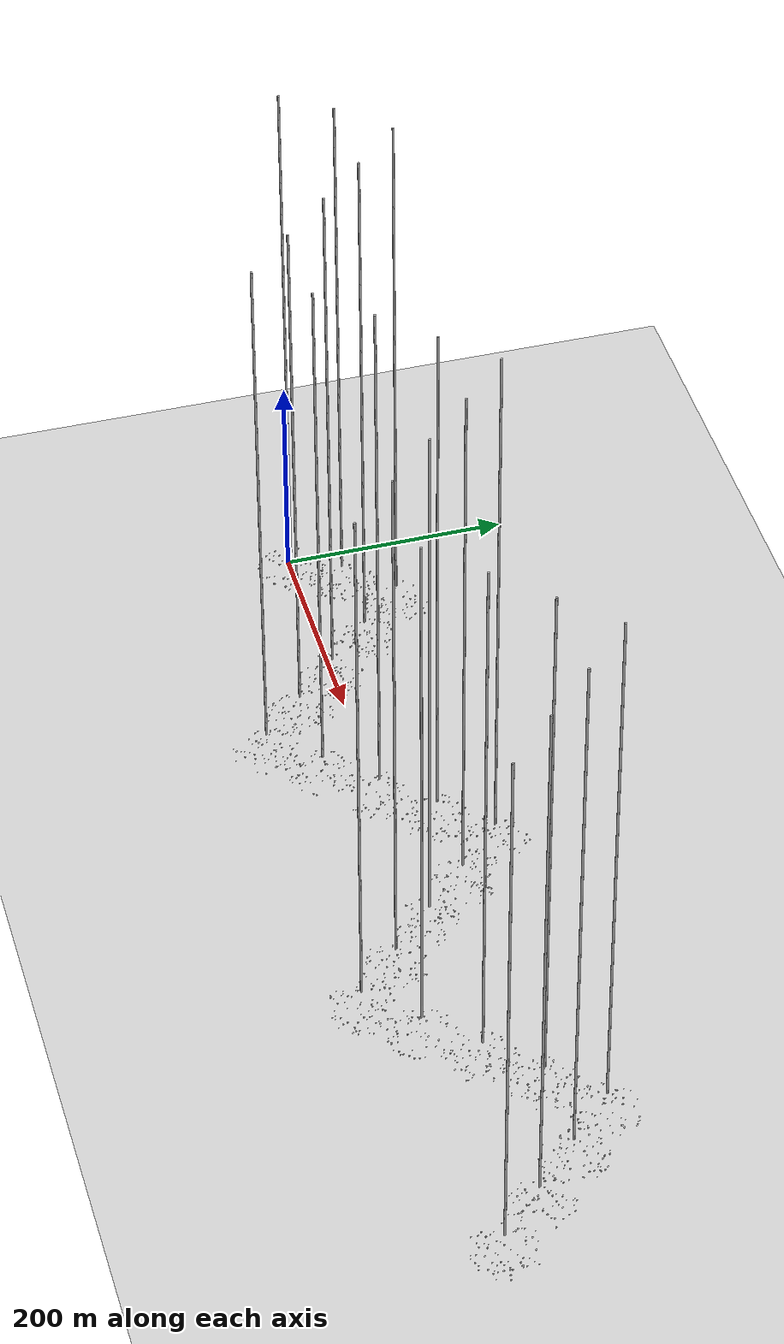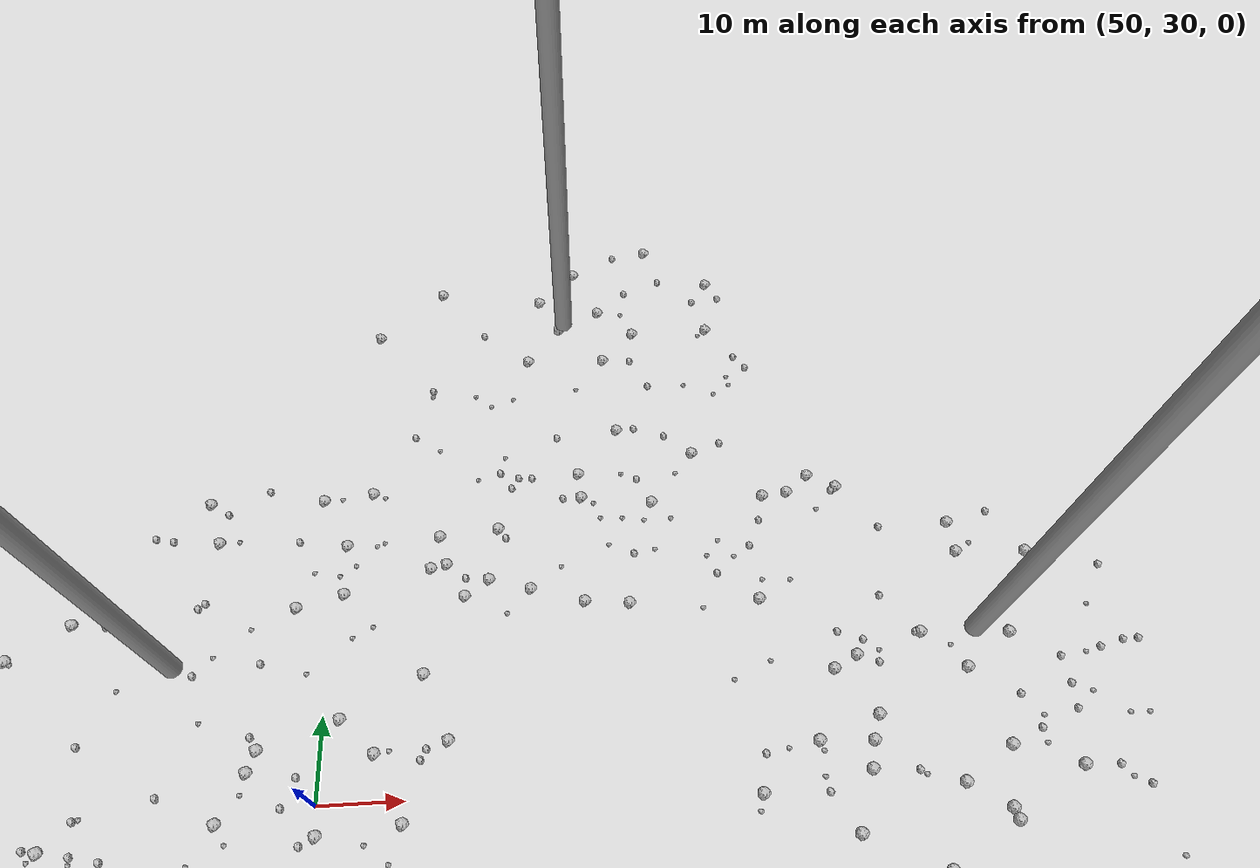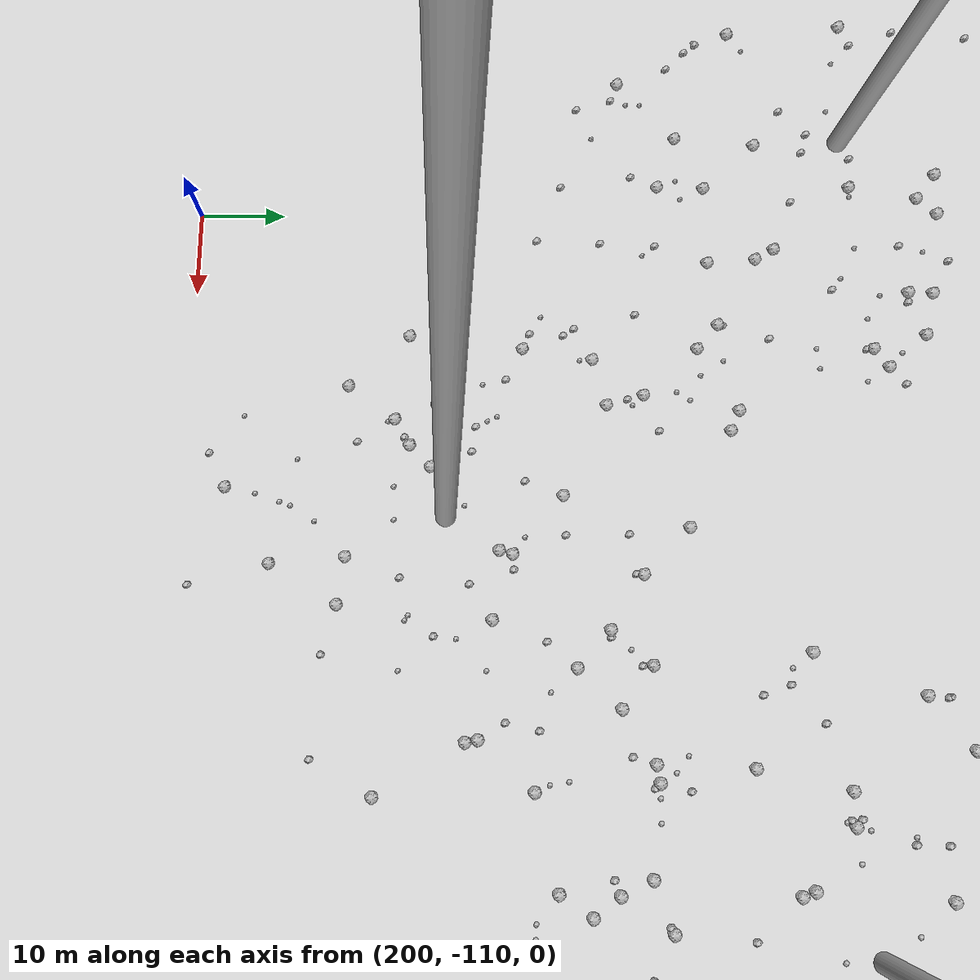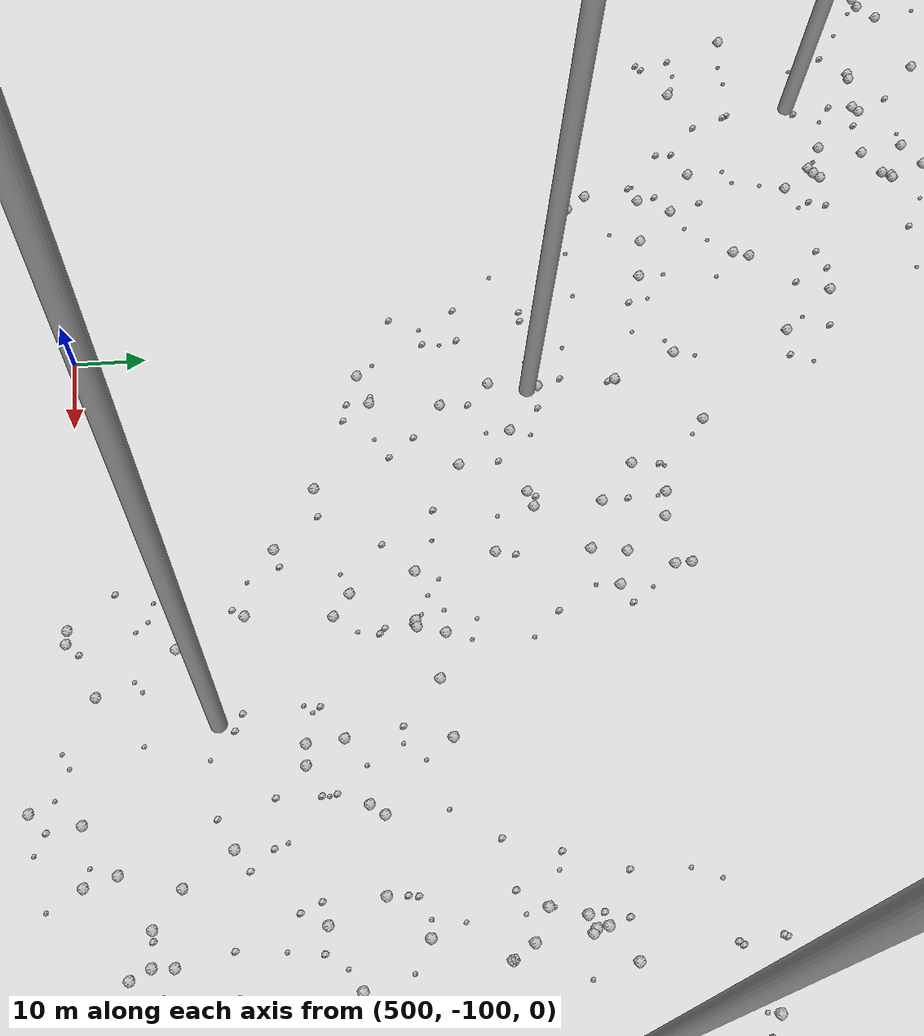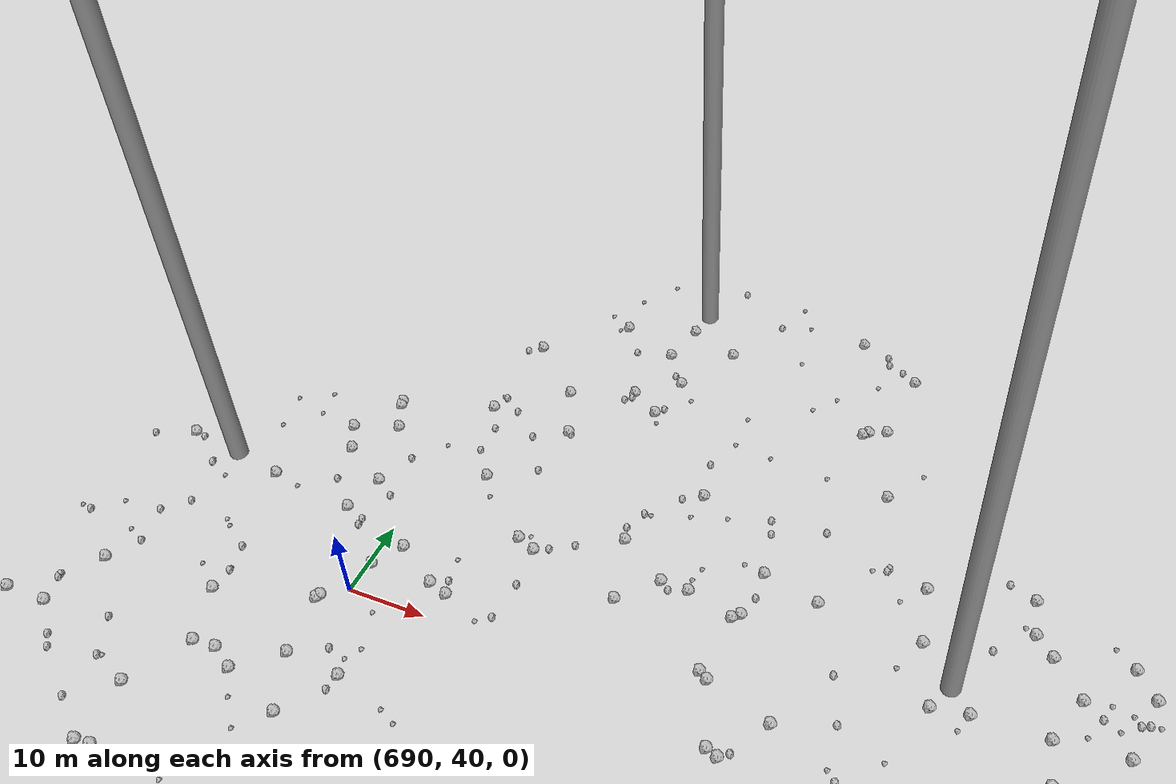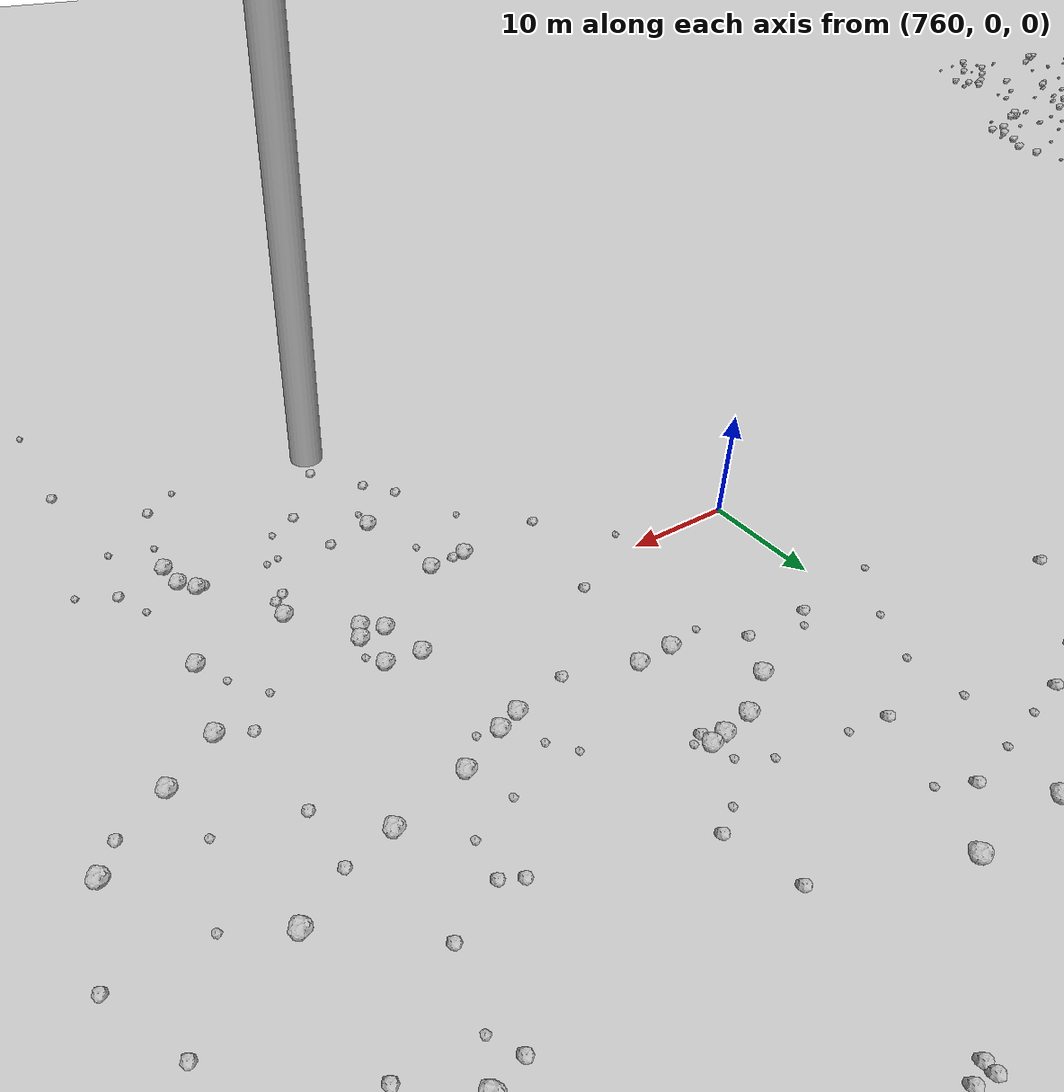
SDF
<sdf version="1.6">
 <world name="default">
  <include><uri>model://custom_ground</uri></include>
  <include><uri>model://sun</uri></include>
  <spherical_coordinates>
   <surface_model>EARTH_WGS84</surface_model>
   <latitude_deg>38.161479</latitude_deg>
   <longitude_deg>-122.454630</longitude_deg>
   <elevation>488.0</elevation>
   <heading_deg>90</heading_deg>
  </spherical_coordinates>
  <model name="rock1_0_0">
   <include><uri>model://rock1</uri><pose>-10.692950199762558 -5.694262957405197 0.5 0 0 0</pose></include>
  </model>
  <model name="rock1_0_1">
   <include><uri>model://rock1</uri><pose>-5.658957325771137 0.3496676300299022 0.5 0 0 0</pose></include>
  </model>
  <model name="rock1_0_2">
   <include><uri>model://rock1</uri><pose>30.878403765775516 -5.665382515572148 0.5 0 0 0</pose></include>
  </model>
  <model name="rock1_0_3">
   <include><uri>model://rock1</uri><pose>26.424663385686443 5.518385392285893 0.5 0 0 0</pose></include>
  </model>
  <model name="rock1_0_4">
   <include><uri>model://rock1</uri><pose>15.792059588464603 2.5856343237582777 0.5 0 0 0</pose></include>
  </model>
  <model name="rock1_0_5">
   <include><uri>model://rock1</uri><pose>-13.246311408103328 -17.461088309241497 0.5 0 0 0</pose></include>
  </model>
  <model name="rock1_0_6">
   <include><uri>model://rock1</uri><pose>32.86758371201801 -11.185259424336287 0.5 0 0 0</pose></include>
  </model>
  <model name="rock1_0_7">
   <include><uri>model://rock1</uri><pose>6.664325097783895 27.88895149416907 0.5 0 0 0</pose></include>
  </model>
  <model name="rock1_0_8">
   <include><uri>model://rock1</uri><pose>16.38198587627363 -24.299359834836338 0.5 0 0 0</pose></include>
  </model>
  <model name="rock1_0_9">
   <include><uri>model://rock1</uri><pose>-5.057398701653746 -13.02554828046047 0.5 0 0 0</pose></include>
  </model>
  <model name="rock1_0_10">
   <include><uri>model://rock1</uri><pose>37.102194280965264 -1.5785365843967547 0.5 0 0 0</pose></include>
  </model>
  <model name="rock1_0_11">
   <include><uri>model://rock1</uri><pose>-11.791469590583024 -10.871575741071794 0.5 0 0 0</pose></include>
  </model>
  <model name="rock1_0_12">
   <include><uri>model://rock1</uri><pose>25.21956386524247 14.537611340151152 0.5 0 0 0</pose></include>
  </model>
  <model name="rock1_0_13">
   <include><uri>model://rock1</uri><pose>6.656771046944733 14.855830301617786 0.5 0 0 0</pose></include>
  </model>
  <model name="rock1_0_14">
   <include><uri>model://rock1</uri><pose>21.70451540708693 -9.872676406908322 0.5 0 0 0</pose></include>
  </model>
  <model name="rock1_0_15">
   <include><uri>model://rock1</uri><pose>-17.426758880507297 -8.006383764174984 0.5 0 0 0</pose></include>
  </model>
  <model name="rock1_0_16">
   <include><uri>model://rock1</uri><pose>22.939439406477796 -6.421791323966318 0.5 0 0 0</pose></include>
  </model>
  <model name="rock1_0_17">
   <include><uri>model://rock1</uri><pose>32.63290824903232 -10.668047906462363 0.5 0 0 0</pose></include>
  </model>
  <model name="rock1_0_18">
   <include><uri>model://rock1</uri><pose>1.4147852863394341 -8.720429549901645 0.5 0 0 0</pose></include>
  </model>
  <model name="rock1_0_19">
   <include><uri>model://rock1</uri><pose>8.562848650976996 18.650020384750334 0.5 0 0 0</pose></include>
  </model>
  <model name="rock1_0_20">
   <include><uri>model://rock1</uri><pose>4.707206123170696 -1.466832553625757 0.5 0 0 0</pose></include>
  </model>
  <model name="rock1_0_21">
   <include><uri>model://rock1</uri><pose>1.4558374670019951 -28.152922369738672 0.5 0 0 0</pose></include>
  </model>
  <model name="rock1_0_22">
   <include><uri>model://rock1</uri><pose>25.827717625207548 -19.901970314157342 0.5 0 0 0</pose></include>
  </model>
  <model name="rock1_0_23">
   <include><uri>model://rock1</uri><pose>20.257392305057877 26.57839644833694 0.5 0 0 0</pose></include>
  </model>
  <model name="rock1_0_24">
   <include><uri>model://rock1</uri><pose>-0.7974680756264689 12.608215530764795 0.5 0 0 0</pose></include>
  </model>
  <model name="rock1_0_25">
   <include><uri>model://rock1</uri><pose>20.782729727890988 16.886980213893416 0.5 0 0 0</pose></include>
  </model>
  <model name="rock1_0_26">
   <include><uri>model://rock1</uri><pose>-16.04725043186187 13.31443039328935 0.5 0 0 0</pose></include>
  </model>
  <model name="rock2_0_0">
   <include><uri>model://rock2</uri><pose>20.638853235960738 8.050960482183392 0.3 0 0 0</pose></include>
  </model>
  <model name="rock2_0_1">
   <include><uri>model://rock2</uri><pose>15.073504178447884 -27.78170011377206 0.3 0 0 0</pose></include>
  </model>
  <model name="rock2_0_2">
   <include><uri>model://rock2</uri><pose>30.986093873417147 16.666447960035732 0.3 0 0 0</pose></include>
  </model>
  <model name="rock2_0_3">
   <include><uri>model://rock2</uri><pose>-4.100927348919681 -26.22483491121859 0.3 0 0 0</pose></include>
  </model>
  <model name="rock2_0_4">
   <include><uri>model://rock2</uri><pose>16.023490512058522 -22.260182657310477 0.3 0 0 0</pose></include>
  </model>
  <model name="rock2_0_5">
   <include><uri>model://rock2</uri><pose>15.5834325050471 27.84795376053181 0.3 0 0 0</pose></include>
  </model>
  <model name="rock2_0_6">
   <include><uri>model://rock2</uri><pose>-17.636892457093587 6.647243902127059 0.3 0 0 0</pose></include>
  </model>
  <model name="rock2_0_7">
   <include><uri>model://rock2</uri><pose>9.944081655393965 -29.04863635310034 0.3 0 0 0</pose></include>
  </model>
  <model name="rock2_0_8">
   <include><uri>model://rock2</uri><pose>17.59411086670591 12.048693455836002 0.3 0 0 0</pose></include>
  </model>
  <model name="rock2_0_9">
   <include><uri>model://rock2</uri><pose>37.168319434460045 -8.225393611736305 0.3 0 0 0</pose></include>
  </model>
  <model name="rock2_0_10">
   <include><uri>model://rock2</uri><pose>10.198484901746173 -27.95145127355593 0.3 0 0 0</pose></include>
  </model>
  <model name="rock2_0_11">
   <include><uri>model://rock2</uri><pose>16.412913486327625 -17.372057367566182 0.3 0 0 0</pose></include>
  </model>
  <model name="rock2_0_12">
   <include><uri>model://rock2</uri><pose>27.932761311864752 13.65342839912691 0.3 0 0 0</pose></include>
  </model>
  <model name="rock2_0_13">
   <include><uri>model://rock2</uri><pose>23.416878188849232 19.67437954395713 0.3 0 0 0</pose></include>
  </model>
  <model name="rock2_0_14">
   <include><uri>model://rock2</uri><pose>19.35921809928802 9.556040739827893 0.3 0 0 0</pose></include>
  </model>
  <model name="rock2_0_15">
   <include><uri>model://rock2</uri><pose>20.448273468871108 -9.874352385390694 0.3 0 0 0</pose></include>
  </model>
  <model name="rock2_0_16">
   <include><uri>model://rock2</uri><pose>0.7457566052805333 -7.321420349210278 0.3 0 0 0</pose></include>
  </model>
  <model name="rock2_0_17">
   <include><uri>model://rock2</uri><pose>23.766410973102836 26.02959720718819 0.3 0 0 0</pose></include>
  </model>
  <model name="rock2_0_18">
   <include><uri>model://rock2</uri><pose>-10.46285420992029 10.382005376687289 0.3 0 0 0</pose></include>
  </model>
  <model name="rock2_0_19">
   <include><uri>model://rock2</uri><pose>7.39799267174126 9.704032991559906 0.3 0 0 0</pose></include>
  </model>
  <model name="rock2_0_20">
   <include><uri>model://rock2</uri><pose>31.25550049120428 -1.842081476967202 0.3 0 0 0</pose></include>
  </model>
  <model name="rock2_0_21">
   <include><uri>model://rock2</uri><pose>37.806231001832785 -0.45472168242985944 0.3 0 0 0</pose></include>
  </model>
  <model name="rock2_0_22">
   <include><uri>model://rock2</uri><pose>-15.167472373862964 11.97789261883544 0.3 0 0 0</pose></include>
  </model>
  <model name="rock2_0_23">
   <include><uri>model://rock2</uri><pose>18.519693289685776 26.921126270212454 0.3 0 0 0</pose></include>
  </model>
  <model name="rock2_0_24">
   <include><uri>model://rock2</uri><pose>20.068812102155555 -8.412518394419624 0.3 0 0 0</pose></include>
  </model>
  <model name="rock2_0_25">
   <include><uri>model://rock2</uri><pose>-7.344855967207209 -15.767132884485884 0.3 0 0 0</pose></include>
  </model>
  <model name="rock2_0_26">
   <include><uri>model://rock2</uri><pose>23.183844976291624 -0.38484348632250587 0.3 0 0 0</pose></include>
  </model>
  <model name="rock3_0_0">
   <include><uri>model://rock3</uri><pose>19.222055252697118 25.674795841790143 0.2 0 0 0</pose></include>
  </model>
  <model name="rock3_0_1">
   <include><uri>model://rock3</uri><pose>-15.014882427459334 9.24007987025125 0.2 0 0 0</pose></include>
  </model>
  <model name="rock3_0_2">
   <include><uri>model://rock3</uri><pose>-7.952345531072835 -21.19664097806477 0.2 0 0 0</pose></include>
  </model>
  <model name="rock3_0_3">
   <include><uri>model://rock3</uri><pose>-2.8994995171614804 -5.071678144864684 0.2 0 0 0</pose></include>
  </model>
  <model name="rock3_0_4">
   <include><uri>model://rock3</uri><pose>10.604485431292549 -23.48592891034832 0.2 0 0 0</pose></include>
  </model>
  <model name="rock3_0_5">
   <include><uri>model://rock3</uri><pose>-8.766420709711959 -15.967316734872183 0.2 0 0 0</pose></include>
  </model>
  <model name="rock3_0_6">
   <include><uri>model://rock3</uri><pose>-15.185120155771596 -0.37030785526484067 0.2 0 0 0</pose></include>
  </model>
  <model name="rock3_0_7">
   <include><uri>model://rock3</uri><pose>25.62207411592209 -17.401895640766927 0.2 0 0 0</pose></include>
  </model>
  <model name="rock3_0_8">
   <include><uri>model://rock3</uri><pose>-3.3091948172721857 20.362371637400344 0.2 0 0 0</pose></include>
  </model>
  <model name="rock3_0_9">
   <include><uri>model://rock3</uri><pose>-11.994588061179101 17.11756365710943 0.2 0 0 0</pose></include>
  </model>
  <model name="rock3_0_10">
   <include><uri>model://rock3</uri><pose>27.406581918263292 5.099112665567951 0.2 0 0 0</pose></include>
  </model>
  <model name="rock3_0_11">
   <include><uri>model://rock3</uri><pose>19.97946597591843 -9.858458534809689 0.2 0 0 0</pose></include>
  </model>
  <model name="rock3_0_12">
   <include><uri>model://rock3</uri><pose>21.069647156048113 -17.72559386210859 0.2 0 0 0</pose></include>
  </model>
  <model name="rock3_0_13">
   <include><uri>model://rock3</uri><pose>-19.212449021335274 5.852994857055926 0.2 0 0 0</pose></include>
  </model>
  <model name="rock3_0_14">
   <include><uri>model://rock3</uri><pose>-16.667115045664037 -13.56674312973895 0.2 0 0 0</pose></include>
  </model>
  <model name="rock3_0_15">
   <include><uri>model://rock3</uri><pose>8.357166798603718 23.049005407127247 0.2 0 0 0</pose></include>
  </model>
  <model name="rock3_0_16">
   <include><uri>model://rock3</uri><pose>4.371278981833264 -24.68523478718025 0.2 0 0 0</pose></include>
  </model>
  <model name="rock3_0_17">
   <include><uri>model://rock3</uri><pose>22.705099520256212 23.442333351975137 0.2 0 0 0</pose></include>
  </model>
  <model name="rock3_0_18">
   <include><uri>model://rock3</uri><pose>14.8534496613145 8.348264315017893 0.2 0 0 0</pose></include>
  </model>
  <model name="rock3_0_19">
   <include><uri>model://rock3</uri><pose>33.829441652371024 9.761567215216267 0.2 0 0 0</pose></include>
  </model>
  <model name="rock3_0_20">
   <include><uri>model://rock3</uri><pose>-2.189684655102475 14.695674258417675 0.2 0 0 0</pose></include>
  </model>
  <model name="rock3_0_21">
   <include><uri>model://rock3</uri><pose>-17.16549660094154 -1.1410408634662907 0.2 0 0 0</pose></include>
  </model>
  <model name="rock3_0_22">
   <include><uri>model://rock3</uri><pose>37.5951780397473 -9.03277485709723 0.2 0 0 0</pose></include>
  </model>
  <model name="rock3_0_23">
   <include><uri>model://rock3</uri><pose>3.65580677294858 -13.352891766849627 0.2 0 0 0</pose></include>
  </model>
  <model name="rock3_0_24">
   <include><uri>model://rock3</uri><pose>26.129902365143202 -19.061383828581636 0.2 0 0 0</pose></include>
  </model>
  <model name="rock3_0_25">
   <include><uri>model://rock3</uri><pose>29.07927544896137 13.231647328561884 0.2 0 0 0</pose></include>
  </model>
  <model name="rock3_0_26">
   <include><uri>model://rock3</uri><pose>12.983624681101894 0.2992034824084442 0.2 0 0 0</pose></include>
  </model>
  <model name="rock1_1_0">
   <include><uri>model://rock1</uri><pose>50.336917673992296 26.725701608046492 0.5 0 0 0</pose></include>
  </model>
  <model name="rock1_1_1">
   <include><uri>model://rock1</uri><pose>48.003046802260876 67.89654305515755 0.5 0 0 0</pose></include>
  </model>
  <model name="rock1_1_2">
   <include><uri>model://rock1</uri><pose>50.28511807754055 18.99560757326867 0.5 0 0 0</pose></include>
  </model>
  <model name="rock1_1_3">
   <include><uri>model://rock1</uri><pose>23.064092358246643 52.32862570732287 0.5 0 0 0</pose></include>
  </model>
  <model name="rock1_1_4">
   <include><uri>model://rock1</uri><pose>44.989786732094906 19.96264985624166 0.5 0 0 0</pose></include>
  </model>
  <model name="rock1_1_5">
   <include><uri>model://rock1</uri><pose>62.040223857999436 57.727926457722035 0.5 0 0 0</pose></include>
  </model>
  <model name="rock1_1_6">
   <include><uri>model://rock1</uri><pose>12.148962692253098 29.177082559528447 0.5 0 0 0</pose></include>
  </model>
  <model name="rock1_1_7">
   <include><uri>model://rock1</uri><pose>11.672857003041875 48.40384391766422 0.5 0 0 0</pose></include>
  </model>
  <model name="rock1_1_8">
   <include><uri>model://rock1</uri><pose>52.05345519589537 39.43915182600955 0.5 0 0 0</pose></include>
  </model>
  <model name="rock1_1_9">
   <include><uri>model://rock1</uri><pose>61.55927334547866 44.2790060972028 0.5 0 0 0</pose></include>
  </model>
  <model name="rock1_1_10">
   <include><uri>model://rock1</uri><pose>42.82394802616398 36.372364841334175 0.5 0 0 0</pose></include>
  </model>
  <model name="rock1_1_11">
   <include><uri>model://rock1</uri><pose>39.15897329520905 28.5408850384179 0.5 0 0 0</pose></include>
  </model>
  <model name="rock1_1_12">
   <include><uri>model://rock1</uri><pose>33.38646337385938 68.13433095444299 0.5 0 0 0</pose></include>
  </model>
  <model name="rock1_1_13">
   <include><uri>model://rock1</uri><pose>51.410968499162955 61.36428902253469 0.5 0 0 0</pose></include>
  </model>
  <model name="rock1_1_14">
   <include><uri>model://rock1</uri><pose>35.2165229157232 62.55072227776817 0.5 0 0 0</pose></include>
  </model>
  <model name="rock1_1_15">
   <include><uri>model://rock1</uri><pose>54.79710466979717 20.845037701503273 0.5 0 0 0</pose></include>
  </model>
  <model name="rock1_1_16">
   <include><uri>model://rock1</uri><pose>64.65422707811373 36.37002205464141 0.5 0 0 0</pose></include>
  </model>
  <model name="rock1_1_17">
   <include><uri>model://rock1</uri><pose>36.10662198030012 15.026059530885188 0.5 0 0 0</pose></include>
  </model>
  <model name="rock1_1_18">
   <include><uri>model://rock1</uri><pose>14.12484777152406 24.855160433507056 0.5 0 0 0</pose></include>
  </model>
  <model name="rock1_1_19">
   <include><uri>model://rock1</uri><pose>42.544427486560885 20.081800689022508 0.5 0 0 0</pose></include>
  </model>
  <model name="rock1_1_20">
   <include><uri>model://rock1</uri><pose>53.347990317207994 13.93162394744677 0.5 0 0 0</pose></include>
  </model>
  <model name="rock1_1_21">
   <include><uri>model://rock1</uri><pose>56.245013391387594 35.30820008186524 0.5 0 0 0</pose></include>
  </model>
  <model name="rock1_1_22">
   <include><uri>model://rock1</uri><pose>51.452047693147684 54.85010913387746 0.5 0 0 0</pose></include>
  </model>
  <model name="rock1_1_23">
   <include><uri>model://rock1</uri><pose>41.94089037276743 33.92410247833006 0.5 0 0 0</pose></include>
  </model>
  <model name="rock1_1_24">
   <include><uri>model://rock1</uri><pose>45.71330470921928 53.35570209021011 0.5 0 0 0</pose></include>
  </model>
  <model name="rock1_1_25">
   <include><uri>model://rock1</uri><pose>59.80442615687612 27.51024399763383 0.5 0 0 0</pose></include>
  </model>
  <model name="rock1_1_26">
   <include><uri>model://rock1</uri><pose>18.73917836454884 52.5672070793901 0.5 0 0 0</pose></include>
  </model>
  <model name="rock2_1_0">
   <include><uri>model://rock2</uri><pose>53.79578705049721 15.734123504952727 0.3 0 0 0</pose></include>
  </model>
  <model name="rock2_1_1">
   <include><uri>model://rock2</uri><pose>42.06478938740249 46.5824528844492 0.3 0 0 0</pose></include>
  </model>
  <model name="rock2_1_2">
   <include><uri>model://rock2</uri><pose>30.077535388810258 22.932567407129874 0.3 0 0 0</pose></include>
  </model>
  <model name="rock2_1_3">
   <include><uri>model://rock2</uri><pose>37.340882810355566 18.26959623783905 0.3 0 0 0</pose></include>
  </model>
  <model name="rock2_1_4">
   <include><uri>model://rock2</uri><pose>53.288792439235 22.012405721624773 0.3 0 0 0</pose></include>
  </model>
  <model name="rock2_1_5">
   <include><uri>model://rock2</uri><pose>25.62053740031444 14.36052538856795 0.3 0 0 0</pose></include>
  </model>
  <model name="rock2_1_6">
   <include><uri>model://rock2</uri><pose>23.325947870258215 29.713811212609794 0.3 0 0 0</pose></include>
  </model>
  <model name="rock2_1_7">
   <include><uri>model://rock2</uri><pose>46.13929971101821 29.9121633749837 0.3 0 0 0</pose></include>
  </model>
  <model name="rock2_1_8">
   <include><uri>model://rock2</uri><pose>52.31370695691042 17.690079323504843 0.3 0 0 0</pose></include>
  </model>
  <model name="rock2_1_9">
   <include><uri>model://rock2</uri><pose>48.538751997732035 25.840229174482126 0.3 0 0 0</pose></include>
  </model>
  <model name="rock2_1_10">
   <include><uri>model://rock2</uri><pose>36.94869702582442 12.214216226904817 0.3 0 0 0</pose></include>
  </model>
  <model name="rock2_1_11">
   <include><uri>model://rock2</uri><pose>45.2620040061239 62.26733218686649 0.3 0 0 0</pose></include>
  </model>
  <model name="rock2_1_12">
   <include><uri>model://rock2</uri><pose>33.637223857100196 53.93160972814008 0.3 0 0 0</pose></include>
  </model>
  <model name="rock2_1_13">
   <include><uri>model://rock2</uri><pose>26.983422683837713 63.6292414222371 0.3 0 0 0</pose></include>
  </model>
  <model name="rock2_1_14">
   <include><uri>model://rock2</uri><pose>61.50253214458987 34.37627320699663 0.3 0 0 0</pose></include>
  </model>
  <model name="rock2_1_15">
   <include><uri>model://rock2</uri><pose>40.789984519007426 69.67235777635102 0.3 0 0 0</pose></include>
  </model>
  <model name="rock2_1_16">
   <include><uri>model://rock2</uri><pose>32.06816868623076 31.706090172629885 0.3 0 0 0</pose></include>
  </model>
  <model name="rock2_1_17">
   <include><uri>model://rock2</uri><pose>35.18443872693422 11.12313550252058 0.3 0 0 0</pose></include>
  </model>
  <model name="rock2_1_18">
   <include><uri>model://rock2</uri><pose>22.099663794469535 37.84457362873674 0.3 0 0 0</pose></include>
  </model>
  <model name="rock2_1_19">
   <include><uri>model://rock2</uri><pose>29.267185424709655 63.14126118972747 0.3 0 0 0</pose></include>
  </model>
  <model name="rock2_1_20">
   <include><uri>model://rock2</uri><pose>62.1447488210864 35.580903316451895 0.3 0 0 0</pose></include>
  </model>
  <model name="rock2_1_21">
   <include><uri>model://rock2</uri><pose>34.461532418671716 54.54491577712246 0.3 0 0 0</pose></include>
  </model>
  <model name="rock2_1_22">
   <include><uri>model://rock2</uri><pose>34.14980781159261 45.49954077180377 0.3 0 0 0</pose></include>
  </model>
  <model name="rock2_1_23">
   <include><uri>model://rock2</uri><pose>47.554332179453525 33.20375443885449 0.3 0 0 0</pose></include>
  </model>
  <model name="rock2_1_24">
   <include><uri>model://rock2</uri><pose>27.121167591606433 25.306678717460247 0.3 0 0 0</pose></include>
  </model>
  <model name="rock2_1_25">
   <include><uri>model://rock2</uri><pose>35.776828821084294 66.60228213354301 0.3 0 0 0</pose></include>
  </model>
  <model name="rock2_1_26">
   <include><uri>model://rock2</uri><pose>41.84995180607031 37.926529958167535 0.3 0 0 0</pose></include>
  </model>
  <model name="rock3_1_0">
   <include><uri>model://rock3</uri><pose>26.084954279811644 50.516149618313 0.2 0 0 0</pose></include>
  </model>
  <model name="rock3_1_1">
   <include><uri>model://rock3</uri><pose>35.652144868484896 39.85977213117428 0.2 0 0 0</pose></include>
  </model>
  <model name="rock3_1_2">
   <include><uri>model://rock3</uri><pose>25.462014660763607 44.117300482027495 0.2 0 0 0</pose></include>
  </model>
  <model name="rock3_1_3">
   <include><uri>model://rock3</uri><pose>55.19292960950425 50.47455224533451 0.2 0 0 0</pose></include>
  </model>
  <model name="rock3_1_4">
   <include><uri>model://rock3</uri><pose>37.599031685525944 62.67149295516936 0.2 0 0 0</pose></include>
  </model>
  <model name="rock3_1_5">
   <include><uri>model://rock3</uri><pose>23.7903209589072 25.188122387089017 0.2 0 0 0</pose></include>
  </model>
  <model name="rock3_1_6">
   <include><uri>model://rock3</uri><pose>47.61836984229776 45.04417248688891 0.2 0 0 0</pose></include>
  </model>
  <model name="rock3_1_7">
   <include><uri>model://rock3</uri><pose>50.24198501608294 68.04392509130787 0.2 0 0 0</pose></include>
  </model>
  <model name="rock3_1_8">
   <include><uri>model://rock3</uri><pose>55.61629666235851 25.56269428504107 0.2 0 0 0</pose></include>
  </model>
  <model name="rock3_1_9">
   <include><uri>model://rock3</uri><pose>40.38581220450599 26.342542337835514 0.2 0 0 0</pose></include>
  </model>
  <model name="rock3_1_10">
   <include><uri>model://rock3</uri><pose>12.702275220130081 31.21063515220438 0.2 0 0 0</pose></include>
  </model>
  <model name="rock3_1_11">
   <include><uri>model://rock3</uri><pose>52.76496176348785 49.22714481721 0.2 0 0 0</pose></include>
  </model>
  <model name="rock3_1_12">
   <include><uri>model://rock3</uri><pose>52.61660613320436 58.624422188697466 0.2 0 0 0</pose></include>
  </model>
  <model name="rock3_1_13">
   <include><uri>model://rock3</uri><pose>47.489838571845596 57.94062029426037 0.2 0 0 0</pose></include>
  </model>
  <model name="rock3_1_14">
   <include><uri>model://rock3</uri><pose>50.67323158766834 57.325007379113245 0.2 0 0 0</pose></include>
  </model>
  <model name="rock3_1_15">
   <include><uri>model://rock3</uri><pose>57.866643976807694 35.553448074346925 0.2 0 0 0</pose></include>
  </model>
  <model name="rock3_1_16">
   <include><uri>model://rock3</uri><pose>23.96546751609616 29.870763267258774 0.2 0 0 0</pose></include>
  </model>
  <model name="rock3_1_17">
   <include><uri>model://rock3</uri><pose>30.354307226099397 16.0278633762586 0.2 0 0 0</pose></include>
  </model>
  <model name="rock3_1_18">
   <include><uri>model://rock3</uri><pose>40.43869422920387 50.91574368365344 0.2 0 0 0</pose></include>
  </model>
  <model name="rock3_1_19">
   <include><uri>model://rock3</uri><pose>24.001566739122467 52.549690567914574 0.2 0 0 0</pose></include>
  </model>
  <model name="rock3_1_20">
   <include><uri>model://rock3</uri><pose>12.145818348738045 47.98787167223382 0.2 0 0 0</pose></include>
  </model>
  <model name="rock3_1_21">
   <include><uri>model://rock3</uri><pose>56.04378109343687 61.552190049830244 0.2 0 0 0</pose></include>
  </model>
  <model name="rock3_1_22">
   <include><uri>model://rock3</uri><pose>55.098711584795254 61.186889031815056 0.2 0 0 0</pose></include>
  </model>
  <model name="rock3_1_23">
   <include><uri>model://rock3</uri><pose>41.44279359626219 31.549340733467645 0.2 0 0 0</pose></include>
  </model>
  <model name="rock3_1_24">
   <include><uri>model://rock3</uri><pose>36.52345317490659 24.340535932259684 0.2 0 0 0</pose></include>
  </model>
  <model name="rock3_1_25">
   <include><uri>model://rock3</uri><pose>36.264809464489716 47.63520011617627 0.2 0 0 0</pose></include>
  </model>
  <model name="rock3_1_26">
   <include><uri>model://rock3</uri><pose>58.427568339369266 23.43683261013083 0.2 0 0 0</pose></include>
  </model>
  <model name="rock1_2_0">
   <include><uri>model://rock1</uri><pose>53.87122770340221 93.48351675986493 0.5 0 0 0</pose></include>
  </model>
  <model name="rock1_2_1">
   <include><uri>model://rock1</uri><pose>81.02086850833527 70.12709884495517 0.5 0 0 0</pose></include>
  </model>
  <model name="rock1_2_2">
   <include><uri>model://rock1</uri><pose>66.32826962896988 53.83977327368214 0.5 0 0 0</pose></include>
  </model>
  <model name="rock1_2_3">
   <include><uri>model://rock1</uri><pose>63.98167721016975 58.18812075297779 0.5 0 0 0</pose></include>
  </model>
  <model name="rock1_2_4">
   <include><uri>model://rock1</uri><pose>76.61392531997114 98.710030688073 0.5 0 0 0</pose></include>
  </model>
  <model name="rock1_2_5">
   <include><uri>model://rock1</uri><pose>70.48804458040513 62.735086398606654 0.5 0 0 0</pose></include>
  </model>
  <model name="rock1_2_6">
   <include><uri>model://rock1</uri><pose>84.90837185310437 96.4706068901187 0.5 0 0 0</pose></include>
  </model>
  <model name="rock1_2_7">
   <include><uri>model://rock1</uri><pose>79.23749800558082 93.67378627488276 0.5 0 0 0</pose></include>
  </model>
  <model name="rock1_2_8">
   <include><uri>model://rock1</uri><pose>81.08307485466054 52.43384317531644 0.5 0 0 0</pose></include>
  </model>
  <model name="rock1_2_9">
   <include><uri>model://rock1</uri><pose>104.78154886428729 65.70413328824179 0.5 0 0 0</pose></include>
  </model>
  <model name="rock1_2_10">
   <include><uri>model://rock1</uri><pose>81.67564824158852 103.60904369518698 0.5 0 0 0</pose></include>
  </model>
  <model name="rock1_2_11">
   <include><uri>model://rock1</uri><pose>96.22265373386139 72.51476637509371 0.5 0 0 0</pose></include>
  </model>
  <model name="rock1_2_12">
   <include><uri>model://rock1</uri><pose>81.24521467833151 66.69596659120988 0.5 0 0 0</pose></include>
  </model>
  <model name="rock1_2_13">
   <include><uri>model://rock1</uri><pose>74.81626167201382 88.39190987600162 0.5 0 0 0</pose></include>
  </model>
  <model name="rock1_2_14">
   <include><uri>model://rock1</uri><pose>90.33513504102567 65.5398630635088 0.5 0 0 0</pose></include>
  </model>
  <model name="rock1_2_15">
   <include><uri>model://rock1</uri><pose>54.293490725313184 68.59351970536072 0.5 0 0 0</pose></include>
  </model>
  <model name="rock1_2_16">
   <include><uri>model://rock1</uri><pose>62.53368445951179 100.83519968915259 0.5 0 0 0</pose></include>
  </model>
  <model name="rock1_2_17">
   <include><uri>model://rock1</uri><pose>101.03597082002014 100.84690752693385 0.5 0 0 0</pose></include>
  </model>
  <model name="rock1_2_18">
   <include><uri>model://rock1</uri><pose>100.17832041923168 92.6301237417779 0.5 0 0 0</pose></include>
  </model>
  <model name="rock1_2_19">
   <include><uri>model://rock1</uri><pose>63.07617910506876 62.00080918423835 0.5 0 0 0</pose></include>
  </model>
  <model name="rock1_2_20">
   <include><uri>model://rock1</uri><pose>92.4166452708762 107.24916010564164 0.5 0 0 0</pose></include>
  </model>
  <model name="rock1_2_21">
   <include><uri>model://rock1</uri><pose>86.58727036414798 51.91184806763537 0.5 0 0 0</pose></include>
  </model>
  <model name="rock1_2_22">
   <include><uri>model://rock1</uri><pose>85.22106980566278 88.08483403135742 0.5 0 0 0</pose></include>
  </model>
  <model name="rock1_2_23">
   <include><uri>model://rock1</uri><pose>86.44294172754289 76.5767957974476 0.5 0 0 0</pose></include>
  </model>
  <model name="rock1_2_24">
   <include><uri>model://rock1</uri><pose>89.62806885695781 92.45476218171447 0.5 0 0 0</pose></include>
  </model>
  <model name="rock1_2_25">
   <include><uri>model://rock1</uri><pose>69.30975632051197 55.90884759734501 0.5 0 0 0</pose></include>
  </model>
  <model name="rock1_2_26">
   <include><uri>model://rock1</uri><pose>74.46490571719869 54.405013572763295 0.5 0 0 0</pose></include>
  </model>
  <model name="rock2_2_0">
   <include><uri>model://rock2</uri><pose>103.85833417766673 62.330900242212046 0.3 0 0 0</pose></include>
  </model>
  <model name="rock2_2_1">
   <include><uri>model://rock2</uri><pose>103.62290992590619 87.89025082416074 0.3 0 0 0</pose></include>
  </model>
  <model name="rock2_2_2">
   <include><uri>model://rock2</uri><pose>92.73263597876158 75.47430403771392 0.3 0 0 0</pose></include>
  </model>
  <model name="rock2_2_3">
   <include><uri>model://rock2</uri><pose>87.56820124139578 58.54573699108775 0.3 0 0 0</pose></include>
  </model>
  <model name="rock2_2_4">
   <include><uri>model://rock2</uri><pose>94.01214301321332 101.79701850828698 0.3 0 0 0</pose></include>
  </model>
  <model name="rock2_2_5">
   <include><uri>model://rock2</uri><pose>98.73775203045625 97.853689453388 0.3 0 0 0</pose></include>
  </model>
  <model name="rock2_2_6">
   <include><uri>model://rock2</uri><pose>61.54369080151355 84.27052032836075 0.3 0 0 0</pose></include>
  </model>
  <model name="rock2_2_7">
   <include><uri>model://rock2</uri><pose>66.34994452409003 56.27847911663522 0.3 0 0 0</pose></include>
  </model>
  <model name="rock2_2_8">
   <include><uri>model://rock2</uri><pose>73.14104300588 70.05507831312745 0.3 0 0 0</pose></include>
  </model>
  <model name="rock2_2_9">
   <include><uri>model://rock2</uri><pose>88.94679934057747 87.92446340020399 0.3 0 0 0</pose></include>
  </model>
  <model name="rock2_2_10">
   <include><uri>model://rock2</uri><pose>87.63451223175818 106.67105343687102 0.3 0 0 0</pose></include>
  </model>
  <model name="rock2_2_11">
   <include><uri>model://rock2</uri><pose>102.51482994814226 98.30339203120579 0.3 0 0 0</pose></include>
  </model>
  <model name="rock2_2_12">
   <include><uri>model://rock2</uri><pose>72.20976776473863 68.57332300791825 0.3 0 0 0</pose></include>
  </model>
  <model name="rock2_2_13">
   <include><uri>model://rock2</uri><pose>88.61202954761609 69.10793674596138 0.3 0 0 0</pose></include>
  </model>
  <model name="rock2_2_14">
   <include><uri>model://rock2</uri><pose>68.5929044094564 93.2885259450247 0.3 0 0 0</pose></include>
  </model>
  <model name="rock2_2_15">
   <include><uri>model://rock2</uri><pose>88.74827130245359 76.79130623332983 0.3 0 0 0</pose></include>
  </model>
  <model name="rock2_2_16">
   <include><uri>model://rock2</uri><pose>78.37524110828123 75.87894576398291 0.3 0 0 0</pose></include>
  </model>
  <model name="rock2_2_17">
   <include><uri>model://rock2</uri><pose>100.06938413299493 73.96951591970571 0.3 0 0 0</pose></include>
  </model>
  <model name="rock2_2_18">
   <include><uri>model://rock2</uri><pose>105.03043433256111 86.03023531170074 0.3 0 0 0</pose></include>
  </model>
  <model name="rock2_2_19">
   <include><uri>model://rock2</uri><pose>80.3790527781985 97.34009074498287 0.3 0 0 0</pose></include>
  </model>
  <model name="rock2_2_20">
   <include><uri>model://rock2</uri><pose>70.76191315885822 70.8722074161754 0.3 0 0 0</pose></include>
  </model>
  <model name="rock2_2_21">
   <include><uri>model://rock2</uri><pose>91.16780493614087 83.5871975132678 0.3 0 0 0</pose></include>
  </model>
  <model name="rock2_2_22">
   <include><uri>model://rock2</uri><pose>71.39660392877744 61.4942047116635 0.3 0 0 0</pose></include>
  </model>
  <model name="rock2_2_23">
   <include><uri>model://rock2</uri><pose>74.87959974156627 69.91693528173788 0.3 0 0 0</pose></include>
  </model>
  <model name="rock2_2_24">
   <include><uri>model://rock2</uri><pose>59.382123637968604 76.90681335441482 0.3 0 0 0</pose></include>
  </model>
  <model name="rock2_2_25">
   <include><uri>model://rock2</uri><pose>88.91372010403316 99.91018547038664 0.3 0 0 0</pose></include>
  </model>
  <model name="rock2_2_26">
   <include><uri>model://rock2</uri><pose>78.85449052481692 66.73868994550841 0.3 0 0 0</pose></include>
  </model>
  <model name="rock3_2_0">
   <include><uri>model://rock3</uri><pose>86.60013484087867 70.00083848498411 0.2 0 0 0</pose></include>
  </model>
  <model name="rock3_2_1">
   <include><uri>model://rock3</uri><pose>100.18454210481556 81.83924442728026 0.2 0 0 0</pose></include>
  </model>
  <model name="rock3_2_2">
   <include><uri>model://rock3</uri><pose>102.44776644266305 83.26241289644392 0.2 0 0 0</pose></include>
  </model>
  <model name="rock3_2_3">
   <include><uri>model://rock3</uri><pose>84.44974317552797 59.89627299511948 0.2 0 0 0</pose></include>
  </model>
  <model name="rock3_2_4">
   <include><uri>model://rock3</uri><pose>82.77233462714423 65.8583502075125 0.2 0 0 0</pose></include>
  </model>
  <model name="rock3_2_5">
   <include><uri>model://rock3</uri><pose>69.54147954519652 81.34797620886633 0.2 0 0 0</pose></include>
  </model>
  <model name="rock3_2_6">
   <include><uri>model://rock3</uri><pose>67.41875087370295 83.07707958414412 0.2 0 0 0</pose></include>
  </model>
  <model name="rock3_2_7">
   <include><uri>model://rock3</uri><pose>90.21942150021448 58.978265814001816 0.2 0 0 0</pose></include>
  </model>
  <model name="rock3_2_8">
   <include><uri>model://rock3</uri><pose>55.751985122093316 67.99380671809953 0.2 0 0 0</pose></include>
  </model>
  <model name="rock3_2_9">
   <include><uri>model://rock3</uri><pose>81.2244280910027 83.52454565404713 0.2 0 0 0</pose></include>
  </model>
  <model name="rock3_2_10">
   <include><uri>model://rock3</uri><pose>71.47013003897925 51.38609263441222 0.2 0 0 0</pose></include>
  </model>
  <model name="rock3_2_11">
   <include><uri>model://rock3</uri><pose>92.60350145051282 63.18962255078948 0.2 0 0 0</pose></include>
  </model>
  <model name="rock3_2_12">
   <include><uri>model://rock3</uri><pose>96.6922068094802 57.71647181460645 0.2 0 0 0</pose></include>
  </model>
  <model name="rock3_2_13">
   <include><uri>model://rock3</uri><pose>102.26236507207027 84.57982907562452 0.2 0 0 0</pose></include>
  </model>
  <model name="rock3_2_14">
   <include><uri>model://rock3</uri><pose>98.99303829535694 91.85014458405556 0.2 0 0 0</pose></include>
  </model>
  <model name="rock3_2_15">
   <include><uri>model://rock3</uri><pose>89.15110390852804 63.10859326189426 0.2 0 0 0</pose></include>
  </model>
  <model name="rock3_2_16">
   <include><uri>model://rock3</uri><pose>78.30893107814659 57.18800182607068 0.2 0 0 0</pose></include>
  </model>
  <model name="rock3_2_17">
   <include><uri>model://rock3</uri><pose>86.38230718962514 63.540531390303926 0.2 0 0 0</pose></include>
  </model>
  <model name="rock3_2_18">
   <include><uri>model://rock3</uri><pose>71.37755922864835 73.14275064707365 0.2 0 0 0</pose></include>
  </model>
  <model name="rock3_2_19">
   <include><uri>model://rock3</uri><pose>93.76702552167274 69.71112893055533 0.2 0 0 0</pose></include>
  </model>
  <model name="rock3_2_20">
   <include><uri>model://rock3</uri><pose>62.71314261505364 74.70873128622432 0.2 0 0 0</pose></include>
  </model>
  <model name="rock3_2_21">
   <include><uri>model://rock3</uri><pose>88.16127213774142 96.06889442551511 0.2 0 0 0</pose></include>
  </model>
  <model name="rock3_2_22">
   <include><uri>model://rock3</uri><pose>96.17559075479464 83.48709020406652 0.2 0 0 0</pose></include>
  </model>
  <model name="rock3_2_23">
   <include><uri>model://rock3</uri><pose>61.48327989529812 83.33750245233615 0.2 0 0 0</pose></include>
  </model>
  <model name="rock3_2_24">
   <include><uri>model://rock3</uri><pose>67.86163911755587 69.98736041319106 0.2 0 0 0</pose></include>
  </model>
  <model name="rock3_2_25">
   <include><uri>model://rock3</uri><pose>72.52464481391846 82.321620232643 0.2 0 0 0</pose></include>
  </model>
  <model name="rock3_2_26">
   <include><uri>model://rock3</uri><pose>83.58049555467244 63.68474672672709 0.2 0 0 0</pose></include>
  </model>
  <model name="rock1_3_0">
   <include><uri>model://rock1</uri><pose>110.30334106782013 42.39917640247427 0.5 0 0 0</pose></include>
  </model>
  <model name="rock1_3_1">
   <include><uri>model://rock1</uri><pose>132.19321386661755 45.83474531519563 0.5 0 0 0</pose></include>
  </model>
  <model name="rock1_3_2">
   <include><uri>model://rock1</uri><pose>107.19137468109204 34.14144340213795 0.5 0 0 0</pose></include>
  </model>
  <model name="rock1_3_3">
   <include><uri>model://rock1</uri><pose>102.49257873033226 16.42367991008892 0.5 0 0 0</pose></include>
  </model>
  <model name="rock1_3_4">
   <include><uri>model://rock1</uri><pose>127.49508213151805 25.7526744136373 0.5 0 0 0</pose></include>
  </model>
  <model name="rock1_3_5">
   <include><uri>model://rock1</uri><pose>121.4646303356659 46.38700032619276 0.5 0 0 0</pose></include>
  </model>
  <model name="rock1_3_6">
   <include><uri>model://rock1</uri><pose>136.88092290614927 56.26030304959829 0.5 0 0 0</pose></include>
  </model>
  <model name="rock1_3_7">
   <include><uri>model://rock1</uri><pose>113.48150510305678 33.87074808859915 0.5 0 0 0</pose></include>
  </model>
  <model name="rock1_3_8">
   <include><uri>model://rock1</uri><pose>102.56930710303924 51.61136522209818 0.5 0 0 0</pose></include>
  </model>
  <model name="rock1_3_9">
   <include><uri>model://rock1</uri><pose>126.18865498047376 41.80199014781651 0.5 0 0 0</pose></include>
  </model>
  <model name="rock1_3_10">
   <include><uri>model://rock1</uri><pose>120.01597972295264 12.351933157509524 0.5 0 0 0</pose></include>
  </model>
  <model name="rock1_3_11">
   <include><uri>model://rock1</uri><pose>107.9920559821515 66.05627446292323 0.5 0 0 0</pose></include>
  </model>
  <model name="rock1_3_12">
   <include><uri>model://rock1</uri><pose>114.61103916589127 36.772259571010856 0.5 0 0 0</pose></include>
  </model>
  <model name="rock1_3_13">
   <include><uri>model://rock1</uri><pose>127.81502137389563 24.424502812184766 0.5 0 0 0</pose></include>
  </model>
  <model name="rock1_3_14">
   <include><uri>model://rock1</uri><pose>119.29593705538625 19.646321732169262 0.5 0 0 0</pose></include>
  </model>
  <model name="rock1_3_15">
   <include><uri>model://rock1</uri><pose>110.16844643790168 23.905521311550668 0.5 0 0 0</pose></include>
  </model>
  <model name="rock1_3_16">
   <include><uri>model://rock1</uri><pose>114.50572316427234 66.54301949167407 0.5 0 0 0</pose></include>
  </model>
  <model name="rock1_3_17">
   <include><uri>model://rock1</uri><pose>129.15806197829946 32.55960535074927 0.5 0 0 0</pose></include>
  </model>
  <model name="rock1_3_18">
   <include><uri>model://rock1</uri><pose>117.2564828089071 18.7647641570846 0.5 0 0 0</pose></include>
  </model>
  <model name="rock1_3_19">
   <include><uri>model://rock1</uri><pose>111.03168833408074 68.37489527974897 0.5 0 0 0</pose></include>
  </model>
  <model name="rock1_3_20">
   <include><uri>model://rock1</uri><pose>128.11986189122936 56.612404413806516 0.5 0 0 0</pose></include>
  </model>
  <model name="rock1_3_21">
   <include><uri>model://rock1</uri><pose>113.2796761416581 43.944027590612954 0.5 0 0 0</pose></include>
  </model>
  <model name="rock1_3_22">
   <include><uri>model://rock1</uri><pose>122.90835449197203 28.745217018025556 0.5 0 0 0</pose></include>
  </model>
  <model name="rock1_3_23">
   <include><uri>model://rock1</uri><pose>136.80632736720526 29.94904014344566 0.5 0 0 0</pose></include>
  </model>
  <model name="rock1_3_24">
   <include><uri>model://rock1</uri><pose>112.71370132078566 30.690328897201127 0.5 0 0 0</pose></include>
  </model>
  <model name="rock1_3_25">
   <include><uri>model://rock1</uri><pose>127.89918087236042 60.6929276373293 0.5 0 0 0</pose></include>
  </model>
  <model name="rock1_3_26">
   <include><uri>model://rock1</uri><pose>99.99723138246424 28.684754878693667 0.5 0 0 0</pose></include>
  </model>
  <model name="rock2_3_0">
   <include><uri>model://rock2</uri><pose>107.48097707992355 28.478409087856733 0.3 0 0 0</pose></include>
  </model>
  <model name="rock2_3_1">
   <include><uri>model://rock2</uri><pose>111.40180153568849 46.98026120151455 0.3 0 0 0</pose></include>
  </model>
  <model name="rock2_3_2">
   <include><uri>model://rock2</uri><pose>133.12669704306285 34.27497571633826 0.3 0 0 0</pose></include>
  </model>
  <model name="rock2_3_3">
   <include><uri>model://rock2</uri><pose>117.36907892727206 51.318335777454195 0.3 0 0 0</pose></include>
  </model>
  <model name="rock2_3_4">
   <include><uri>model://rock2</uri><pose>118.27817756166658 14.668536951311566 0.3 0 0 0</pose></include>
  </model>
  <model name="rock2_3_5">
   <include><uri>model://rock2</uri><pose>118.02408614343025 30.35746665082817 0.3 0 0 0</pose></include>
  </model>
  <model name="rock2_3_6">
   <include><uri>model://rock2</uri><pose>145.58610911889625 53.99075459649843 0.3 0 0 0</pose></include>
  </model>
  <model name="rock2_3_7">
   <include><uri>model://rock2</uri><pose>120.55360554333032 14.31570722056345 0.3 0 0 0</pose></include>
  </model>
  <model name="rock2_3_8">
   <include><uri>model://rock2</uri><pose>133.2715881863168 62.03216046684426 0.3 0 0 0</pose></include>
  </model>
  <model name="rock2_3_9">
   <include><uri>model://rock2</uri><pose>119.03773178770155 60.57897100498666 0.3 0 0 0</pose></include>
  </model>
  <model name="rock2_3_10">
   <include><uri>model://rock2</uri><pose>137.97928124255068 39.26399377286063 0.3 0 0 0</pose></include>
  </model>
  <model name="rock2_3_11">
   <include><uri>model://rock2</uri><pose>102.23971351154076 58.8477755349256 0.3 0 0 0</pose></include>
  </model>
  <model name="rock2_3_12">
   <include><uri>model://rock2</uri><pose>145.6780065585399 44.217779420685396 0.3 0 0 0</pose></include>
  </model>
  <model name="rock2_3_13">
   <include><uri>model://rock2</uri><pose>131.67671438194736 38.29666766373474 0.3 0 0 0</pose></include>
  </model>
  <model name="rock2_3_14">
   <include><uri>model://rock2</uri><pose>137.8594389744717 36.27280093257832 0.3 0 0 0</pose></include>
  </model>
  <model name="rock2_3_15">
   <include><uri>model://rock2</uri><pose>100.8790225695198 33.001958071502784 0.3 0 0 0</pose></include>
  </model>
  <model name="rock2_3_16">
   <include><uri>model://rock2</uri><pose>142.73180018410335 43.455466213305336 0.3 0 0 0</pose></include>
  </model>
  <model name="rock2_3_17">
   <include><uri>model://rock2</uri><pose>140.90075618368118 29.796932353875803 0.3 0 0 0</pose></include>
  </model>
  <model name="rock2_3_18">
   <include><uri>model://rock2</uri><pose>143.75890213306207 27.49410745010324 0.3 0 0 0</pose></include>
  </model>
  <model name="rock2_3_19">
   <include><uri>model://rock2</uri><pose>132.26836276795234 46.27160525048154 0.3 0 0 0</pose></include>
  </model>
  <model name="rock2_3_20">
   <include><uri>model://rock2</uri><pose>97.7464407214697 55.32807192825331 0.3 0 0 0</pose></include>
  </model>
  <model name="rock2_3_21">
   <include><uri>model://rock2</uri><pose>120.8422746462739 46.442807421636296 0.3 0 0 0</pose></include>
  </model>
  <model name="rock2_3_22">
   <include><uri>model://rock2</uri><pose>113.81687034571826 66.10185159149228 0.3 0 0 0</pose></include>
  </model>
  <model name="rock2_3_23">
   <include><uri>model://rock2</uri><pose>114.34748922472396 45.839254373826726 0.3 0 0 0</pose></include>
  </model>
  <model name="rock2_3_24">
   <include><uri>model://rock2</uri><pose>147.57403746951894 44.28136143961858 0.3 0 0 0</pose></include>
  </model>
  <model name="rock2_3_25">
   <include><uri>model://rock2</uri><pose>115.80403497702612 42.98057879132017 0.3 0 0 0</pose></include>
  </model>
  <model name="rock2_3_26">
   <include><uri>model://rock2</uri><pose>137.61884199708885 42.581246687682686 0.3 0 0 0</pose></include>
  </model>
  <model name="rock3_3_0">
   <include><uri>model://rock3</uri><pose>100.10246537396017 57.48268612149067 0.2 0 0 0</pose></include>
  </model>
  <model name="rock3_3_1">
   <include><uri>model://rock3</uri><pose>106.71039791536568 53.97437894102002 0.2 0 0 0</pose></include>
  </model>
  <model name="rock3_3_2">
   <include><uri>model://rock3</uri><pose>99.43662183433551 26.80802001125177 0.2 0 0 0</pose></include>
  </model>
  <model name="rock3_3_3">
   <include><uri>model://rock3</uri><pose>98.28073816116262 41.73623791192438 0.2 0 0 0</pose></include>
  </model>
  <model name="rock3_3_4">
   <include><uri>model://rock3</uri><pose>98.27875074687032 59.74011976312575 0.2 0 0 0</pose></include>
  </model>
  <model name="rock3_3_5">
   <include><uri>model://rock3</uri><pose>124.78879932002476 44.62409808022064 0.2 0 0 0</pose></include>
  </model>
  <model name="rock3_3_6">
   <include><uri>model://rock3</uri><pose>95.52115194919861 50.86967059206 0.2 0 0 0</pose></include>
  </model>
  <model name="rock3_3_7">
   <include><uri>model://rock3</uri><pose>143.90298994170575 35.516831104359646 0.2 0 0 0</pose></include>
  </model>
  <model name="rock3_3_8">
   <include><uri>model://rock3</uri><pose>130.12971472459623 57.75400730248728 0.2 0 0 0</pose></include>
  </model>
  <model name="rock3_3_9">
   <include><uri>model://rock3</uri><pose>146.155622583285 35.434188119348704 0.2 0 0 0</pose></include>
  </model>
  <model name="rock3_3_10">
   <include><uri>model://rock3</uri><pose>102.86063896087548 43.75847153634824 0.2 0 0 0</pose></include>
  </model>
  <model name="rock3_3_11">
   <include><uri>model://rock3</uri><pose>136.70475220134824 15.12599604422995 0.2 0 0 0</pose></include>
  </model>
  <model name="rock3_3_12">
   <include><uri>model://rock3</uri><pose>116.07076220845926 44.43270990174683 0.2 0 0 0</pose></include>
  </model>
  <model name="rock3_3_13">
   <include><uri>model://rock3</uri><pose>133.72882768181935 35.71403250990733 0.2 0 0 0</pose></include>
  </model>
  <model name="rock3_3_14">
   <include><uri>model://rock3</uri><pose>103.24635659116926 54.15704564515889 0.2 0 0 0</pose></include>
  </model>
  <model name="rock3_3_15">
   <include><uri>model://rock3</uri><pose>133.27999741872497 32.541008379703456 0.2 0 0 0</pose></include>
  </model>
  <model name="rock3_3_16">
   <include><uri>model://rock3</uri><pose>142.63198276547257 48.892092670397936 0.2 0 0 0</pose></include>
  </model>
  <model name="rock3_3_17">
   <include><uri>model://rock3</uri><pose>107.53275399789159 32.993376601975264 0.2 0 0 0</pose></include>
  </model>
  <model name="rock3_3_18">
   <include><uri>model://rock3</uri><pose>111.5216959375535 63.516147813791264 0.2 0 0 0</pose></include>
  </model>
  <model name="rock3_3_19">
   <include><uri>model://rock3</uri><pose>141.98080745979212 28.3595194039026 0.2 0 0 0</pose></include>
  </model>
  <model name="rock3_3_20">
   <include><uri>model://rock3</uri><pose>140.8215792879925 42.92056765741895 0.2 0 0 0</pose></include>
  </model>
  <model name="rock3_3_21">
   <include><uri>model://rock3</uri><pose>118.70146316135222 29.8113787847551 0.2 0 0 0</pose></include>
  </model>
  <model name="rock3_3_22">
   <include><uri>model://rock3</uri><pose>132.31612908895863 16.503294292672994 0.2 0 0 0</pose></include>
  </model>
  <model name="rock3_3_23">
   <include><uri>model://rock3</uri><pose>140.25588927843637 38.230741787057866 0.2 0 0 0</pose></include>
  </model>
  <model name="rock3_3_24">
   <include><uri>model://rock3</uri><pose>102.43553989542706 16.66374444070285 0.2 0 0 0</pose></include>
  </model>
  <model name="rock3_3_25">
   <include><uri>model://rock3</uri><pose>107.20071814155462 30.164948161302895 0.2 0 0 0</pose></include>
  </model>
  <model name="rock3_3_26">
   <include><uri>model://rock3</uri><pose>103.56001173371577 33.47329335281381 0.2 0 0 0</pose></include>
  </model>
  <model name="rock1_4_0">
   <include><uri>model://rock1</uri><pose>145.5752729963952 1.482410101341138 0.5 0 0 0</pose></include>
  </model>
  <model name="rock1_4_1">
   <include><uri>model://rock1</uri><pose>157.55071263501975 -29.3991205052273 0.5 0 0 0</pose></include>
  </model>
  <model name="rock1_4_2">
   <include><uri>model://rock1</uri><pose>187.00550622715133 0.6103401370750916 0.5 0 0 0</pose></include>
  </model>
  <model name="rock1_4_3">
   <include><uri>model://rock1</uri><pose>134.34954489416586 10.308147139617567 0.5 0 0 0</pose></include>
  </model>
  <model name="rock1_4_4">
   <include><uri>model://rock1</uri><pose>183.9584216753731 -12.67865444864849 0.5 0 0 0</pose></include>
  </model>
  <model name="rock1_4_5">
   <include><uri>model://rock1</uri><pose>171.2788944345109 -1.3424860000762209 0.5 0 0 0</pose></include>
  </model>
  <model name="rock1_4_6">
   <include><uri>model://rock1</uri><pose>184.54558585470934 -8.44045858939075 0.5 0 0 0</pose></include>
  </model>
  <model name="rock1_4_7">
   <include><uri>model://rock1</uri><pose>160.5387409248106 -15.850900597289556 0.5 0 0 0</pose></include>
  </model>
  <model name="rock1_4_8">
   <include><uri>model://rock1</uri><pose>131.91497808373379 -5.542450798676562 0.5 0 0 0</pose></include>
  </model>
  <model name="rock1_4_9">
   <include><uri>model://rock1</uri><pose>188.78952291040056 -6.510709008335244 0.5 0 0 0</pose></include>
  </model>
  <model name="rock1_4_10">
   <include><uri>model://rock1</uri><pose>182.935248199146 8.641562064542143 0.5 0 0 0</pose></include>
  </model>
  <model name="rock1_4_11">
   <include><uri>model://rock1</uri><pose>153.3944512263985 9.487726123466459 0.5 0 0 0</pose></include>
  </model>
  <model name="rock1_4_12">
   <include><uri>model://rock1</uri><pose>159.63277634071284 27.069953922631527 0.5 0 0 0</pose></include>
  </model>
  <model name="rock1_4_13">
   <include><uri>model://rock1</uri><pose>160.22288265443294 27.057906458670836 0.5 0 0 0</pose></include>
  </model>
  <model name="rock1_4_14">
   <include><uri>model://rock1</uri><pose>147.52917723722808 2.664538504593125 0.5 0 0 0</pose></include>
  </model>
  <model name="rock1_4_15">
   <include><uri>model://rock1</uri><pose>158.74149719504692 7.171293239102667 0.5 0 0 0</pose></include>
  </model>
  <model name="rock1_4_16">
   <include><uri>model://rock1</uri><pose>188.616479616116 2.837000885398126 0.5 0 0 0</pose></include>
  </model>
  <model name="rock1_4_17">
   <include><uri>model://rock1</uri><pose>156.82016101017408 5.507798254430639 0.5 0 0 0</pose></include>
  </model>
  <model name="rock1_4_18">
   <include><uri>model://rock1</uri><pose>147.2771569033912 -4.937849744133679 0.5 0 0 0</pose></include>
  </model>
  <model name="rock1_4_19">
   <include><uri>model://rock1</uri><pose>132.7766824658629 -3.862351609037347 0.5 0 0 0</pose></include>
  </model>
  <model name="rock1_4_20">
   <include><uri>model://rock1</uri><pose>167.34313789538464 7.531367010324509 0.5 0 0 0</pose></include>
  </model>
  <model name="rock1_4_21">
   <include><uri>model://rock1</uri><pose>133.9767895236569 4.934718757093819 0.5 0 0 0</pose></include>
  </model>
  <model name="rock1_4_22">
   <include><uri>model://rock1</uri><pose>162.89087628736655 6.85362852298222 0.5 0 0 0</pose></include>
  </model>
  <model name="rock1_4_23">
   <include><uri>model://rock1</uri><pose>145.55582621933067 -10.677060882358784 0.5 0 0 0</pose></include>
  </model>
  <model name="rock1_4_24">
   <include><uri>model://rock1</uri><pose>186.7472535983882 -3.90465628346249 0.5 0 0 0</pose></include>
  </model>
  <model name="rock1_4_25">
   <include><uri>model://rock1</uri><pose>154.98172468662318 3.895954091575156 0.5 0 0 0</pose></include>
  </model>
  <model name="rock1_4_26">
   <include><uri>model://rock1</uri><pose>151.16202967781078 4.030362586822605 0.5 0 0 0</pose></include>
  </model>
  <model name="rock2_4_0">
   <include><uri>model://rock2</uri><pose>178.95318555822752 -9.786046382811872 0.3 0 0 0</pose></include>
  </model>
  <model name="rock2_4_1">
   <include><uri>model://rock2</uri><pose>168.27661705096685 -24.262425412030115 0.3 0 0 0</pose></include>
  </model>
  <model name="rock2_4_2">
   <include><uri>model://rock2</uri><pose>150.24464888971056 6.059643822875088 0.3 0 0 0</pose></include>
  </model>
  <model name="rock2_4_3">
   <include><uri>model://rock2</uri><pose>178.07539829524814 7.938073497823616 0.3 0 0 0</pose></include>
  </model>
  <model name="rock2_4_4">
   <include><uri>model://rock2</uri><pose>142.04872494256537 12.34447789493774 0.3 0 0 0</pose></include>
  </model>
  <model name="rock2_4_5">
   <include><uri>model://rock2</uri><pose>152.56127590480423 13.380094838597657 0.3 0 0 0</pose></include>
  </model>
  <model name="rock2_4_6">
   <include><uri>model://rock2</uri><pose>174.86149973999648 -16.046631443861088 0.3 0 0 0</pose></include>
  </model>
  <model name="rock2_4_7">
   <include><uri>model://rock2</uri><pose>178.6307512793593 12.349849822043538 0.3 0 0 0</pose></include>
  </model>
  <model name="rock2_4_8">
   <include><uri>model://rock2</uri><pose>148.00424957566014 -24.794735544757508 0.3 0 0 0</pose></include>
  </model>
  <model name="rock2_4_9">
   <include><uri>model://rock2</uri><pose>176.91514990043154 9.050788503335632 0.3 0 0 0</pose></include>
  </model>
  <model name="rock2_4_10">
   <include><uri>model://rock2</uri><pose>168.60657059640806 16.389098164216016 0.3 0 0 0</pose></include>
  </model>
  <model name="rock2_4_11">
   <include><uri>model://rock2</uri><pose>164.17341931453151 22.53118048860982 0.3 0 0 0</pose></include>
  </model>
  <model name="rock2_4_12">
   <include><uri>model://rock2</uri><pose>132.0809817439482 3.2526000717429397 0.3 0 0 0</pose></include>
  </model>
  <model name="rock2_4_13">
   <include><uri>model://rock2</uri><pose>172.8680363250596 13.022881388473586 0.3 0 0 0</pose></include>
  </model>
  <model name="rock2_4_14">
   <include><uri>model://rock2</uri><pose>181.46945708902152 14.575709627414078 0.3 0 0 0</pose></include>
  </model>
  <model name="rock2_4_15">
   <include><uri>model://rock2</uri><pose>157.35493724682715 -20.403186146363993 0.3 0 0 0</pose></include>
  </model>
  <model name="rock2_4_16">
   <include><uri>model://rock2</uri><pose>167.73570359050856 7.4169920271557785 0.3 0 0 0</pose></include>
  </model>
  <model name="rock2_4_17">
   <include><uri>model://rock2</uri><pose>147.0580451427944 -12.028815807379324 0.3 0 0 0</pose></include>
  </model>
  <model name="rock2_4_18">
   <include><uri>model://rock2</uri><pose>144.34475857110465 -18.831316231610735 0.3 0 0 0</pose></include>
  </model>
  <model name="rock2_4_19">
   <include><uri>model://rock2</uri><pose>180.1046599078495 19.373699159073844 0.3 0 0 0</pose></include>
  </model>
  <model name="rock2_4_20">
   <include><uri>model://rock2</uri><pose>163.9088624305312 -18.343984938143176 0.3 0 0 0</pose></include>
  </model>
  <model name="rock2_4_21">
   <include><uri>model://rock2</uri><pose>153.43136706507636 -0.41820969094354155 0.3 0 0 0</pose></include>
  </model>
  <model name="rock2_4_22">
   <include><uri>model://rock2</uri><pose>169.88747461974896 -10.479380322635421 0.3 0 0 0</pose></include>
  </model>
  <model name="rock2_4_23">
   <include><uri>model://rock2</uri><pose>157.8650729836881 4.476762236503909 0.3 0 0 0</pose></include>
  </model>
  <model name="rock2_4_24">
   <include><uri>model://rock2</uri><pose>154.91646507470395 -15.405133281100225 0.3 0 0 0</pose></include>
  </model>
  <model name="rock2_4_25">
   <include><uri>model://rock2</uri><pose>174.21432399085427 -25.182709747841898 0.3 0 0 0</pose></include>
  </model>
  <model name="rock2_4_26">
   <include><uri>model://rock2</uri><pose>169.30431378961268 -8.481063761585915 0.3 0 0 0</pose></include>
  </model>
  <model name="rock3_4_0">
   <include><uri>model://rock3</uri><pose>138.95079636043357 -15.270064800626802 0.2 0 0 0</pose></include>
  </model>
  <model name="rock3_4_1">
   <include><uri>model://rock3</uri><pose>140.9672847900707 5.607822490708024 0.2 0 0 0</pose></include>
  </model>
  <model name="rock3_4_2">
   <include><uri>model://rock3</uri><pose>163.45810094811634 -29.203571842908328 0.2 0 0 0</pose></include>
  </model>
  <model name="rock3_4_3">
   <include><uri>model://rock3</uri><pose>178.4014836363623 -6.966163219214955 0.2 0 0 0</pose></include>
  </model>
  <model name="rock3_4_4">
   <include><uri>model://rock3</uri><pose>133.07940442320452 11.302927871134571 0.2 0 0 0</pose></include>
  </model>
  <model name="rock3_4_5">
   <include><uri>model://rock3</uri><pose>184.6380874245746 -4.300360401211535 0.2 0 0 0</pose></include>
  </model>
  <model name="rock3_4_6">
   <include><uri>model://rock3</uri><pose>163.7756267778962 25.295214045764055 0.2 0 0 0</pose></include>
  </model>
  <model name="rock3_4_7">
   <include><uri>model://rock3</uri><pose>181.70350206024276 -9.538589583018787 0.2 0 0 0</pose></include>
  </model>
  <model name="rock3_4_8">
   <include><uri>model://rock3</uri><pose>144.88185349811104 19.819282661021454 0.2 0 0 0</pose></include>
  </model>
  <model name="rock3_4_9">
   <include><uri>model://rock3</uri><pose>147.76685987852193 17.03842570683323 0.2 0 0 0</pose></include>
  </model>
  <model name="rock3_4_10">
   <include><uri>model://rock3</uri><pose>133.311494272569 10.8218114252956 0.2 0 0 0</pose></include>
  </model>
  <model name="rock3_4_11">
   <include><uri>model://rock3</uri><pose>152.56421660731883 12.998917080770951 0.2 0 0 0</pose></include>
  </model>
  <model name="rock3_4_12">
   <include><uri>model://rock3</uri><pose>181.76050998838036 6.374592272585346 0.2 0 0 0</pose></include>
  </model>
  <model name="rock3_4_13">
   <include><uri>model://rock3</uri><pose>156.1795517138653 -1.2752798016674163 0.2 0 0 0</pose></include>
  </model>
  <model name="rock3_4_14">
   <include><uri>model://rock3</uri><pose>140.8595161051335 7.74924010596439 0.2 0 0 0</pose></include>
  </model>
  <model name="rock3_4_15">
   <include><uri>model://rock3</uri><pose>148.3474223912172 -25.406196965841396 0.2 0 0 0</pose></include>
  </model>
  <model name="rock3_4_16">
   <include><uri>model://rock3</uri><pose>187.167946784933 7.428629042776507 0.2 0 0 0</pose></include>
  </model>
  <model name="rock3_4_17">
   <include><uri>model://rock3</uri><pose>182.73822935862069 -7.2411785524998145 0.2 0 0 0</pose></include>
  </model>
  <model name="rock3_4_18">
   <include><uri>model://rock3</uri><pose>178.36156116914702 -7.211090494837716 0.2 0 0 0</pose></include>
  </model>
  <model name="rock3_4_19">
   <include><uri>model://rock3</uri><pose>157.07611484098703 18.88676898349027 0.2 0 0 0</pose></include>
  </model>
  <model name="rock3_4_20">
   <include><uri>model://rock3</uri><pose>188.1392014905888 5.24523269949173 0.2 0 0 0</pose></include>
  </model>
  <model name="rock3_4_21">
   <include><uri>model://rock3</uri><pose>162.69667211015673 25.64140338511214 0.2 0 0 0</pose></include>
  </model>
  <model name="rock3_4_22">
   <include><uri>model://rock3</uri><pose>131.22985668062023 -0.401144685212639 0.2 0 0 0</pose></include>
  </model>
  <model name="rock3_4_23">
   <include><uri>model://rock3</uri><pose>173.56098510692377 4.285967822761307 0.2 0 0 0</pose></include>
  </model>
  <model name="rock3_4_24">
   <include><uri>model://rock3</uri><pose>137.32204639604268 17.646835152440467 0.2 0 0 0</pose></include>
  </model>
  <model name="rock3_4_25">
   <include><uri>model://rock3</uri><pose>160.19173815467957 14.270956410379384 0.2 0 0 0</pose></include>
  </model>
  <model name="rock3_4_26">
   <include><uri>model://rock3</uri><pose>172.39882505309595 10.59620634774896 0.2 0 0 0</pose></include>
  </model>
  <model name="rock1_5_0">
   <include><uri>model://rock1</uri><pose>212.83036508989733 -13.865038740145373 0.5 0 0 0</pose></include>
  </model>
  <model name="rock1_5_1">
   <include><uri>model://rock1</uri><pose>199.36626640008717 -12.352328174770136 0.5 0 0 0</pose></include>
  </model>
  <model name="rock1_5_2">
   <include><uri>model://rock1</uri><pose>225.96419883864576 -47.05261335224402 0.5 0 0 0</pose></include>
  </model>
  <model name="rock1_5_3">
   <include><uri>model://rock1</uri><pose>213.08228958499728 -48.20544553948864 0.5 0 0 0</pose></include>
  </model>
  <model name="rock1_5_4">
   <include><uri>model://rock1</uri><pose>223.53071999127124 -46.00290636678959 0.5 0 0 0</pose></include>
  </model>
  <model name="rock1_5_5">
   <include><uri>model://rock1</uri><pose>215.74133240662528 -29.909412227054794 0.5 0 0 0</pose></include>
  </model>
  <model name="rock1_5_6">
   <include><uri>model://rock1</uri><pose>198.57699029729338 -21.29205500934605 0.5 0 0 0</pose></include>
  </model>
  <model name="rock1_5_7">
   <include><uri>model://rock1</uri><pose>195.67732931662235 -55.0247358608312 0.5 0 0 0</pose></include>
  </model>
  <model name="rock1_5_8">
   <include><uri>model://rock1</uri><pose>217.62944882705307 -63.07865865295187 0.5 0 0 0</pose></include>
  </model>
  <model name="rock1_5_9">
   <include><uri>model://rock1</uri><pose>174.92669425252865 -45.872577724129336 0.5 0 0 0</pose></include>
  </model>
  <model name="rock1_5_10">
   <include><uri>model://rock1</uri><pose>205.3203129311496 -49.20391667299046 0.5 0 0 0</pose></include>
  </model>
  <model name="rock1_5_11">
   <include><uri>model://rock1</uri><pose>182.04193735011535 -59.66292276117253 0.5 0 0 0</pose></include>
  </model>
  <model name="rock1_5_12">
   <include><uri>model://rock1</uri><pose>203.4796678592324 -41.20981587036831 0.5 0 0 0</pose></include>
  </model>
  <model name="rock1_5_13">
   <include><uri>model://rock1</uri><pose>173.68287246972207 -31.883098799247193 0.5 0 0 0</pose></include>
  </model>
  <model name="rock1_5_14">
   <include><uri>model://rock1</uri><pose>195.73512604238962 -49.41891360770652 0.5 0 0 0</pose></include>
  </model>
  <model name="rock1_5_15">
   <include><uri>model://rock1</uri><pose>217.94719137347894 -28.176585331153255 0.5 0 0 0</pose></include>
  </model>
  <model name="rock1_5_16">
   <include><uri>model://rock1</uri><pose>208.700876638707 -22.461528587664404 0.5 0 0 0</pose></include>
  </model>
  <model name="rock1_5_17">
   <include><uri>model://rock1</uri><pose>213.9105197733489 -23.590186021103662 0.5 0 0 0</pose></include>
  </model>
  <model name="rock1_5_18">
   <include><uri>model://rock1</uri><pose>189.24330913337005 -52.74915116093116 0.5 0 0 0</pose></include>
  </model>
  <model name="rock1_5_19">
   <include><uri>model://rock1</uri><pose>208.66663210489833 -25.397396221906206 0.5 0 0 0</pose></include>
  </model>
  <model name="rock1_5_20">
   <include><uri>model://rock1</uri><pose>177.0203602468324 -23.714139567432866 0.5 0 0 0</pose></include>
  </model>
  <model name="rock1_5_21">
   <include><uri>model://rock1</uri><pose>216.09249610261867 -50.7208898468785 0.5 0 0 0</pose></include>
  </model>
  <model name="rock1_5_22">
   <include><uri>model://rock1</uri><pose>196.6348533376511 -23.64141944452964 0.5 0 0 0</pose></include>
  </model>
  <model name="rock1_5_23">
   <include><uri>model://rock1</uri><pose>193.45555944746042 -21.23908935793952 0.5 0 0 0</pose></include>
  </model>
  <model name="rock1_5_24">
   <include><uri>model://rock1</uri><pose>189.95145592607872 -43.12277721814978 0.5 0 0 0</pose></include>
  </model>
  <model name="rock1_5_25">
   <include><uri>model://rock1</uri><pose>204.79162110531806 -43.45758053283641 0.5 0 0 0</pose></include>
  </model>
  <model name="rock1_5_26">
   <include><uri>model://rock1</uri><pose>195.32132827609016 -31.773706198203982 0.5 0 0 0</pose></include>
  </model>
  <model name="rock2_5_0">
   <include><uri>model://rock2</uri><pose>215.7568725348995 -30.601301823434888 0.3 0 0 0</pose></include>
  </model>
  <model name="rock2_5_1">
   <include><uri>model://rock2</uri><pose>203.73020535703824 -11.601662657236368 0.3 0 0 0</pose></include>
  </model>
  <model name="rock2_5_2">
   <include><uri>model://rock2</uri><pose>219.9490793612447 -26.21392459233683 0.3 0 0 0</pose></include>
  </model>
  <model name="rock2_5_3">
   <include><uri>model://rock2</uri><pose>188.3189918275513 -36.56010152231603 0.3 0 0 0</pose></include>
  </model>
  <model name="rock2_5_4">
   <include><uri>model://rock2</uri><pose>202.76511404458637 -69.53269376518197 0.3 0 0 0</pose></include>
  </model>
  <model name="rock2_5_5">
   <include><uri>model://rock2</uri><pose>176.34141191976497 -49.82024335075553 0.3 0 0 0</pose></include>
  </model>
  <model name="rock2_5_6">
   <include><uri>model://rock2</uri><pose>202.98347975997154 -61.945365471991856 0.3 0 0 0</pose></include>
  </model>
  <model name="rock2_5_7">
   <include><uri>model://rock2</uri><pose>202.69830335951514 -26.050169420198223 0.3 0 0 0</pose></include>
  </model>
  <model name="rock2_5_8">
   <include><uri>model://rock2</uri><pose>203.2048903745728 -55.42011510767028 0.3 0 0 0</pose></include>
  </model>
  <model name="rock2_5_9">
   <include><uri>model://rock2</uri><pose>214.65032740497386 -42.088866842598975 0.3 0 0 0</pose></include>
  </model>
  <model name="rock2_5_10">
   <include><uri>model://rock2</uri><pose>177.44968217046957 -51.25852293201629 0.3 0 0 0</pose></include>
  </model>
  <model name="rock2_5_11">
   <include><uri>model://rock2</uri><pose>185.27296428613522 -39.78406803572234 0.3 0 0 0</pose></include>
  </model>
  <model name="rock2_5_12">
   <include><uri>model://rock2</uri><pose>179.7417133475609 -53.52818226930867 0.3 0 0 0</pose></include>
  </model>
  <model name="rock2_5_13">
   <include><uri>model://rock2</uri><pose>195.77947701248067 -66.65839469801577 0.3 0 0 0</pose></include>
  </model>
  <model name="rock2_5_14">
   <include><uri>model://rock2</uri><pose>197.23734197929804 -38.82280473669563 0.3 0 0 0</pose></include>
  </model>
  <model name="rock2_5_15">
   <include><uri>model://rock2</uri><pose>204.53013492139596 -20.235962678980705 0.3 0 0 0</pose></include>
  </model>
  <model name="rock2_5_16">
   <include><uri>model://rock2</uri><pose>176.08867667740714 -30.580936479342924 0.3 0 0 0</pose></include>
  </model>
  <model name="rock2_5_17">
   <include><uri>model://rock2</uri><pose>211.920626530071 -57.94002222106356 0.3 0 0 0</pose></include>
  </model>
  <model name="rock2_5_18">
   <include><uri>model://rock2</uri><pose>209.80353072289884 -25.36995026705916 0.3 0 0 0</pose></include>
  </model>
  <model name="rock2_5_19">
   <include><uri>model://rock2</uri><pose>190.71259604907706 -37.23653710937877 0.3 0 0 0</pose></include>
  </model>
  <model name="rock2_5_20">
   <include><uri>model://rock2</uri><pose>208.4107463187588 -34.378915251074375 0.3 0 0 0</pose></include>
  </model>
  <model name="rock2_5_21">
   <include><uri>model://rock2</uri><pose>184.142234101365 -60.45830618165958 0.3 0 0 0</pose></include>
  </model>
  <model name="rock2_5_22">
   <include><uri>model://rock2</uri><pose>213.77955221440607 -65.17806852610533 0.3 0 0 0</pose></include>
  </model>
  <model name="rock2_5_23">
   <include><uri>model://rock2</uri><pose>194.31369655209755 -58.13381528605933 0.3 0 0 0</pose></include>
  </model>
  <model name="rock2_5_24">
   <include><uri>model://rock2</uri><pose>191.4775867679094 -31.41541137840391 0.3 0 0 0</pose></include>
  </model>
  <model name="rock2_5_25">
   <include><uri>model://rock2</uri><pose>213.13836787175006 -47.5648502799032 0.3 0 0 0</pose></include>
  </model>
  <model name="rock2_5_26">
   <include><uri>model://rock2</uri><pose>185.41950492109558 -64.6573864570381 0.3 0 0 0</pose></include>
  </model>
  <model name="rock3_5_0">
   <include><uri>model://rock3</uri><pose>218.19506896456585 -36.24292461807704 0.2 0 0 0</pose></include>
  </model>
  <model name="rock3_5_1">
   <include><uri>model://rock3</uri><pose>203.35959174697985 -23.172072356870892 0.2 0 0 0</pose></include>
  </model>
  <model name="rock3_5_2">
   <include><uri>model://rock3</uri><pose>217.42861258497194 -47.584661512820304 0.2 0 0 0</pose></include>
  </model>
  <model name="rock3_5_3">
   <include><uri>model://rock3</uri><pose>194.659223824731 -52.68440628380743 0.2 0 0 0</pose></include>
  </model>
  <model name="rock3_5_4">
   <include><uri>model://rock3</uri><pose>219.65895157511306 -30.712281314872527 0.2 0 0 0</pose></include>
  </model>
  <model name="rock3_5_5">
   <include><uri>model://rock3</uri><pose>206.9158594591527 -33.21779758157795 0.2 0 0 0</pose></include>
  </model>
  <model name="rock3_5_6">
   <include><uri>model://rock3</uri><pose>219.25666724150824 -50.306599507148036 0.2 0 0 0</pose></include>
  </model>
  <model name="rock3_5_7">
   <include><uri>model://rock3</uri><pose>211.94105216499236 -30.298957059316294 0.2 0 0 0</pose></include>
  </model>
  <model name="rock3_5_8">
   <include><uri>model://rock3</uri><pose>185.07403240038929 -33.86415181785869 0.2 0 0 0</pose></include>
  </model>
  <model name="rock3_5_9">
   <include><uri>model://rock3</uri><pose>175.90616965830134 -50.02170244031868 0.2 0 0 0</pose></include>
  </model>
  <model name="rock3_5_10">
   <include><uri>model://rock3</uri><pose>222.2809965235556 -51.61817422786146 0.2 0 0 0</pose></include>
  </model>
  <model name="rock3_5_11">
   <include><uri>model://rock3</uri><pose>189.22778456552987 -62.858543411224325 0.2 0 0 0</pose></include>
  </model>
  <model name="rock3_5_12">
   <include><uri>model://rock3</uri><pose>208.98959509194074 -28.66927912409762 0.2 0 0 0</pose></include>
  </model>
  <model name="rock3_5_13">
   <include><uri>model://rock3</uri><pose>197.0266606953881 -52.17650473121469 0.2 0 0 0</pose></include>
  </model>
  <model name="rock3_5_14">
   <include><uri>model://rock3</uri><pose>178.54398496995535 -32.90249317185742 0.2 0 0 0</pose></include>
  </model>
  <model name="rock3_5_15">
   <include><uri>model://rock3</uri><pose>184.60414681490525 -58.57716549180988 0.2 0 0 0</pose></include>
  </model>
  <model name="rock3_5_16">
   <include><uri>model://rock3</uri><pose>203.0241983432235 -31.37816591337554 0.2 0 0 0</pose></include>
  </model>
  <model name="rock3_5_17">
   <include><uri>model://rock3</uri><pose>215.75603606651546 -36.5449526235816 0.2 0 0 0</pose></include>
  </model>
  <model name="rock3_5_18">
   <include><uri>model://rock3</uri><pose>177.00206550956312 -44.06008372430205 0.2 0 0 0</pose></include>
  </model>
  <model name="rock3_5_19">
   <include><uri>model://rock3</uri><pose>174.85050957626504 -45.27376243588526 0.2 0 0 0</pose></include>
  </model>
  <model name="rock3_5_20">
   <include><uri>model://rock3</uri><pose>209.69187132768857 -15.191456395309586 0.2 0 0 0</pose></include>
  </model>
  <model name="rock3_5_21">
   <include><uri>model://rock3</uri><pose>221.31940493999295 -53.19955911217136 0.2 0 0 0</pose></include>
  </model>
  <model name="rock3_5_22">
   <include><uri>model://rock3</uri><pose>191.0617236925519 -12.688006086296156 0.2 0 0 0</pose></include>
  </model>
  <model name="rock3_5_23">
   <include><uri>model://rock3</uri><pose>204.38795649550084 -56.910866897681814 0.2 0 0 0</pose></include>
  </model>
  <model name="rock3_5_24">
   <include><uri>model://rock3</uri><pose>216.10543249996383 -26.44888327806091 0.2 0 0 0</pose></include>
  </model>
  <model name="rock3_5_25">
   <include><uri>model://rock3</uri><pose>184.58924973902663 -56.84854243733212 0.2 0 0 0</pose></include>
  </model>
  <model name="rock3_5_26">
   <include><uri>model://rock3</uri><pose>196.38117678808382 -31.640118768042505 0.2 0 0 0</pose></include>
  </model>
  <model name="rock1_6_0">
   <include><uri>model://rock1</uri><pose>267.6826236460198 -87.56053345483912 0.5 0 0 0</pose></include>
  </model>
  <model name="rock1_6_1">
   <include><uri>model://rock1</uri><pose>242.28173593059148 -99.94423192631675 0.5 0 0 0</pose></include>
  </model>
  <model name="rock1_6_2">
   <include><uri>model://rock1</uri><pose>215.0598849311815 -84.54225470361023 0.5 0 0 0</pose></include>
  </model>
  <model name="rock1_6_3">
   <include><uri>model://rock1</uri><pose>253.04196951641748 -56.614572697193445 0.5 0 0 0</pose></include>
  </model>
  <model name="rock1_6_4">
   <include><uri>model://rock1</uri><pose>216.42922593752849 -71.26157538215979 0.5 0 0 0</pose></include>
  </model>
  <model name="rock1_6_5">
   <include><uri>model://rock1</uri><pose>221.84470798095336 -57.12345253347906 0.5 0 0 0</pose></include>
  </model>
  <model name="rock1_6_6">
   <include><uri>model://rock1</uri><pose>248.27659387893686 -74.56508026641089 0.5 0 0 0</pose></include>
  </model>
  <model name="rock1_6_7">
   <include><uri>model://rock1</uri><pose>257.8702502603208 -60.16243234502777 0.5 0 0 0</pose></include>
  </model>
  <model name="rock1_6_8">
   <include><uri>model://rock1</uri><pose>241.38959619295375 -91.34606709559418 0.5 0 0 0</pose></include>
  </model>
  <model name="rock1_6_9">
   <include><uri>model://rock1</uri><pose>228.26741142751922 -84.27942751745209 0.5 0 0 0</pose></include>
  </model>
  <model name="rock1_6_10">
   <include><uri>model://rock1</uri><pose>253.46393240033225 -65.03872621361245 0.5 0 0 0</pose></include>
  </model>
  <model name="rock1_6_11">
   <include><uri>model://rock1</uri><pose>233.5355114686609 -105.39254043018776 0.5 0 0 0</pose></include>
  </model>
  <model name="rock1_6_12">
   <include><uri>model://rock1</uri><pose>233.93738693065646 -66.55053770011708 0.5 0 0 0</pose></include>
  </model>
  <model name="rock1_6_13">
   <include><uri>model://rock1</uri><pose>266.91179201978537 -69.81602478166775 0.5 0 0 0</pose></include>
  </model>
  <model name="rock1_6_14">
   <include><uri>model://rock1</uri><pose>261.4356356951353 -76.08025398569312 0.5 0 0 0</pose></include>
  </model>
  <model name="rock1_6_15">
   <include><uri>model://rock1</uri><pose>242.86346243270884 -57.45192930324327 0.5 0 0 0</pose></include>
  </model>
  <model name="rock1_6_16">
   <include><uri>model://rock1</uri><pose>223.1138360952039 -61.456558173573434 0.5 0 0 0</pose></include>
  </model>
  <model name="rock1_6_17">
   <include><uri>model://rock1</uri><pose>246.81674641644452 -92.13536926908961 0.5 0 0 0</pose></include>
  </model>
  <model name="rock1_6_18">
   <include><uri>model://rock1</uri><pose>261.7293526616942 -77.49510094555869 0.5 0 0 0</pose></include>
  </model>
  <model name="rock1_6_19">
   <include><uri>model://rock1</uri><pose>230.78255179029406 -81.83602996483569 0.5 0 0 0</pose></include>
  </model>
  <model name="rock1_6_20">
   <include><uri>model://rock1</uri><pose>221.2946767775687 -91.52958664147548 0.5 0 0 0</pose></include>
  </model>
  <model name="rock1_6_21">
   <include><uri>model://rock1</uri><pose>225.18913123416763 -86.05010873620557 0.5 0 0 0</pose></include>
  </model>
  <model name="rock1_6_22">
   <include><uri>model://rock1</uri><pose>213.18631109602563 -81.46871668300777 0.5 0 0 0</pose></include>
  </model>
  <model name="rock1_6_23">
   <include><uri>model://rock1</uri><pose>237.39177897066523 -52.10595666062767 0.5 0 0 0</pose></include>
  </model>
  <model name="rock1_6_24">
   <include><uri>model://rock1</uri><pose>249.16834219652017 -61.274299628888166 0.5 0 0 0</pose></include>
  </model>
  <model name="rock1_6_25">
   <include><uri>model://rock1</uri><pose>240.78150622746006 -72.30152878030935 0.5 0 0 0</pose></include>
  </model>
  <model name="rock1_6_26">
   <include><uri>model://rock1</uri><pose>240.3685185830283 -73.84337569894001 0.5 0 0 0</pose></include>
  </model>
  <model name="rock2_6_0">
   <include><uri>model://rock2</uri><pose>222.32622817543907 -58.94263146286691 0.3 0 0 0</pose></include>
  </model>
  <model name="rock2_6_1">
   <include><uri>model://rock2</uri><pose>227.9068032131387 -90.31701204490162 0.3 0 0 0</pose></include>
  </model>
  <model name="rock2_6_2">
   <include><uri>model://rock2</uri><pose>250.17675463863108 -81.14317792311329 0.3 0 0 0</pose></include>
  </model>
  <model name="rock2_6_3">
   <include><uri>model://rock2</uri><pose>259.52765667103375 -73.05857343181941 0.3 0 0 0</pose></include>
  </model>
  <model name="rock2_6_4">
   <include><uri>model://rock2</uri><pose>252.394301174503 -93.69504358856994 0.3 0 0 0</pose></include>
  </model>
  <model name="rock2_6_5">
   <include><uri>model://rock2</uri><pose>263.76877391538517 -94.52403890037522 0.3 0 0 0</pose></include>
  </model>
  <model name="rock2_6_6">
   <include><uri>model://rock2</uri><pose>232.26607511862463 -70.89574394900164 0.3 0 0 0</pose></include>
  </model>
  <model name="rock2_6_7">
   <include><uri>model://rock2</uri><pose>214.6562330097188 -66.43331928333427 0.3 0 0 0</pose></include>
  </model>
  <model name="rock2_6_8">
   <include><uri>model://rock2</uri><pose>214.50887097247644 -70.40997808479116 0.3 0 0 0</pose></include>
  </model>
  <model name="rock2_6_9">
   <include><uri>model://rock2</uri><pose>243.64271800841632 -85.0813377614387 0.3 0 0 0</pose></include>
  </model>
  <model name="rock2_6_10">
   <include><uri>model://rock2</uri><pose>250.5722614250585 -68.39965556119444 0.3 0 0 0</pose></include>
  </model>
  <model name="rock2_6_11">
   <include><uri>model://rock2</uri><pose>238.48664633410795 -66.22411268372802 0.3 0 0 0</pose></include>
  </model>
  <model name="rock2_6_12">
   <include><uri>model://rock2</uri><pose>229.51145750080067 -107.41292083754435 0.3 0 0 0</pose></include>
  </model>
  <model name="rock2_6_13">
   <include><uri>model://rock2</uri><pose>242.51900411381328 -72.1477932655774 0.3 0 0 0</pose></include>
  </model>
  <model name="rock2_6_14">
   <include><uri>model://rock2</uri><pose>260.3420410656894 -69.23631435747754 0.3 0 0 0</pose></include>
  </model>
  <model name="rock2_6_15">
   <include><uri>model://rock2</uri><pose>223.13968352214016 -81.46650284573705 0.3 0 0 0</pose></include>
  </model>
  <model name="rock2_6_16">
   <include><uri>model://rock2</uri><pose>244.25396426743887 -77.17810307973969 0.3 0 0 0</pose></include>
  </model>
  <model name="rock2_6_17">
   <include><uri>model://rock2</uri><pose>225.89411656247233 -76.63194334121438 0.3 0 0 0</pose></include>
  </model>
  <model name="rock2_6_18">
   <include><uri>model://rock2</uri><pose>253.0747046652993 -57.73761945380154 0.3 0 0 0</pose></include>
  </model>
  <model name="rock2_6_19">
   <include><uri>model://rock2</uri><pose>228.86142840313332 -77.05908738318735 0.3 0 0 0</pose></include>
  </model>
  <model name="rock2_6_20">
   <include><uri>model://rock2</uri><pose>220.14735399441375 -73.16538058869688 0.3 0 0 0</pose></include>
  </model>
  <model name="rock2_6_21">
   <include><uri>model://rock2</uri><pose>226.0795323696839 -55.309803319657306 0.3 0 0 0</pose></include>
  </model>
  <model name="rock2_6_22">
   <include><uri>model://rock2</uri><pose>242.79384623276985 -58.2511788122266 0.3 0 0 0</pose></include>
  </model>
  <model name="rock2_6_23">
   <include><uri>model://rock2</uri><pose>249.96278093198498 -61.20859901626216 0.3 0 0 0</pose></include>
  </model>
  <model name="rock2_6_24">
   <include><uri>model://rock2</uri><pose>244.7910194479283 -109.05565255205167 0.3 0 0 0</pose></include>
  </model>
  <model name="rock2_6_25">
   <include><uri>model://rock2</uri><pose>238.26443815532596 -58.978803937704015 0.3 0 0 0</pose></include>
  </model>
  <model name="rock2_6_26">
   <include><uri>model://rock2</uri><pose>227.27610650315785 -84.8991338327928 0.3 0 0 0</pose></include>
  </model>
  <model name="rock3_6_0">
   <include><uri>model://rock3</uri><pose>250.3934503040563 -78.61514678619527 0.2 0 0 0</pose></include>
  </model>
  <model name="rock3_6_1">
   <include><uri>model://rock3</uri><pose>235.0987295127211 -99.09886062644463 0.2 0 0 0</pose></include>
  </model>
  <model name="rock3_6_2">
   <include><uri>model://rock3</uri><pose>220.77917595423503 -75.89342897190483 0.2 0 0 0</pose></include>
  </model>
  <model name="rock3_6_3">
   <include><uri>model://rock3</uri><pose>266.08987646426965 -68.14404163274067 0.2 0 0 0</pose></include>
  </model>
  <model name="rock3_6_4">
   <include><uri>model://rock3</uri><pose>217.00449314213782 -78.55601396753514 0.2 0 0 0</pose></include>
  </model>
  <model name="rock3_6_5">
   <include><uri>model://rock3</uri><pose>237.29376203368082 -95.03455148400816 0.2 0 0 0</pose></include>
  </model>
  <model name="rock3_6_6">
   <include><uri>model://rock3</uri><pose>225.37390270459082 -86.85805595565913 0.2 0 0 0</pose></include>
  </model>
  <model name="rock3_6_7">
   <include><uri>model://rock3</uri><pose>235.20632323992578 -77.85127654544642 0.2 0 0 0</pose></include>
  </model>
  <model name="rock3_6_8">
   <include><uri>model://rock3</uri><pose>234.1691330727487 -101.9433245851051 0.2 0 0 0</pose></include>
  </model>
  <model name="rock3_6_9">
   <include><uri>model://rock3</uri><pose>230.09001657381705 -97.21682017249637 0.2 0 0 0</pose></include>
  </model>
  <model name="rock3_6_10">
   <include><uri>model://rock3</uri><pose>225.19638305194596 -75.31280334002854 0.2 0 0 0</pose></include>
  </model>
  <model name="rock3_6_11">
   <include><uri>model://rock3</uri><pose>224.99275811753466 -103.6198284446627 0.2 0 0 0</pose></include>
  </model>
  <model name="rock3_6_12">
   <include><uri>model://rock3</uri><pose>222.99913669183792 -58.38855692183624 0.2 0 0 0</pose></include>
  </model>
  <model name="rock3_6_13">
   <include><uri>model://rock3</uri><pose>256.14163626779145 -68.00217716025749 0.2 0 0 0</pose></include>
  </model>
  <model name="rock3_6_14">
   <include><uri>model://rock3</uri><pose>212.36411158792427 -69.08851017277264 0.2 0 0 0</pose></include>
  </model>
  <model name="rock3_6_15">
   <include><uri>model://rock3</uri><pose>253.8889370751047 -75.18021428550051 0.2 0 0 0</pose></include>
  </model>
  <model name="rock3_6_16">
   <include><uri>model://rock3</uri><pose>248.4338210089501 -84.46118380034855 0.2 0 0 0</pose></include>
  </model>
  <model name="rock3_6_17">
   <include><uri>model://rock3</uri><pose>247.84467405521974 -84.08445073030535 0.2 0 0 0</pose></include>
  </model>
  <model name="rock3_6_18">
   <include><uri>model://rock3</uri><pose>238.78076550126582 -70.9024864933118 0.2 0 0 0</pose></include>
  </model>
  <model name="rock3_6_19">
   <include><uri>model://rock3</uri><pose>265.70686609794717 -66.02883350230712 0.2 0 0 0</pose></include>
  </model>
  <model name="rock3_6_20">
   <include><uri>model://rock3</uri><pose>217.65583764379417 -64.52404486432424 0.2 0 0 0</pose></include>
  </model>
  <model name="rock3_6_21">
   <include><uri>model://rock3</uri><pose>233.11692381501575 -86.015691776751 0.2 0 0 0</pose></include>
  </model>
  <model name="rock3_6_22">
   <include><uri>model://rock3</uri><pose>224.6226145604178 -74.19029680221075 0.2 0 0 0</pose></include>
  </model>
  <model name="rock3_6_23">
   <include><uri>model://rock3</uri><pose>254.03292481416997 -85.05560825478653 0.2 0 0 0</pose></include>
  </model>
  <model name="rock3_6_24">
   <include><uri>model://rock3</uri><pose>236.99783763063334 -85.91203608379678 0.2 0 0 0</pose></include>
  </model>
  <model name="rock3_6_25">
   <include><uri>model://rock3</uri><pose>251.29237849126218 -59.00220259098374 0.2 0 0 0</pose></include>
  </model>
  <model name="rock3_6_26">
   <include><uri>model://rock3</uri><pose>235.5228326068474 -97.85282446678542 0.2 0 0 0</pose></include>
  </model>
  <model name="rock1_7_0">
   <include><uri>model://rock1</uri><pose>277.25374820093924 -41.19140365198433 0.5 0 0 0</pose></include>
  </model>
  <model name="rock1_7_1">
   <include><uri>model://rock1</uri><pose>277.538005722995 -24.890085189679553 0.5 0 0 0</pose></include>
  </model>
  <model name="rock1_7_2">
   <include><uri>model://rock1</uri><pose>297.53143406821255 -34.97974085575973 0.5 0 0 0</pose></include>
  </model>
  <model name="rock1_7_3">
   <include><uri>model://rock1</uri><pose>284.81355483197706 -31.363275567463205 0.5 0 0 0</pose></include>
  </model>
  <model name="rock1_7_4">
   <include><uri>model://rock1</uri><pose>251.28457416506203 -38.80581718265289 0.5 0 0 0</pose></include>
  </model>
  <model name="rock1_7_5">
   <include><uri>model://rock1</uri><pose>281.2663747443754 -54.93818930670189 0.5 0 0 0</pose></include>
  </model>
  <model name="rock1_7_6">
   <include><uri>model://rock1</uri><pose>303.173881538508 -54.41221023488694 0.5 0 0 0</pose></include>
  </model>
  <model name="rock1_7_7">
   <include><uri>model://rock1</uri><pose>269.98077902197934 -35.02537091066475 0.5 0 0 0</pose></include>
  </model>
  <model name="rock1_7_8">
   <include><uri>model://rock1</uri><pose>263.75586819644116 -56.47241418320739 0.5 0 0 0</pose></include>
  </model>
  <model name="rock1_7_9">
   <include><uri>model://rock1</uri><pose>275.7846557758596 -57.052302582373876 0.5 0 0 0</pose></include>
  </model>
  <model name="rock1_7_10">
   <include><uri>model://rock1</uri><pose>301.27439477059016 -21.467768470045222 0.5 0 0 0</pose></include>
  </model>
  <model name="rock1_7_11">
   <include><uri>model://rock1</uri><pose>277.3987989708142 -67.19935443142265 0.5 0 0 0</pose></include>
  </model>
  <model name="rock1_7_12">
   <include><uri>model://rock1</uri><pose>279.7827408901764 -63.559561738972704 0.5 0 0 0</pose></include>
  </model>
  <model name="rock1_7_13">
   <include><uri>model://rock1</uri><pose>266.2327887508929 -35.11045858358737 0.5 0 0 0</pose></include>
  </model>
  <model name="rock1_7_14">
   <include><uri>model://rock1</uri><pose>265.0158885039786 -19.039617412056117 0.5 0 0 0</pose></include>
  </model>
  <model name="rock1_7_15">
   <include><uri>model://rock1</uri><pose>292.34947752345084 -32.57990773871157 0.5 0 0 0</pose></include>
  </model>
  <model name="rock1_7_16">
   <include><uri>model://rock1</uri><pose>276.6960882855369 -39.72695896480484 0.5 0 0 0</pose></include>
  </model>
  <model name="rock1_7_17">
   <include><uri>model://rock1</uri><pose>289.20333743738195 -16.436261632832732 0.5 0 0 0</pose></include>
  </model>
  <model name="rock1_7_18">
   <include><uri>model://rock1</uri><pose>261.72803140650115 -21.39120046451407 0.5 0 0 0</pose></include>
  </model>
  <model name="rock1_7_19">
   <include><uri>model://rock1</uri><pose>287.7916604013718 -35.48696529944169 0.5 0 0 0</pose></include>
  </model>
  <model name="rock1_7_20">
   <include><uri>model://rock1</uri><pose>305.47152222796655 -52.195153910132206 0.5 0 0 0</pose></include>
  </model>
  <model name="rock1_7_21">
   <include><uri>model://rock1</uri><pose>255.8385234164918 -26.347770709666705 0.5 0 0 0</pose></include>
  </model>
  <model name="rock1_7_22">
   <include><uri>model://rock1</uri><pose>304.3503749245026 -29.23155485418556 0.5 0 0 0</pose></include>
  </model>
  <model name="rock1_7_23">
   <include><uri>model://rock1</uri><pose>264.023814310185 -45.60975770525411 0.5 0 0 0</pose></include>
  </model>
  <model name="rock1_7_24">
   <include><uri>model://rock1</uri><pose>300.209662114041 -24.02656845279315 0.5 0 0 0</pose></include>
  </model>
  <model name="rock1_7_25">
   <include><uri>model://rock1</uri><pose>265.7282880230965 -56.09652147376959 0.5 0 0 0</pose></include>
  </model>
  <model name="rock1_7_26">
   <include><uri>model://rock1</uri><pose>277.5070539796473 -60.58887218645965 0.5 0 0 0</pose></include>
  </model>
  <model name="rock2_7_0">
   <include><uri>model://rock2</uri><pose>304.81921131975736 -32.36318129528887 0.3 0 0 0</pose></include>
  </model>
  <model name="rock2_7_1">
   <include><uri>model://rock2</uri><pose>269.2968658886396 -35.401340915699585 0.3 0 0 0</pose></include>
  </model>
  <model name="rock2_7_2">
   <include><uri>model://rock2</uri><pose>296.7006588115644 -34.99949054619797 0.3 0 0 0</pose></include>
  </model>
  <model name="rock2_7_3">
   <include><uri>model://rock2</uri><pose>254.87909968923134 -41.29724895913637 0.3 0 0 0</pose></include>
  </model>
  <model name="rock2_7_4">
   <include><uri>model://rock2</uri><pose>265.5863679522017 -19.996967278514198 0.3 0 0 0</pose></include>
  </model>
  <model name="rock2_7_5">
   <include><uri>model://rock2</uri><pose>271.76015039193396 -24.919786375950025 0.3 0 0 0</pose></include>
  </model>
  <model name="rock2_7_6">
   <include><uri>model://rock2</uri><pose>255.93703334065043 -23.703688773095983 0.3 0 0 0</pose></include>
  </model>
  <model name="rock2_7_7">
   <include><uri>model://rock2</uri><pose>266.2509086806182 -56.6244625768668 0.3 0 0 0</pose></include>
  </model>
  <model name="rock2_7_8">
   <include><uri>model://rock2</uri><pose>256.0151932312495 -23.84639162824891 0.3 0 0 0</pose></include>
  </model>
  <model name="rock2_7_9">
   <include><uri>model://rock2</uri><pose>276.4740089187303 -20.826876812781016 0.3 0 0 0</pose></include>
  </model>
  <model name="rock2_7_10">
   <include><uri>model://rock2</uri><pose>286.6713694435461 -62.41013504317107 0.3 0 0 0</pose></include>
  </model>
  <model name="rock2_7_11">
   <include><uri>model://rock2</uri><pose>288.80239242006934 -18.5343880096612 0.3 0 0 0</pose></include>
  </model>
  <model name="rock2_7_12">
   <include><uri>model://rock2</uri><pose>259.03251996642115 -37.62090887165885 0.3 0 0 0</pose></include>
  </model>
  <model name="rock2_7_13">
   <include><uri>model://rock2</uri><pose>294.2913354599295 -33.326794735360686 0.3 0 0 0</pose></include>
  </model>
  <model name="rock2_7_14">
   <include><uri>model://rock2</uri><pose>266.52943237123105 -52.66862277838507 0.3 0 0 0</pose></include>
  </model>
  <model name="rock2_7_15">
   <include><uri>model://rock2</uri><pose>284.47685422875287 -68.67431299121667 0.3 0 0 0</pose></include>
  </model>
  <model name="rock2_7_16">
   <include><uri>model://rock2</uri><pose>281.9085368102552 -46.144951980005544 0.3 0 0 0</pose></include>
  </model>
  <model name="rock2_7_17">
   <include><uri>model://rock2</uri><pose>285.96058325827016 -57.17801988334596 0.3 0 0 0</pose></include>
  </model>
  <model name="rock2_7_18">
   <include><uri>model://rock2</uri><pose>295.9193948595475 -63.15146789610974 0.3 0 0 0</pose></include>
  </model>
  <model name="rock2_7_19">
   <include><uri>model://rock2</uri><pose>256.06969498793353 -44.43284973586624 0.3 0 0 0</pose></include>
  </model>
  <model name="rock2_7_20">
   <include><uri>model://rock2</uri><pose>275.8597989169973 -61.19852751815571 0.3 0 0 0</pose></include>
  </model>
  <model name="rock2_7_21">
   <include><uri>model://rock2</uri><pose>280.6020952682717 -55.24952248663112 0.3 0 0 0</pose></include>
  </model>
  <model name="rock2_7_22">
   <include><uri>model://rock2</uri><pose>269.16230299024033 -34.225495948697684 0.3 0 0 0</pose></include>
  </model>
  <model name="rock2_7_23">
   <include><uri>model://rock2</uri><pose>269.4570785612476 -18.337968386879396 0.3 0 0 0</pose></include>
  </model>
  <model name="rock2_7_24">
   <include><uri>model://rock2</uri><pose>262.9901657832579 -59.01912527983569 0.3 0 0 0</pose></include>
  </model>
  <model name="rock2_7_25">
   <include><uri>model://rock2</uri><pose>271.7380370571578 -28.543446633865088 0.3 0 0 0</pose></include>
  </model>
  <model name="rock2_7_26">
   <include><uri>model://rock2</uri><pose>288.3963412474747 -53.722171341521474 0.3 0 0 0</pose></include>
  </model>
  <model name="rock3_7_0">
   <include><uri>model://rock3</uri><pose>261.5301379321208 -18.25148663970419 0.2 0 0 0</pose></include>
  </model>
  <model name="rock3_7_1">
   <include><uri>model://rock3</uri><pose>289.2145776154018 -42.890255069591596 0.2 0 0 0</pose></include>
  </model>
  <model name="rock3_7_2">
   <include><uri>model://rock3</uri><pose>293.19919720563377 -35.99279038840178 0.2 0 0 0</pose></include>
  </model>
  <model name="rock3_7_3">
   <include><uri>model://rock3</uri><pose>280.80030583616735 -21.702571865445435 0.2 0 0 0</pose></include>
  </model>
  <model name="rock3_7_4">
   <include><uri>model://rock3</uri><pose>282.05520004168346 -69.72110787209128 0.2 0 0 0</pose></include>
  </model>
  <model name="rock3_7_5">
   <include><uri>model://rock3</uri><pose>273.7063041834357 -13.563350696833929 0.2 0 0 0</pose></include>
  </model>
  <model name="rock3_7_6">
   <include><uri>model://rock3</uri><pose>280.47515492498036 -69.63898949235661 0.2 0 0 0</pose></include>
  </model>
  <model name="rock3_7_7">
   <include><uri>model://rock3</uri><pose>275.77212346641113 -19.37368615040001 0.2 0 0 0</pose></include>
  </model>
  <model name="rock3_7_8">
   <include><uri>model://rock3</uri><pose>264.5672461618013 -54.265628930118766 0.2 0 0 0</pose></include>
  </model>
  <model name="rock3_7_9">
   <include><uri>model://rock3</uri><pose>253.03217228296455 -41.05892171132392 0.2 0 0 0</pose></include>
  </model>
  <model name="rock3_7_10">
   <include><uri>model://rock3</uri><pose>283.83570032748065 -36.823453313923 0.2 0 0 0</pose></include>
  </model>
  <model name="rock3_7_11">
   <include><uri>model://rock3</uri><pose>273.80706668355515 -34.57668914546875 0.2 0 0 0</pose></include>
  </model>
  <model name="rock3_7_12">
   <include><uri>model://rock3</uri><pose>298.4982660783962 -29.931100276627816 0.2 0 0 0</pose></include>
  </model>
  <model name="rock3_7_13">
   <include><uri>model://rock3</uri><pose>302.74403675769815 -58.27224070576844 0.2 0 0 0</pose></include>
  </model>
  <model name="rock3_7_14">
   <include><uri>model://rock3</uri><pose>293.49147615962113 -23.337816387149417 0.2 0 0 0</pose></include>
  </model>
  <model name="rock3_7_15">
   <include><uri>model://rock3</uri><pose>269.5030038645377 -35.91979401305814 0.2 0 0 0</pose></include>
  </model>
  <model name="rock3_7_16">
   <include><uri>model://rock3</uri><pose>301.07335304237915 -33.947823104526705 0.2 0 0 0</pose></include>
  </model>
  <model name="rock3_7_17">
   <include><uri>model://rock3</uri><pose>287.13580512597156 -25.425047754265506 0.2 0 0 0</pose></include>
  </model>
  <model name="rock3_7_18">
   <include><uri>model://rock3</uri><pose>273.53950840714197 -14.6952569647626 0.2 0 0 0</pose></include>
  </model>
  <model name="rock3_7_19">
   <include><uri>model://rock3</uri><pose>286.5416886520859 -66.35942723045875 0.2 0 0 0</pose></include>
  </model>
  <model name="rock3_7_20">
   <include><uri>model://rock3</uri><pose>270.93570919371723 -28.45942483418809 0.2 0 0 0</pose></include>
  </model>
  <model name="rock3_7_21">
   <include><uri>model://rock3</uri><pose>281.10952834313855 -28.718404798477863 0.2 0 0 0</pose></include>
  </model>
  <model name="rock3_7_22">
   <include><uri>model://rock3</uri><pose>269.9184228927166 -56.04174368258191 0.2 0 0 0</pose></include>
  </model>
  <model name="rock3_7_23">
   <include><uri>model://rock3</uri><pose>262.74642515648674 -52.89480249438769 0.2 0 0 0</pose></include>
  </model>
  <model name="rock3_7_24">
   <include><uri>model://rock3</uri><pose>286.46272919519015 -31.751692405583412 0.2 0 0 0</pose></include>
  </model>
  <model name="rock3_7_25">
   <include><uri>model://rock3</uri><pose>267.31056543890327 -56.07180358077829 0.2 0 0 0</pose></include>
  </model>
  <model name="rock3_7_26">
   <include><uri>model://rock3</uri><pose>270.28906897815625 -33.389993048146266 0.2 0 0 0</pose></include>
  </model>
  <model name="rock1_8_0">
   <include><uri>model://rock1</uri><pose>310.6099445339328 16.31381903463835 0.5 0 0 0</pose></include>
  </model>
  <model name="rock1_8_1">
   <include><uri>model://rock1</uri><pose>341.8173134708111 -10.84935449790564 0.5 0 0 0</pose></include>
  </model>
  <model name="rock1_8_2">
   <include><uri>model://rock1</uri><pose>304.8456522404035 -5.281066217670105 0.5 0 0 0</pose></include>
  </model>
  <model name="rock1_8_3">
   <include><uri>model://rock1</uri><pose>333.7391438588855 11.462593881903715 0.5 0 0 0</pose></include>
  </model>
  <model name="rock1_8_4">
   <include><uri>model://rock1</uri><pose>336.0927462321087 -5.196349619315139 0.5 0 0 0</pose></include>
  </model>
  <model name="rock1_8_5">
   <include><uri>model://rock1</uri><pose>303.87441702565894 -5.444910324850021 0.5 0 0 0</pose></include>
  </model>
  <model name="rock1_8_6">
   <include><uri>model://rock1</uri><pose>313.3439329945824 22.945086831009228 0.5 0 0 0</pose></include>
  </model>
  <model name="rock1_8_7">
   <include><uri>model://rock1</uri><pose>299.01222956332447 5.0472510496100185 0.5 0 0 0</pose></include>
  </model>
  <model name="rock1_8_8">
   <include><uri>model://rock1</uri><pose>328.1806763902386 -1.2336235754793776 0.5 0 0 0</pose></include>
  </model>
  <model name="rock1_8_9">
   <include><uri>model://rock1</uri><pose>335.0351148984794 -19.857389579508364 0.5 0 0 0</pose></include>
  </model>
  <model name="rock1_8_10">
   <include><uri>model://rock1</uri><pose>313.0020939017884 14.463055530137751 0.5 0 0 0</pose></include>
  </model>
  <model name="rock1_8_11">
   <include><uri>model://rock1</uri><pose>296.100539626522 4.189293244910942 0.5 0 0 0</pose></include>
  </model>
  <model name="rock1_8_12">
   <include><uri>model://rock1</uri><pose>312.3264317042043 14.642733933806788 0.5 0 0 0</pose></include>
  </model>
  <model name="rock1_8_13">
   <include><uri>model://rock1</uri><pose>335.19504096358276 24.194451443404326 0.5 0 0 0</pose></include>
  </model>
  <model name="rock1_8_14">
   <include><uri>model://rock1</uri><pose>329.28967511623785 0.4665745425600569 0.5 0 0 0</pose></include>
  </model>
  <model name="rock1_8_15">
   <include><uri>model://rock1</uri><pose>347.7612576964 6.5935090953237605 0.5 0 0 0</pose></include>
  </model>
  <model name="rock1_8_16">
   <include><uri>model://rock1</uri><pose>297.7371647757034 -8.860501302650974 0.5 0 0 0</pose></include>
  </model>
  <model name="rock1_8_17">
   <include><uri>model://rock1</uri><pose>335.86176304047456 -7.192921598379744 0.5 0 0 0</pose></include>
  </model>
  <model name="rock1_8_18">
   <include><uri>model://rock1</uri><pose>331.82748622753934 -15.587936432307146 0.5 0 0 0</pose></include>
  </model>
  <model name="rock1_8_19">
   <include><uri>model://rock1</uri><pose>307.8345081475155 -21.811695201064616 0.5 0 0 0</pose></include>
  </model>
  <model name="rock1_8_20">
   <include><uri>model://rock1</uri><pose>322.285753728988 -0.4903623320160513 0.5 0 0 0</pose></include>
  </model>
  <model name="rock1_8_21">
   <include><uri>model://rock1</uri><pose>303.45049013465285 -15.242561615087276 0.5 0 0 0</pose></include>
  </model>
  <model name="rock1_8_22">
   <include><uri>model://rock1</uri><pose>344.59983343690385 -14.463319399712624 0.5 0 0 0</pose></include>
  </model>
  <model name="rock1_8_23">
   <include><uri>model://rock1</uri><pose>301.4162374714585 12.902421051470824 0.5 0 0 0</pose></include>
  </model>
  <model name="rock1_8_24">
   <include><uri>model://rock1</uri><pose>344.3265453557407 5.946316571766836 0.5 0 0 0</pose></include>
  </model>
  <model name="rock1_8_25">
   <include><uri>model://rock1</uri><pose>297.4373806428201 1.9585133808500963 0.5 0 0 0</pose></include>
  </model>
  <model name="rock1_8_26">
   <include><uri>model://rock1</uri><pose>330.28991837800794 16.539923202452307 0.5 0 0 0</pose></include>
  </model>
  <model name="rock2_8_0">
   <include><uri>model://rock2</uri><pose>315.30109901103447 -10.974549072362919 0.3 0 0 0</pose></include>
  </model>
  <model name="rock2_8_1">
   <include><uri>model://rock2</uri><pose>292.6714315944283 -10.213108845694805 0.3 0 0 0</pose></include>
  </model>
  <model name="rock2_8_2">
   <include><uri>model://rock2</uri><pose>296.5214208667434 7.909654638775024 0.3 0 0 0</pose></include>
  </model>
  <model name="rock2_8_3">
   <include><uri>model://rock2</uri><pose>307.89831775470327 -21.079539370391608 0.3 0 0 0</pose></include>
  </model>
  <model name="rock2_8_4">
   <include><uri>model://rock2</uri><pose>344.32732587328735 0.6402403354955943 0.3 0 0 0</pose></include>
  </model>
  <model name="rock2_8_5">
   <include><uri>model://rock2</uri><pose>309.70867386842974 11.163226600569232 0.3 0 0 0</pose></include>
  </model>
  <model name="rock2_8_6">
   <include><uri>model://rock2</uri><pose>296.81397698446665 -16.862272126165276 0.3 0 0 0</pose></include>
  </model>
  <model name="rock2_8_7">
   <include><uri>model://rock2</uri><pose>327.5305937367764 6.4052870655633996 0.3 0 0 0</pose></include>
  </model>
  <model name="rock2_8_8">
   <include><uri>model://rock2</uri><pose>300.9516574265687 3.8746420987708063 0.3 0 0 0</pose></include>
  </model>
  <model name="rock2_8_9">
   <include><uri>model://rock2</uri><pose>306.3177466684886 11.085444511056714 0.3 0 0 0</pose></include>
  </model>
  <model name="rock2_8_10">
   <include><uri>model://rock2</uri><pose>325.0319826862883 -20.828568318905262 0.3 0 0 0</pose></include>
  </model>
  <model name="rock2_8_11">
   <include><uri>model://rock2</uri><pose>346.9564016148744 2.17368236187982 0.3 0 0 0</pose></include>
  </model>
  <model name="rock2_8_12">
   <include><uri>model://rock2</uri><pose>327.63918770538965 -16.535481816192295 0.3 0 0 0</pose></include>
  </model>
  <model name="rock2_8_13">
   <include><uri>model://rock2</uri><pose>330.9933230302286 -2.199248317418558 0.3 0 0 0</pose></include>
  </model>
  <model name="rock2_8_14">
   <include><uri>model://rock2</uri><pose>297.39763405515566 3.0332126327813214 0.3 0 0 0</pose></include>
  </model>
  <model name="rock2_8_15">
   <include><uri>model://rock2</uri><pose>332.5740154232187 1.27405966130992 0.3 0 0 0</pose></include>
  </model>
  <model name="rock2_8_16">
   <include><uri>model://rock2</uri><pose>301.9133546965341 -3.0899575400711186 0.3 0 0 0</pose></include>
  </model>
  <model name="rock2_8_17">
   <include><uri>model://rock2</uri><pose>309.3116417095791 17.869341534299693 0.3 0 0 0</pose></include>
  </model>
  <model name="rock2_8_18">
   <include><uri>model://rock2</uri><pose>314.8387950940126 -1.2193340038733638 0.3 0 0 0</pose></include>
  </model>
  <model name="rock2_8_19">
   <include><uri>model://rock2</uri><pose>293.5089503395473 -10.078951917861477 0.3 0 0 0</pose></include>
  </model>
  <model name="rock2_8_20">
   <include><uri>model://rock2</uri><pose>349.26705499042686 -1.8955185248087218 0.3 0 0 0</pose></include>
  </model>
  <model name="rock2_8_21">
   <include><uri>model://rock2</uri><pose>293.9034023446982 13.361418541673828 0.3 0 0 0</pose></include>
  </model>
  <model name="rock2_8_22">
   <include><uri>model://rock2</uri><pose>337.4724328999382 7.773584450315177 0.3 0 0 0</pose></include>
  </model>
  <model name="rock2_8_23">
   <include><uri>model://rock2</uri><pose>327.65461694719795 22.818721244278557 0.3 0 0 0</pose></include>
  </model>
  <model name="rock2_8_24">
   <include><uri>model://rock2</uri><pose>335.03936847579195 -13.921907170587147 0.3 0 0 0</pose></include>
  </model>
  <model name="rock2_8_25">
   <include><uri>model://rock2</uri><pose>307.74243058856905 -15.298709762105728 0.3 0 0 0</pose></include>
  </model>
  <model name="rock2_8_26">
   <include><uri>model://rock2</uri><pose>319.6743977934778 17.477947225737495 0.3 0 0 0</pose></include>
  </model>
  <model name="rock3_8_0">
   <include><uri>model://rock3</uri><pose>333.2115691626385 11.822781707636032 0.2 0 0 0</pose></include>
  </model>
  <model name="rock3_8_1">
   <include><uri>model://rock3</uri><pose>306.6843224664986 13.183717376845593 0.2 0 0 0</pose></include>
  </model>
  <model name="rock3_8_2">
   <include><uri>model://rock3</uri><pose>303.4322684283385 -19.16373204136432 0.2 0 0 0</pose></include>
  </model>
  <model name="rock3_8_3">
   <include><uri>model://rock3</uri><pose>295.7616220128784 12.159171295738332 0.2 0 0 0</pose></include>
  </model>
  <model name="rock3_8_4">
   <include><uri>model://rock3</uri><pose>334.32379328740797 0.4468122129722971 0.2 0 0 0</pose></include>
  </model>
  <model name="rock3_8_5">
   <include><uri>model://rock3</uri><pose>342.4714826260623 11.17734602343257 0.2 0 0 0</pose></include>
  </model>
  <model name="rock3_8_6">
   <include><uri>model://rock3</uri><pose>340.4289553772093 9.363377464168899 0.2 0 0 0</pose></include>
  </model>
  <model name="rock3_8_7">
   <include><uri>model://rock3</uri><pose>316.68602912541013 -16.529520290724275 0.2 0 0 0</pose></include>
  </model>
  <model name="rock3_8_8">
   <include><uri>model://rock3</uri><pose>335.788902791573 -21.98352242211122 0.2 0 0 0</pose></include>
  </model>
  <model name="rock3_8_9">
   <include><uri>model://rock3</uri><pose>341.835995677028 14.560443670610049 0.2 0 0 0</pose></include>
  </model>
  <model name="rock3_8_10">
   <include><uri>model://rock3</uri><pose>331.05984038541334 -26.26374808243267 0.2 0 0 0</pose></include>
  </model>
  <model name="rock3_8_11">
   <include><uri>model://rock3</uri><pose>331.71868255555887 -24.170943469870267 0.2 0 0 0</pose></include>
  </model>
  <model name="rock3_8_12">
   <include><uri>model://rock3</uri><pose>326.44173124424924 24.63732427152427 0.2 0 0 0</pose></include>
  </model>
  <model name="rock3_8_13">
   <include><uri>model://rock3</uri><pose>345.0907680407526 15.721041014808947 0.2 0 0 0</pose></include>
  </model>
  <model name="rock3_8_14">
   <include><uri>model://rock3</uri><pose>324.4924419898349 25.934199534748565 0.2 0 0 0</pose></include>
  </model>
  <model name="rock3_8_15">
   <include><uri>model://rock3</uri><pose>320.57188979524625 6.960728903624478 0.2 0 0 0</pose></include>
  </model>
  <model name="rock3_8_16">
   <include><uri>model://rock3</uri><pose>294.32881656830904 1.2323641866014725 0.2 0 0 0</pose></include>
  </model>
  <model name="rock3_8_17">
   <include><uri>model://rock3</uri><pose>304.73466450020464 -18.925911304251763 0.2 0 0 0</pose></include>
  </model>
  <model name="rock3_8_18">
   <include><uri>model://rock3</uri><pose>314.66189748649094 17.428498929824734 0.2 0 0 0</pose></include>
  </model>
  <model name="rock3_8_19">
   <include><uri>model://rock3</uri><pose>311.7660521343691 -11.127766360053919 0.2 0 0 0</pose></include>
  </model>
  <model name="rock3_8_20">
   <include><uri>model://rock3</uri><pose>336.36442707882253 -13.32872362580233 0.2 0 0 0</pose></include>
  </model>
  <model name="rock3_8_21">
   <include><uri>model://rock3</uri><pose>322.32891118036497 -28.739751745998298 0.2 0 0 0</pose></include>
  </model>
  <model name="rock3_8_22">
   <include><uri>model://rock3</uri><pose>321.7762909978156 8.249544877438112 0.2 0 0 0</pose></include>
  </model>
  <model name="rock3_8_23">
   <include><uri>model://rock3</uri><pose>303.1239590759642 22.30256973775768 0.2 0 0 0</pose></include>
  </model>
  <model name="rock3_8_24">
   <include><uri>model://rock3</uri><pose>296.2763288022554 -13.910256417463042 0.2 0 0 0</pose></include>
  </model>
  <model name="rock3_8_25">
   <include><uri>model://rock3</uri><pose>313.4474914987008 6.689293210167989 0.2 0 0 0</pose></include>
  </model>
  <model name="rock3_8_26">
   <include><uri>model://rock3</uri><pose>347.69214585647745 11.299929566700989 0.2 0 0 0</pose></include>
  </model>
  <model name="rock1_9_0">
   <include><uri>model://rock1</uri><pose>370.44552557411936 20.649962488950095 0.5 0 0 0</pose></include>
  </model>
  <model name="rock1_9_1">
   <include><uri>model://rock1</uri><pose>359.9373055502037 23.7865709130207 0.5 0 0 0</pose></include>
  </model>
  <model name="rock1_9_2">
   <include><uri>model://rock1</uri><pose>335.1850916610248 36.167467086803306 0.5 0 0 0</pose></include>
  </model>
  <model name="rock1_9_3">
   <include><uri>model://rock1</uri><pose>343.18945323336806 23.342015338274308 0.5 0 0 0</pose></include>
  </model>
  <model name="rock1_9_4">
   <include><uri>model://rock1</uri><pose>378.7345295511361 34.49025961326575 0.5 0 0 0</pose></include>
  </model>
  <model name="rock1_9_5">
   <include><uri>model://rock1</uri><pose>366.80244184519717 54.34213282921735 0.5 0 0 0</pose></include>
  </model>
  <model name="rock1_9_6">
   <include><uri>model://rock1</uri><pose>347.23634014831794 61.94285287263372 0.5 0 0 0</pose></include>
  </model>
  <model name="rock1_9_7">
   <include><uri>model://rock1</uri><pose>353.41475354840355 11.249283829207567 0.5 0 0 0</pose></include>
  </model>
  <model name="rock1_9_8">
   <include><uri>model://rock1</uri><pose>354.3532663417533 36.04766480661844 0.5 0 0 0</pose></include>
  </model>
  <model name="rock1_9_9">
   <include><uri>model://rock1</uri><pose>389.22334860324116 35.62235558922085 0.5 0 0 0</pose></include>
  </model>
  <model name="rock1_9_10">
   <include><uri>model://rock1</uri><pose>360.76977955111545 37.48895069914284 0.5 0 0 0</pose></include>
  </model>
  <model name="rock1_9_11">
   <include><uri>model://rock1</uri><pose>379.86824612119847 28.451051994084303 0.5 0 0 0</pose></include>
  </model>
  <model name="rock1_9_12">
   <include><uri>model://rock1</uri><pose>360.130955714001 20.616883115455586 0.5 0 0 0</pose></include>
  </model>
  <model name="rock1_9_13">
   <include><uri>model://rock1</uri><pose>384.58200552797535 43.49907732339604 0.5 0 0 0</pose></include>
  </model>
  <model name="rock1_9_14">
   <include><uri>model://rock1</uri><pose>335.3547799228176 54.34249737548466 0.5 0 0 0</pose></include>
  </model>
  <model name="rock1_9_15">
   <include><uri>model://rock1</uri><pose>354.6399264344097 66.42045709234546 0.5 0 0 0</pose></include>
  </model>
  <model name="rock1_9_16">
   <include><uri>model://rock1</uri><pose>360.7449759247429 60.556034948920924 0.5 0 0 0</pose></include>
  </model>
  <model name="rock1_9_17">
   <include><uri>model://rock1</uri><pose>373.6337730695695 39.93121804707738 0.5 0 0 0</pose></include>
  </model>
  <model name="rock1_9_18">
   <include><uri>model://rock1</uri><pose>348.9029198158643 16.66690541632939 0.5 0 0 0</pose></include>
  </model>
  <model name="rock1_9_19">
   <include><uri>model://rock1</uri><pose>386.1944435596301 49.88095183286585 0.5 0 0 0</pose></include>
  </model>
  <model name="rock1_9_20">
   <include><uri>model://rock1</uri><pose>377.6584329092114 42.07044197891115 0.5 0 0 0</pose></include>
  </model>
  <model name="rock1_9_21">
   <include><uri>model://rock1</uri><pose>337.3619473367669 28.295985995450017 0.5 0 0 0</pose></include>
  </model>
  <model name="rock1_9_22">
   <include><uri>model://rock1</uri><pose>344.31835809678654 55.07668771277607 0.5 0 0 0</pose></include>
  </model>
  <model name="rock1_9_23">
   <include><uri>model://rock1</uri><pose>352.6040611636076 65.14787021066408 0.5 0 0 0</pose></include>
  </model>
  <model name="rock1_9_24">
   <include><uri>model://rock1</uri><pose>342.5536042728646 50.589594630820905 0.5 0 0 0</pose></include>
  </model>
  <model name="rock1_9_25">
   <include><uri>model://rock1</uri><pose>372.2446338732147 29.246872134068177 0.5 0 0 0</pose></include>
  </model>
  <model name="rock1_9_26">
   <include><uri>model://rock1</uri><pose>348.0747377117171 25.399439905105297 0.5 0 0 0</pose></include>
  </model>
  <model name="rock2_9_0">
   <include><uri>model://rock2</uri><pose>358.0726915467378 16.250655970743967 0.3 0 0 0</pose></include>
  </model>
  <model name="rock2_9_1">
   <include><uri>model://rock2</uri><pose>373.78138654449464 27.157717378947762 0.3 0 0 0</pose></include>
  </model>
  <model name="rock2_9_2">
   <include><uri>model://rock2</uri><pose>367.6558851404417 22.48655142533895 0.3 0 0 0</pose></include>
  </model>
  <model name="rock2_9_3">
   <include><uri>model://rock2</uri><pose>388.1421611197242 36.050327269939864 0.3 0 0 0</pose></include>
  </model>
  <model name="rock2_9_4">
   <include><uri>model://rock2</uri><pose>351.3153483137594 23.270979117032322 0.3 0 0 0</pose></include>
  </model>
  <model name="rock2_9_5">
   <include><uri>model://rock2</uri><pose>333.8649282646003 27.59449405049702 0.3 0 0 0</pose></include>
  </model>
  <model name="rock2_9_6">
   <include><uri>model://rock2</uri><pose>381.2143658415973 53.143169090047984 0.3 0 0 0</pose></include>
  </model>
  <model name="rock2_9_7">
   <include><uri>model://rock2</uri><pose>366.74448874679933 16.36836078620347 0.3 0 0 0</pose></include>
  </model>
  <model name="rock2_9_8">
   <include><uri>model://rock2</uri><pose>359.13120590391776 60.4700476972804 0.3 0 0 0</pose></include>
  </model>
  <model name="rock2_9_9">
   <include><uri>model://rock2</uri><pose>334.1074942034629 27.92959389319207 0.3 0 0 0</pose></include>
  </model>
  <model name="rock2_9_10">
   <include><uri>model://rock2</uri><pose>335.0000788125512 38.01323503508512 0.3 0 0 0</pose></include>
  </model>
  <model name="rock2_9_11">
   <include><uri>model://rock2</uri><pose>377.11442037716193 62.433683980906146 0.3 0 0 0</pose></include>
  </model>
  <model name="rock2_9_12">
   <include><uri>model://rock2</uri><pose>364.6923713855642 24.50391161839715 0.3 0 0 0</pose></include>
  </model>
  <model name="rock2_9_13">
   <include><uri>model://rock2</uri><pose>370.59247815451755 47.17383819158535 0.3 0 0 0</pose></include>
  </model>
  <model name="rock2_9_14">
   <include><uri>model://rock2</uri><pose>379.6767664592295 43.229664510182 0.3 0 0 0</pose></include>
  </model>
  <model name="rock2_9_15">
   <include><uri>model://rock2</uri><pose>347.996977387255 67.02711034409889 0.3 0 0 0</pose></include>
  </model>
  <model name="rock2_9_16">
   <include><uri>model://rock2</uri><pose>376.75614140144194 40.41032875186847 0.3 0 0 0</pose></include>
  </model>
  <model name="rock2_9_17">
   <include><uri>model://rock2</uri><pose>385.68208043383385 48.755502935945465 0.3 0 0 0</pose></include>
  </model>
  <model name="rock2_9_18">
   <include><uri>model://rock2</uri><pose>333.7943583891039 52.0557893147075 0.3 0 0 0</pose></include>
  </model>
  <model name="rock2_9_19">
   <include><uri>model://rock2</uri><pose>348.6999993882663 20.973080694657686 0.3 0 0 0</pose></include>
  </model>
  <model name="rock2_9_20">
   <include><uri>model://rock2</uri><pose>359.2928943198976 54.42565014962236 0.3 0 0 0</pose></include>
  </model>
  <model name="rock2_9_21">
   <include><uri>model://rock2</uri><pose>358.5918287002303 44.17352680890158 0.3 0 0 0</pose></include>
  </model>
  <model name="rock2_9_22">
   <include><uri>model://rock2</uri><pose>369.8299495748493 58.62588270934426 0.3 0 0 0</pose></include>
  </model>
  <model name="rock2_9_23">
   <include><uri>model://rock2</uri><pose>369.51613699555656 29.384419907845405 0.3 0 0 0</pose></include>
  </model>
  <model name="rock2_9_24">
   <include><uri>model://rock2</uri><pose>372.5261361806993 13.338122322378318 0.3 0 0 0</pose></include>
  </model>
  <model name="rock2_9_25">
   <include><uri>model://rock2</uri><pose>352.9260864063794 41.24106063092434 0.3 0 0 0</pose></include>
  </model>
  <model name="rock2_9_26">
   <include><uri>model://rock2</uri><pose>359.221621797656 32.50269893283664 0.3 0 0 0</pose></include>
  </model>
  <model name="rock3_9_0">
   <include><uri>model://rock3</uri><pose>350.12871589329745 56.6972053659648 0.2 0 0 0</pose></include>
  </model>
  <model name="rock3_9_1">
   <include><uri>model://rock3</uri><pose>335.4739347737467 51.13216576469823 0.2 0 0 0</pose></include>
  </model>
  <model name="rock3_9_2">
   <include><uri>model://rock3</uri><pose>361.5351041827352 10.308655642875038 0.2 0 0 0</pose></include>
  </model>
  <model name="rock3_9_3">
   <include><uri>model://rock3</uri><pose>365.6382314382491 39.66112967324972 0.2 0 0 0</pose></include>
  </model>
  <model name="rock3_9_4">
   <include><uri>model://rock3</uri><pose>363.7613255587543 27.075093428473338 0.2 0 0 0</pose></include>
  </model>
  <model name="rock3_9_5">
   <include><uri>model://rock3</uri><pose>368.3949965292048 35.79389262997027 0.2 0 0 0</pose></include>
  </model>
  <model name="rock3_9_6">
   <include><uri>model://rock3</uri><pose>380.59415167163064 30.667857650792953 0.2 0 0 0</pose></include>
  </model>
  <model name="rock3_9_7">
   <include><uri>model://rock3</uri><pose>364.34920889981237 44.86241880764044 0.2 0 0 0</pose></include>
  </model>
  <model name="rock3_9_8">
   <include><uri>model://rock3</uri><pose>332.14069640914676 41.05292819386965 0.2 0 0 0</pose></include>
  </model>
  <model name="rock3_9_9">
   <include><uri>model://rock3</uri><pose>357.9462474951844 29.757150711848436 0.2 0 0 0</pose></include>
  </model>
  <model name="rock3_9_10">
   <include><uri>model://rock3</uri><pose>362.7017863378916 67.85611185095684 0.2 0 0 0</pose></include>
  </model>
  <model name="rock3_9_11">
   <include><uri>model://rock3</uri><pose>355.5507683622527 26.6787033581968 0.2 0 0 0</pose></include>
  </model>
  <model name="rock3_9_12">
   <include><uri>model://rock3</uri><pose>362.3507598461042 64.10979001879963 0.2 0 0 0</pose></include>
  </model>
  <model name="rock3_9_13">
   <include><uri>model://rock3</uri><pose>337.8130346506679 56.89438403854414 0.2 0 0 0</pose></include>
  </model>
  <model name="rock3_9_14">
   <include><uri>model://rock3</uri><pose>382.79050390801495 54.20978279132442 0.2 0 0 0</pose></include>
  </model>
  <model name="rock3_9_15">
   <include><uri>model://rock3</uri><pose>346.34418424066354 41.61370838483849 0.2 0 0 0</pose></include>
  </model>
  <model name="rock3_9_16">
   <include><uri>model://rock3</uri><pose>331.52515526022137 37.14246493183893 0.2 0 0 0</pose></include>
  </model>
  <model name="rock3_9_17">
   <include><uri>model://rock3</uri><pose>342.88844848631095 53.72518111503599 0.2 0 0 0</pose></include>
  </model>
  <model name="rock3_9_18">
   <include><uri>model://rock3</uri><pose>375.7734320493734 38.31474718707493 0.2 0 0 0</pose></include>
  </model>
  <model name="rock3_9_19">
   <include><uri>model://rock3</uri><pose>331.68318955544055 46.08579023845505 0.2 0 0 0</pose></include>
  </model>
  <model name="rock3_9_20">
   <include><uri>model://rock3</uri><pose>339.2108530100837 32.092579289100854 0.2 0 0 0</pose></include>
  </model>
  <model name="rock3_9_21">
   <include><uri>model://rock3</uri><pose>385.57624849152825 30.877377220716436 0.2 0 0 0</pose></include>
  </model>
  <model name="rock3_9_22">
   <include><uri>model://rock3</uri><pose>384.0862388706849 28.684507241539507 0.2 0 0 0</pose></include>
  </model>
  <model name="rock3_9_23">
   <include><uri>model://rock3</uri><pose>371.6215967869824 28.46883392119974 0.2 0 0 0</pose></include>
  </model>
  <model name="rock3_9_24">
   <include><uri>model://rock3</uri><pose>359.457841538484 59.26834518011635 0.2 0 0 0</pose></include>
  </model>
  <model name="rock3_9_25">
   <include><uri>model://rock3</uri><pose>335.4344997236184 23.036921948447606 0.2 0 0 0</pose></include>
  </model>
  <model name="rock3_9_26">
   <include><uri>model://rock3</uri><pose>351.0532799622466 30.095737900431917 0.2 0 0 0</pose></include>
  </model>
  <model name="rock1_10_0">
   <include><uri>model://rock1</uri><pose>386.5340924169781 77.68733602036724 0.5 0 0 0</pose></include>
  </model>
  <model name="rock1_10_1">
   <include><uri>model://rock1</uri><pose>371.73929088537784 77.68983653635033 0.5 0 0 0</pose></include>
  </model>
  <model name="rock1_10_2">
   <include><uri>model://rock1</uri><pose>382.9408070243453 62.40084119180561 0.5 0 0 0</pose></include>
  </model>
  <model name="rock1_10_3">
   <include><uri>model://rock1</uri><pose>384.031854557406 55.51994455928676 0.5 0 0 0</pose></include>
  </model>
  <model name="rock1_10_4">
   <include><uri>model://rock1</uri><pose>386.0180746373308 83.57468953715825 0.5 0 0 0</pose></include>
  </model>
  <model name="rock1_10_5">
   <include><uri>model://rock1</uri><pose>419.32418558160026 67.85380755563688 0.5 0 0 0</pose></include>
  </model>
  <model name="rock1_10_6">
   <include><uri>model://rock1</uri><pose>379.4748524331995 94.88654546331786 0.5 0 0 0</pose></include>
  </model>
  <model name="rock1_10_7">
   <include><uri>model://rock1</uri><pose>390.503909361722 66.56185072018165 0.5 0 0 0</pose></include>
  </model>
  <model name="rock1_10_8">
   <include><uri>model://rock1</uri><pose>414.10869631800983 93.07869909325926 0.5 0 0 0</pose></include>
  </model>
  <model name="rock1_10_9">
   <include><uri>model://rock1</uri><pose>407.20677182480733 108.89097678370484 0.5 0 0 0</pose></include>
  </model>
  <model name="rock1_10_10">
   <include><uri>model://rock1</uri><pose>409.8318892408301 91.43678376793017 0.5 0 0 0</pose></include>
  </model>
  <model name="rock1_10_11">
   <include><uri>model://rock1</uri><pose>387.99609784927827 62.00842642791264 0.5 0 0 0</pose></include>
  </model>
  <model name="rock1_10_12">
   <include><uri>model://rock1</uri><pose>376.9566647633018 69.81895479891095 0.5 0 0 0</pose></include>
  </model>
  <model name="rock1_10_13">
   <include><uri>model://rock1</uri><pose>395.5032371300961 78.55502294596766 0.5 0 0 0</pose></include>
  </model>
  <model name="rock1_10_14">
   <include><uri>model://rock1</uri><pose>377.8067708267564 79.15074012189098 0.5 0 0 0</pose></include>
  </model>
  <model name="rock1_10_15">
   <include><uri>model://rock1</uri><pose>408.61583922842334 60.69344232827312 0.5 0 0 0</pose></include>
  </model>
  <model name="rock1_10_16">
   <include><uri>model://rock1</uri><pose>382.8845336831389 73.94696795947104 0.5 0 0 0</pose></include>
  </model>
  <model name="rock1_10_17">
   <include><uri>model://rock1</uri><pose>419.8738647480834 74.07881524797557 0.5 0 0 0</pose></include>
  </model>
  <model name="rock1_10_18">
   <include><uri>model://rock1</uri><pose>390.8882651578307 78.34387226127564 0.5 0 0 0</pose></include>
  </model>
  <model name="rock1_10_19">
   <include><uri>model://rock1</uri><pose>410.0100597287576 104.62517291223807 0.5 0 0 0</pose></include>
  </model>
  <model name="rock1_10_20">
   <include><uri>model://rock1</uri><pose>408.0489641043603 68.11174534449441 0.5 0 0 0</pose></include>
  </model>
  <model name="rock1_10_21">
   <include><uri>model://rock1</uri><pose>402.147195582518 87.27336512509001 0.5 0 0 0</pose></include>
  </model>
  <model name="rock1_10_22">
   <include><uri>model://rock1</uri><pose>400.30345293308915 107.93527672198974 0.5 0 0 0</pose></include>
  </model>
  <model name="rock1_10_23">
   <include><uri>model://rock1</uri><pose>391.5439740417874 57.695747289483236 0.5 0 0 0</pose></include>
  </model>
  <model name="rock1_10_24">
   <include><uri>model://rock1</uri><pose>405.7297325558751 56.01255098056628 0.5 0 0 0</pose></include>
  </model>
  <model name="rock1_10_25">
   <include><uri>model://rock1</uri><pose>404.91286379846906 69.81362292093246 0.5 0 0 0</pose></include>
  </model>
  <model name="rock1_10_26">
   <include><uri>model://rock1</uri><pose>388.18420197484596 94.00980178747966 0.5 0 0 0</pose></include>
  </model>
  <model name="rock2_10_0">
   <include><uri>model://rock2</uri><pose>390.58467166847635 67.18688190282606 0.3 0 0 0</pose></include>
  </model>
  <model name="rock2_10_1">
   <include><uri>model://rock2</uri><pose>378.45025162205684 96.28088541165371 0.3 0 0 0</pose></include>
  </model>
  <model name="rock2_10_2">
   <include><uri>model://rock2</uri><pose>420.0648955482509 95.93696020912292 0.3 0 0 0</pose></include>
  </model>
  <model name="rock2_10_3">
   <include><uri>model://rock2</uri><pose>395.09111814750787 93.67169740530107 0.3 0 0 0</pose></include>
  </model>
  <model name="rock2_10_4">
   <include><uri>model://rock2</uri><pose>406.49700147451045 62.82502809388003 0.3 0 0 0</pose></include>
  </model>
  <model name="rock2_10_5">
   <include><uri>model://rock2</uri><pose>383.1692358434413 101.82615430170556 0.3 0 0 0</pose></include>
  </model>
  <model name="rock2_10_6">
   <include><uri>model://rock2</uri><pose>378.9229321823528 65.39956871092079 0.3 0 0 0</pose></include>
  </model>
  <model name="rock2_10_7">
   <include><uri>model://rock2</uri><pose>406.3909546519664 104.31226867487402 0.3 0 0 0</pose></include>
  </model>
  <model name="rock2_10_8">
   <include><uri>model://rock2</uri><pose>395.13459563296186 52.02855816178529 0.3 0 0 0</pose></include>
  </model>
  <model name="rock2_10_9">
   <include><uri>model://rock2</uri><pose>417.2165866983237 59.50722908103427 0.3 0 0 0</pose></include>
  </model>
  <model name="rock2_10_10">
   <include><uri>model://rock2</uri><pose>406.0586466614443 85.82614311079945 0.3 0 0 0</pose></include>
  </model>
  <model name="rock2_10_11">
   <include><uri>model://rock2</uri><pose>398.7084500542423 72.39406377465009 0.3 0 0 0</pose></include>
  </model>
  <model name="rock2_10_12">
   <include><uri>model://rock2</uri><pose>413.33568535366845 89.52009245232648 0.3 0 0 0</pose></include>
  </model>
  <model name="rock2_10_13">
   <include><uri>model://rock2</uri><pose>402.5738237593387 70.67584651565699 0.3 0 0 0</pose></include>
  </model>
  <model name="rock2_10_14">
   <include><uri>model://rock2</uri><pose>379.89524428497145 85.37448806281772 0.3 0 0 0</pose></include>
  </model>
  <model name="rock2_10_15">
   <include><uri>model://rock2</uri><pose>407.9425537056568 80.35614597774705 0.3 0 0 0</pose></include>
  </model>
  <model name="rock2_10_16">
   <include><uri>model://rock2</uri><pose>385.5308290857295 64.94675385901941 0.3 0 0 0</pose></include>
  </model>
  <model name="rock2_10_17">
   <include><uri>model://rock2</uri><pose>426.6927087769712 73.35685645652417 0.3 0 0 0</pose></include>
  </model>
  <model name="rock2_10_18">
   <include><uri>model://rock2</uri><pose>386.68545390567806 95.88647802126121 0.3 0 0 0</pose></include>
  </model>
  <model name="rock2_10_19">
   <include><uri>model://rock2</uri><pose>403.87201621934435 88.37502077841413 0.3 0 0 0</pose></include>
  </model>
  <model name="rock2_10_20">
   <include><uri>model://rock2</uri><pose>386.54707174608234 74.05037104593539 0.3 0 0 0</pose></include>
  </model>
  <model name="rock2_10_21">
   <include><uri>model://rock2</uri><pose>393.32020298730924 57.34124809651907 0.3 0 0 0</pose></include>
  </model>
  <model name="rock2_10_22">
   <include><uri>model://rock2</uri><pose>374.3600357955914 80.12472645990549 0.3 0 0 0</pose></include>
  </model>
  <model name="rock2_10_23">
   <include><uri>model://rock2</uri><pose>408.1652581735517 88.6239366908966 0.3 0 0 0</pose></include>
  </model>
  <model name="rock2_10_24">
   <include><uri>model://rock2</uri><pose>409.2769790075317 92.10666104047559 0.3 0 0 0</pose></include>
  </model>
  <model name="rock2_10_25">
   <include><uri>model://rock2</uri><pose>385.14623262885164 88.52021779397728 0.3 0 0 0</pose></include>
  </model>
  <model name="rock2_10_26">
   <include><uri>model://rock2</uri><pose>423.606303586004 74.38338433268476 0.3 0 0 0</pose></include>
  </model>
  <model name="rock3_10_0">
   <include><uri>model://rock3</uri><pose>400.7178119835364 51.85770561477983 0.2 0 0 0</pose></include>
  </model>
  <model name="rock3_10_1">
   <include><uri>model://rock3</uri><pose>410.3369658324168 64.96889657010195 0.2 0 0 0</pose></include>
  </model>
  <model name="rock3_10_2">
   <include><uri>model://rock3</uri><pose>389.4846648821127 64.0656315989407 0.2 0 0 0</pose></include>
  </model>
  <model name="rock3_10_3">
   <include><uri>model://rock3</uri><pose>422.080645608631 84.83240475469759 0.2 0 0 0</pose></include>
  </model>
  <model name="rock3_10_4">
   <include><uri>model://rock3</uri><pose>393.4734745651483 86.70602738938533 0.2 0 0 0</pose></include>
  </model>
  <model name="rock3_10_5">
   <include><uri>model://rock3</uri><pose>394.354333571297 82.22020893199917 0.2 0 0 0</pose></include>
  </model>
  <model name="rock3_10_6">
   <include><uri>model://rock3</uri><pose>411.3867557962259 76.40584818817804 0.2 0 0 0</pose></include>
  </model>
  <model name="rock3_10_7">
   <include><uri>model://rock3</uri><pose>377.36681776555764 97.22276550222335 0.2 0 0 0</pose></include>
  </model>
  <model name="rock3_10_8">
   <include><uri>model://rock3</uri><pose>408.4042207099253 65.08105837608254 0.2 0 0 0</pose></include>
  </model>
  <model name="rock3_10_9">
   <include><uri>model://rock3</uri><pose>385.8804153416667 96.66708489614442 0.2 0 0 0</pose></include>
  </model>
  <model name="rock3_10_10">
   <include><uri>model://rock3</uri><pose>373.8081507575352 93.0093096271223 0.2 0 0 0</pose></include>
  </model>
  <model name="rock3_10_11">
   <include><uri>model://rock3</uri><pose>411.4265617524881 62.954239924545945 0.2 0 0 0</pose></include>
  </model>
  <model name="rock3_10_12">
   <include><uri>model://rock3</uri><pose>402.14936091074713 62.861319721250815 0.2 0 0 0</pose></include>
  </model>
  <model name="rock3_10_13">
   <include><uri>model://rock3</uri><pose>419.2658845310564 73.01832318968006 0.2 0 0 0</pose></include>
  </model>
  <model name="rock3_10_14">
   <include><uri>model://rock3</uri><pose>410.63730397192455 57.05598537808994 0.2 0 0 0</pose></include>
  </model>
  <model name="rock3_10_15">
   <include><uri>model://rock3</uri><pose>406.6983222365617 70.21457507635074 0.2 0 0 0</pose></include>
  </model>
  <model name="rock3_10_16">
   <include><uri>model://rock3</uri><pose>418.6794837990573 70.37323194344008 0.2 0 0 0</pose></include>
  </model>
  <model name="rock3_10_17">
   <include><uri>model://rock3</uri><pose>390.3739530066751 77.48707683523966 0.2 0 0 0</pose></include>
  </model>
  <model name="rock3_10_18">
   <include><uri>model://rock3</uri><pose>387.8029938571268 97.67480507539923 0.2 0 0 0</pose></include>
  </model>
  <model name="rock3_10_19">
   <include><uri>model://rock3</uri><pose>396.3040370848885 50.984691827504086 0.2 0 0 0</pose></include>
  </model>
  <model name="rock3_10_20">
   <include><uri>model://rock3</uri><pose>405.39652080697795 62.73313578179636 0.2 0 0 0</pose></include>
  </model>
  <model name="rock3_10_21">
   <include><uri>model://rock3</uri><pose>407.70440479338805 69.47114953362612 0.2 0 0 0</pose></include>
  </model>
  <model name="rock3_10_22">
   <include><uri>model://rock3</uri><pose>384.43745890938027 69.12536684544548 0.2 0 0 0</pose></include>
  </model>
  <model name="rock3_10_23">
   <include><uri>model://rock3</uri><pose>377.4690315114084 74.84679898614432 0.2 0 0 0</pose></include>
  </model>
  <model name="rock3_10_24">
   <include><uri>model://rock3</uri><pose>426.9254129901738 69.60854689029716 0.2 0 0 0</pose></include>
  </model>
  <model name="rock3_10_25">
   <include><uri>model://rock3</uri><pose>389.84299035755845 102.85226338483244 0.2 0 0 0</pose></include>
  </model>
  <model name="rock3_10_26">
   <include><uri>model://rock3</uri><pose>394.1942686015783 102.54730911229464 0.2 0 0 0</pose></include>
  </model>
  <model name="rock1_11_0">
   <include><uri>model://rock1</uri><pose>440.5486464163476 62.29108866774891 0.5 0 0 0</pose></include>
  </model>
  <model name="rock1_11_1">
   <include><uri>model://rock1</uri><pose>444.69327101267123 22.014619935516222 0.5 0 0 0</pose></include>
  </model>
  <model name="rock1_11_2">
   <include><uri>model://rock1</uri><pose>441.3402851450214 59.29213162697056 0.5 0 0 0</pose></include>
  </model>
  <model name="rock1_11_3">
   <include><uri>model://rock1</uri><pose>453.15859236570793 58.70803621317839 0.5 0 0 0</pose></include>
  </model>
  <model name="rock1_11_4">
   <include><uri>model://rock1</uri><pose>447.4096910250959 46.20049710288149 0.5 0 0 0</pose></include>
  </model>
  <model name="rock1_11_5">
   <include><uri>model://rock1</uri><pose>448.49010736488987 24.841321512067545 0.5 0 0 0</pose></include>
  </model>
  <model name="rock1_11_6">
   <include><uri>model://rock1</uri><pose>446.0056360986101 54.503481406415176 0.5 0 0 0</pose></include>
  </model>
  <model name="rock1_11_7">
   <include><uri>model://rock1</uri><pose>455.65774745720034 52.11225852700814 0.5 0 0 0</pose></include>
  </model>
  <model name="rock1_11_8">
   <include><uri>model://rock1</uri><pose>444.33732916351346 49.5283104844588 0.5 0 0 0</pose></include>
  </model>
  <model name="rock1_11_9">
   <include><uri>model://rock1</uri><pose>412.774332015901 49.090868176207174 0.5 0 0 0</pose></include>
  </model>
  <model name="rock1_11_10">
   <include><uri>model://rock1</uri><pose>426.8470812866974 66.0554020426478 0.5 0 0 0</pose></include>
  </model>
  <model name="rock1_11_11">
   <include><uri>model://rock1</uri><pose>438.2701520975758 64.70412702367534 0.5 0 0 0</pose></include>
  </model>
  <model name="rock1_11_12">
   <include><uri>model://rock1</uri><pose>446.1909734283427 22.417994483226 0.5 0 0 0</pose></include>
  </model>
  <model name="rock1_11_13">
   <include><uri>model://rock1</uri><pose>429.74315499818175 20.089082405971027 0.5 0 0 0</pose></include>
  </model>
  <model name="rock1_11_14">
   <include><uri>model://rock1</uri><pose>447.72690160046574 50.751263481678045 0.5 0 0 0</pose></include>
  </model>
  <model name="rock1_11_15">
   <include><uri>model://rock1</uri><pose>434.0940042957213 37.418665403305745 0.5 0 0 0</pose></include>
  </model>
  <model name="rock1_11_16">
   <include><uri>model://rock1</uri><pose>458.4232616705787 28.39935886652645 0.5 0 0 0</pose></include>
  </model>
  <model name="rock1_11_17">
   <include><uri>model://rock1</uri><pose>419.67774093783135 46.66428129878406 0.5 0 0 0</pose></include>
  </model>
  <model name="rock1_11_18">
   <include><uri>model://rock1</uri><pose>453.27553463868605 59.52178774078967 0.5 0 0 0</pose></include>
  </model>
  <model name="rock1_11_19">
   <include><uri>model://rock1</uri><pose>455.02665408725136 60.94727795152563 0.5 0 0 0</pose></include>
  </model>
  <model name="rock1_11_20">
   <include><uri>model://rock1</uri><pose>426.65089725236396 19.658537515613634 0.5 0 0 0</pose></include>
  </model>
  <model name="rock1_11_21">
   <include><uri>model://rock1</uri><pose>431.3176857837076 29.220581232411995 0.5 0 0 0</pose></include>
  </model>
  <model name="rock1_11_22">
   <include><uri>model://rock1</uri><pose>426.1858407039577 55.39962131768317 0.5 0 0 0</pose></include>
  </model>
  <model name="rock1_11_23">
   <include><uri>model://rock1</uri><pose>416.1826093551568 35.86044825377688 0.5 0 0 0</pose></include>
  </model>
  <model name="rock1_11_24">
   <include><uri>model://rock1</uri><pose>412.4916719547569 51.049254489357736 0.5 0 0 0</pose></include>
  </model>
  <model name="rock1_11_25">
   <include><uri>model://rock1</uri><pose>459.03166183789887 18.279476729027042 0.5 0 0 0</pose></include>
  </model>
  <model name="rock1_11_26">
   <include><uri>model://rock1</uri><pose>415.2726179856455 43.51043155497027 0.5 0 0 0</pose></include>
  </model>
  <model name="rock2_11_0">
   <include><uri>model://rock2</uri><pose>451.19454626538646 51.588831027275944 0.3 0 0 0</pose></include>
  </model>
  <model name="rock2_11_1">
   <include><uri>model://rock2</uri><pose>455.6478223168675 14.675006614157 0.3 0 0 0</pose></include>
  </model>
  <model name="rock2_11_2">
   <include><uri>model://rock2</uri><pose>463.953573794845 23.191135817034525 0.3 0 0 0</pose></include>
  </model>
  <model name="rock2_11_3">
   <include><uri>model://rock2</uri><pose>443.11896196725144 33.64317294888738 0.3 0 0 0</pose></include>
  </model>
  <model name="rock2_11_4">
   <include><uri>model://rock2</uri><pose>428.64590169953533 29.416571903759085 0.3 0 0 0</pose></include>
  </model>
  <model name="rock2_11_5">
   <include><uri>model://rock2</uri><pose>458.65237848841673 53.74023071084993 0.3 0 0 0</pose></include>
  </model>
  <model name="rock2_11_6">
   <include><uri>model://rock2</uri><pose>458.5736274061494 58.280387672422144 0.3 0 0 0</pose></include>
  </model>
  <model name="rock2_11_7">
   <include><uri>model://rock2</uri><pose>421.9470148537214 55.074636509339854 0.3 0 0 0</pose></include>
  </model>
  <model name="rock2_11_8">
   <include><uri>model://rock2</uri><pose>459.7289252113188 61.173234592996266 0.3 0 0 0</pose></include>
  </model>
  <model name="rock2_11_9">
   <include><uri>model://rock2</uri><pose>448.77427391928325 54.83182038763738 0.3 0 0 0</pose></include>
  </model>
  <model name="rock2_11_10">
   <include><uri>model://rock2</uri><pose>430.88305212761793 15.762512231054405 0.3 0 0 0</pose></include>
  </model>
  <model name="rock2_11_11">
   <include><uri>model://rock2</uri><pose>439.4352307094433 57.28784955327489 0.3 0 0 0</pose></include>
  </model>
  <model name="rock2_11_12">
   <include><uri>model://rock2</uri><pose>418.6291000463794 54.808703119044004 0.3 0 0 0</pose></include>
  </model>
  <model name="rock2_11_13">
   <include><uri>model://rock2</uri><pose>455.1140126957149 42.75161483758906 0.3 0 0 0</pose></include>
  </model>
  <model name="rock2_11_14">
   <include><uri>model://rock2</uri><pose>432.6539287916152 57.34624309267362 0.3 0 0 0</pose></include>
  </model>
  <model name="rock2_11_15">
   <include><uri>model://rock2</uri><pose>444.018464765707 59.376756183746465 0.3 0 0 0</pose></include>
  </model>
  <model name="rock2_11_16">
   <include><uri>model://rock2</uri><pose>415.41654466535033 26.256734177951383 0.3 0 0 0</pose></include>
  </model>
  <model name="rock2_11_17">
   <include><uri>model://rock2</uri><pose>428.4261177463021 32.77939431504393 0.3 0 0 0</pose></include>
  </model>
  <model name="rock2_11_18">
   <include><uri>model://rock2</uri><pose>461.2829828038707 58.92609740384249 0.3 0 0 0</pose></include>
  </model>
  <model name="rock2_11_19">
   <include><uri>model://rock2</uri><pose>413.65296916144115 49.265691359653665 0.3 0 0 0</pose></include>
  </model>
  <model name="rock2_11_20">
   <include><uri>model://rock2</uri><pose>448.05759943065505 45.39755444522264 0.3 0 0 0</pose></include>
  </model>
  <model name="rock2_11_21">
   <include><uri>model://rock2</uri><pose>468.87970718086774 47.26568678787212 0.3 0 0 0</pose></include>
  </model>
  <model name="rock2_11_22">
   <include><uri>model://rock2</uri><pose>460.21990333797055 50.35411505497957 0.3 0 0 0</pose></include>
  </model>
  <model name="rock2_11_23">
   <include><uri>model://rock2</uri><pose>433.2795940080989 36.87952968355879 0.3 0 0 0</pose></include>
  </model>
  <model name="rock2_11_24">
   <include><uri>model://rock2</uri><pose>440.7360027490196 42.17011573438343 0.3 0 0 0</pose></include>
  </model>
  <model name="rock2_11_25">
   <include><uri>model://rock2</uri><pose>425.5355035644114 51.255479851077986 0.3 0 0 0</pose></include>
  </model>
  <model name="rock2_11_26">
   <include><uri>model://rock2</uri><pose>431.813543619535 26.75300559124169 0.3 0 0 0</pose></include>
  </model>
  <model name="rock3_11_0">
   <include><uri>model://rock3</uri><pose>434.4789760901457 59.54802713218424 0.2 0 0 0</pose></include>
  </model>
  <model name="rock3_11_1">
   <include><uri>model://rock3</uri><pose>413.58591520630824 35.834728364100506 0.2 0 0 0</pose></include>
  </model>
  <model name="rock3_11_2">
   <include><uri>model://rock3</uri><pose>465.4631404559952 36.1784339279771 0.2 0 0 0</pose></include>
  </model>
  <model name="rock3_11_3">
   <include><uri>model://rock3</uri><pose>426.7191641955554 21.46108107943263 0.2 0 0 0</pose></include>
  </model>
  <model name="rock3_11_4">
   <include><uri>model://rock3</uri><pose>459.41621845975004 59.356175206591004 0.2 0 0 0</pose></include>
  </model>
  <model name="rock3_11_5">
   <include><uri>model://rock3</uri><pose>448.57217059244385 44.27888618073307 0.2 0 0 0</pose></include>
  </model>
  <model name="rock3_11_6">
   <include><uri>model://rock3</uri><pose>442.4644560629041 46.87257016026402 0.2 0 0 0</pose></include>
  </model>
  <model name="rock3_11_7">
   <include><uri>model://rock3</uri><pose>446.1405721769457 68.92846661928476 0.2 0 0 0</pose></include>
  </model>
  <model name="rock3_11_8">
   <include><uri>model://rock3</uri><pose>433.1463727764237 54.48526691453001 0.2 0 0 0</pose></include>
  </model>
  <model name="rock3_11_9">
   <include><uri>model://rock3</uri><pose>442.76122959503346 28.790949180598602 0.2 0 0 0</pose></include>
  </model>
  <model name="rock3_11_10">
   <include><uri>model://rock3</uri><pose>427.43533939624984 52.064124050210395 0.2 0 0 0</pose></include>
  </model>
  <model name="rock3_11_11">
   <include><uri>model://rock3</uri><pose>454.1024926937346 56.943472636996965 0.2 0 0 0</pose></include>
  </model>
  <model name="rock3_11_12">
   <include><uri>model://rock3</uri><pose>462.33063076298816 42.39495674284409 0.2 0 0 0</pose></include>
  </model>
  <model name="rock3_11_13">
   <include><uri>model://rock3</uri><pose>431.0578126384403 63.875860280061495 0.2 0 0 0</pose></include>
  </model>
  <model name="rock3_11_14">
   <include><uri>model://rock3</uri><pose>422.73074380783623 40.815647173681555 0.2 0 0 0</pose></include>
  </model>
  <model name="rock3_11_15">
   <include><uri>model://rock3</uri><pose>429.94349119267065 61.75435890932946 0.2 0 0 0</pose></include>
  </model>
  <model name="rock3_11_16">
   <include><uri>model://rock3</uri><pose>414.46367072852763 34.78010485762085 0.2 0 0 0</pose></include>
  </model>
  <model name="rock3_11_17">
   <include><uri>model://rock3</uri><pose>427.6558306895505 20.216923632747452 0.2 0 0 0</pose></include>
  </model>
  <model name="rock3_11_18">
   <include><uri>model://rock3</uri><pose>451.1980225537474 17.85629888694107 0.2 0 0 0</pose></include>
  </model>
  <model name="rock3_11_19">
   <include><uri>model://rock3</uri><pose>435.4624502280406 21.14218909133969 0.2 0 0 0</pose></include>
  </model>
  <model name="rock3_11_20">
   <include><uri>model://rock3</uri><pose>447.2893272938863 30.972453334229098 0.2 0 0 0</pose></include>
  </model>
  <model name="rock3_11_21">
   <include><uri>model://rock3</uri><pose>418.2637818006458 43.72825663773214 0.2 0 0 0</pose></include>
  </model>
  <model name="rock3_11_22">
   <include><uri>model://rock3</uri><pose>435.091166938245 44.47863980476306 0.2 0 0 0</pose></include>
  </model>
  <model name="rock3_11_23">
   <include><uri>model://rock3</uri><pose>447.0706586989392 20.87653270566547 0.2 0 0 0</pose></include>
  </model>
  <model name="rock3_11_24">
   <include><uri>model://rock3</uri><pose>453.525870880189 44.039956834466714 0.2 0 0 0</pose></include>
  </model>
  <model name="rock3_11_25">
   <include><uri>model://rock3</uri><pose>466.5975417404079 35.289955258058875 0.2 0 0 0</pose></include>
  </model>
  <model name="rock3_11_26">
   <include><uri>model://rock3</uri><pose>445.87278613154206 47.68054244853582 0.2 0 0 0</pose></include>
  </model>
  <model name="rock1_12_0">
   <include><uri>model://rock1</uri><pose>477.5969330527031 10.450414192447283 0.5 0 0 0</pose></include>
  </model>
  <model name="rock1_12_1">
   <include><uri>model://rock1</uri><pose>451.2693964233461 -0.42243083365958256 0.5 0 0 0</pose></include>
  </model>
  <model name="rock1_12_2">
   <include><uri>model://rock1</uri><pose>486.4480358106706 -17.7923273535901 0.5 0 0 0</pose></include>
  </model>
  <model name="rock1_12_3">
   <include><uri>model://rock1</uri><pose>478.37464524597203 21.176914078960465 0.5 0 0 0</pose></include>
  </model>
  <model name="rock1_12_4">
   <include><uri>model://rock1</uri><pose>473.6593339414062 17.528217930129415 0.5 0 0 0</pose></include>
  </model>
  <model name="rock1_12_5">
   <include><uri>model://rock1</uri><pose>472.80026152383346 23.714256182726352 0.5 0 0 0</pose></include>
  </model>
  <model name="rock1_12_6">
   <include><uri>model://rock1</uri><pose>502.9739369883961 0.7539768257385475 0.5 0 0 0</pose></include>
  </model>
  <model name="rock1_12_7">
   <include><uri>model://rock1</uri><pose>479.45918795496704 -17.17624968575035 0.5 0 0 0</pose></include>
  </model>
  <model name="rock1_12_8">
   <include><uri>model://rock1</uri><pose>478.06513299989217 -24.861309971984067 0.5 0 0 0</pose></include>
  </model>
  <model name="rock1_12_9">
   <include><uri>model://rock1</uri><pose>472.27770408579914 11.250980226498854 0.5 0 0 0</pose></include>
  </model>
  <model name="rock1_12_10">
   <include><uri>model://rock1</uri><pose>481.73438635527214 -12.62735523131316 0.5 0 0 0</pose></include>
  </model>
  <model name="rock1_12_11">
   <include><uri>model://rock1</uri><pose>475.4567671921491 -9.072803918187766 0.5 0 0 0</pose></include>
  </model>
  <model name="rock1_12_12">
   <include><uri>model://rock1</uri><pose>479.0596446238094 4.912849824281992 0.5 0 0 0</pose></include>
  </model>
  <model name="rock1_12_13">
   <include><uri>model://rock1</uri><pose>490.2201302857683 -2.396952810654259 0.5 0 0 0</pose></include>
  </model>
  <model name="rock1_12_14">
   <include><uri>model://rock1</uri><pose>476.7094839321023 9.618750993225092 0.5 0 0 0</pose></include>
  </model>
  <model name="rock1_12_15">
   <include><uri>model://rock1</uri><pose>477.4660007303642 19.830727891601967 0.5 0 0 0</pose></include>
  </model>
  <model name="rock1_12_16">
   <include><uri>model://rock1</uri><pose>478.0118241749462 21.069601227392 0.5 0 0 0</pose></include>
  </model>
  <model name="rock1_12_17">
   <include><uri>model://rock1</uri><pose>460.6761756128669 -9.746664534041855 0.5 0 0 0</pose></include>
  </model>
  <model name="rock1_12_18">
   <include><uri>model://rock1</uri><pose>480.100794741063 -27.678119749335277 0.5 0 0 0</pose></include>
  </model>
  <model name="rock1_12_19">
   <include><uri>model://rock1</uri><pose>466.13483655407714 18.571778674164932 0.5 0 0 0</pose></include>
  </model>
  <model name="rock1_12_20">
   <include><uri>model://rock1</uri><pose>476.33526874493566 26.21093985727498 0.5 0 0 0</pose></include>
  </model>
  <model name="rock1_12_21">
   <include><uri>model://rock1</uri><pose>492.3279559538598 -18.838484594987243 0.5 0 0 0</pose></include>
  </model>
  <model name="rock1_12_22">
   <include><uri>model://rock1</uri><pose>496.7658304032508 8.211138468661524 0.5 0 0 0</pose></include>
  </model>
  <model name="rock1_12_23">
   <include><uri>model://rock1</uri><pose>459.95955660673866 18.29538021066506 0.5 0 0 0</pose></include>
  </model>
  <model name="rock1_12_24">
   <include><uri>model://rock1</uri><pose>465.2087734232598 17.794217609184955 0.5 0 0 0</pose></include>
  </model>
  <model name="rock1_12_25">
   <include><uri>model://rock1</uri><pose>489.4548684949098 -4.628413269006785 0.5 0 0 0</pose></include>
  </model>
  <model name="rock1_12_26">
   <include><uri>model://rock1</uri><pose>475.8106552224611 8.991491156171506 0.5 0 0 0</pose></include>
  </model>
  <model name="rock2_12_0">
   <include><uri>model://rock2</uri><pose>468.5223177575035 17.403402602910475 0.3 0 0 0</pose></include>
  </model>
  <model name="rock2_12_1">
   <include><uri>model://rock2</uri><pose>459.68195159837865 -9.205696437938425 0.3 0 0 0</pose></include>
  </model>
  <model name="rock2_12_2">
   <include><uri>model://rock2</uri><pose>506.88124792184345 0.6174125642132324 0.3 0 0 0</pose></include>
  </model>
  <model name="rock2_12_3">
   <include><uri>model://rock2</uri><pose>465.71536556167615 8.726154714761925 0.3 0 0 0</pose></include>
  </model>
  <model name="rock2_12_4">
   <include><uri>model://rock2</uri><pose>465.4216733912541 -2.102229971971809 0.3 0 0 0</pose></include>
  </model>
  <model name="rock2_12_5">
   <include><uri>model://rock2</uri><pose>465.09525657045845 -1.4280079195828002 0.3 0 0 0</pose></include>
  </model>
  <model name="rock2_12_6">
   <include><uri>model://rock2</uri><pose>464.9170076151419 14.28340538642194 0.3 0 0 0</pose></include>
  </model>
  <model name="rock2_12_7">
   <include><uri>model://rock2</uri><pose>493.109450127435 8.584373499335108 0.3 0 0 0</pose></include>
  </model>
  <model name="rock2_12_8">
   <include><uri>model://rock2</uri><pose>478.34784630729604 21.659559509779122 0.3 0 0 0</pose></include>
  </model>
  <model name="rock2_12_9">
   <include><uri>model://rock2</uri><pose>502.5882932408223 7.091432559432256 0.3 0 0 0</pose></include>
  </model>
  <model name="rock2_12_10">
   <include><uri>model://rock2</uri><pose>477.07643321668655 -18.193686226827136 0.3 0 0 0</pose></include>
  </model>
  <model name="rock2_12_11">
   <include><uri>model://rock2</uri><pose>466.95380396055805 -6.859867809415604 0.3 0 0 0</pose></include>
  </model>
  <model name="rock2_12_12">
   <include><uri>model://rock2</uri><pose>454.6376909661018 -13.8140729810589 0.3 0 0 0</pose></include>
  </model>
  <model name="rock2_12_13">
   <include><uri>model://rock2</uri><pose>495.1124121979411 3.6485523540790368 0.3 0 0 0</pose></include>
  </model>
  <model name="rock2_12_14">
   <include><uri>model://rock2</uri><pose>481.633964745254 8.047676282236594 0.3 0 0 0</pose></include>
  </model>
  <model name="rock2_12_15">
   <include><uri>model://rock2</uri><pose>478.9229407301461 -14.537531526800198 0.3 0 0 0</pose></include>
  </model>
  <model name="rock2_12_16">
   <include><uri>model://rock2</uri><pose>471.52568376864065 -10.896283826546306 0.3 0 0 0</pose></include>
  </model>
  <model name="rock2_12_17">
   <include><uri>model://rock2</uri><pose>496.492679120252 -20.853945238454063 0.3 0 0 0</pose></include>
  </model>
  <model name="rock2_12_18">
   <include><uri>model://rock2</uri><pose>463.44052426378994 -24.477516169494294 0.3 0 0 0</pose></include>
  </model>
  <model name="rock2_12_19">
   <include><uri>model://rock2</uri><pose>454.2507621292351 -8.801839141317917 0.3 0 0 0</pose></include>
  </model>
  <model name="rock2_12_20">
   <include><uri>model://rock2</uri><pose>471.4745941598104 -13.174330505423406 0.3 0 0 0</pose></include>
  </model>
  <model name="rock2_12_21">
   <include><uri>model://rock2</uri><pose>487.00426672378404 21.93250877630333 0.3 0 0 0</pose></include>
  </model>
  <model name="rock2_12_22">
   <include><uri>model://rock2</uri><pose>455.4560419369887 -13.048864903481956 0.3 0 0 0</pose></include>
  </model>
  <model name="rock2_12_23">
   <include><uri>model://rock2</uri><pose>477.60839586615765 20.065523147385846 0.3 0 0 0</pose></include>
  </model>
  <model name="rock2_12_24">
   <include><uri>model://rock2</uri><pose>482.3844812324513 10.465058965645376 0.3 0 0 0</pose></include>
  </model>
  <model name="rock2_12_25">
   <include><uri>model://rock2</uri><pose>480.4351827651882 -8.094185531635254 0.3 0 0 0</pose></include>
  </model>
  <model name="rock2_12_26">
   <include><uri>model://rock2</uri><pose>490.17930749011384 7.523389791932445 0.3 0 0 0</pose></include>
  </model>
  <model name="rock3_12_0">
   <include><uri>model://rock3</uri><pose>484.6553739828312 -10.901855289272952 0.2 0 0 0</pose></include>
  </model>
  <model name="rock3_12_1">
   <include><uri>model://rock3</uri><pose>470.4237126299881 23.6745287995829 0.2 0 0 0</pose></include>
  </model>
  <model name="rock3_12_2">
   <include><uri>model://rock3</uri><pose>476.76202039444314 -17.611742153952292 0.2 0 0 0</pose></include>
  </model>
  <model name="rock3_12_3">
   <include><uri>model://rock3</uri><pose>492.11973251102705 -15.23963709777236 0.2 0 0 0</pose></include>
  </model>
  <model name="rock3_12_4">
   <include><uri>model://rock3</uri><pose>475.0828097915683 -3.7329203058122786 0.2 0 0 0</pose></include>
  </model>
  <model name="rock3_12_5">
   <include><uri>model://rock3</uri><pose>508.08941824822836 3.7288672676117542 0.2 0 0 0</pose></include>
  </model>
  <model name="rock3_12_6">
   <include><uri>model://rock3</uri><pose>467.3236420171244 12.46316436848398 0.2 0 0 0</pose></include>
  </model>
  <model name="rock3_12_7">
   <include><uri>model://rock3</uri><pose>501.26358329384004 -21.11379780595569 0.2 0 0 0</pose></include>
  </model>
  <model name="rock3_12_8">
   <include><uri>model://rock3</uri><pose>493.10782138133993 -7.598376253519511 0.2 0 0 0</pose></include>
  </model>
  <model name="rock3_12_9">
   <include><uri>model://rock3</uri><pose>484.7811762133363 -22.004244029011353 0.2 0 0 0</pose></include>
  </model>
  <model name="rock3_12_10">
   <include><uri>model://rock3</uri><pose>457.49567174039385 9.54801074341264 0.2 0 0 0</pose></include>
  </model>
  <model name="rock3_12_11">
   <include><uri>model://rock3</uri><pose>477.15059955048224 -2.646321726541249 0.2 0 0 0</pose></include>
  </model>
  <model name="rock3_12_12">
   <include><uri>model://rock3</uri><pose>458.96459435635325 -0.8521535492751084 0.2 0 0 0</pose></include>
  </model>
  <model name="rock3_12_13">
   <include><uri>model://rock3</uri><pose>495.97666514863806 -18.10915485588607 0.2 0 0 0</pose></include>
  </model>
  <model name="rock3_12_14">
   <include><uri>model://rock3</uri><pose>455.8157067940391 -1.118727608639368 0.2 0 0 0</pose></include>
  </model>
  <model name="rock3_12_15">
   <include><uri>model://rock3</uri><pose>487.4472276704828 -28.901059408243754 0.2 0 0 0</pose></include>
  </model>
  <model name="rock3_12_16">
   <include><uri>model://rock3</uri><pose>500.80751119733054 3.496769441188725 0.2 0 0 0</pose></include>
  </model>
  <model name="rock3_12_17">
   <include><uri>model://rock3</uri><pose>493.951873943098 21.59073185794702 0.2 0 0 0</pose></include>
  </model>
  <model name="rock3_12_18">
   <include><uri>model://rock3</uri><pose>474.4771852677771 10.098141297168482 0.2 0 0 0</pose></include>
  </model>
  <model name="rock3_12_19">
   <include><uri>model://rock3</uri><pose>456.903159409834 -8.378273292512603 0.2 0 0 0</pose></include>
  </model>
  <model name="rock3_12_20">
   <include><uri>model://rock3</uri><pose>486.8454306465917 -7.89523916029561 0.2 0 0 0</pose></include>
  </model>
  <model name="rock3_12_21">
   <include><uri>model://rock3</uri><pose>482.19463937895466 24.64691504843846 0.2 0 0 0</pose></include>
  </model>
  <model name="rock3_12_22">
   <include><uri>model://rock3</uri><pose>478.0236969862903 1.4024399351767265 0.2 0 0 0</pose></include>
  </model>
  <model name="rock3_12_23">
   <include><uri>model://rock3</uri><pose>505.78884627316836 -12.817289325485739 0.2 0 0 0</pose></include>
  </model>
  <model name="rock3_12_24">
   <include><uri>model://rock3</uri><pose>482.3703858445047 6.428155500006277 0.2 0 0 0</pose></include>
  </model>
  <model name="rock3_12_25">
   <include><uri>model://rock3</uri><pose>479.64286006536514 -27.8325096511352 0.2 0 0 0</pose></include>
  </model>
  <model name="rock3_12_26">
   <include><uri>model://rock3</uri><pose>477.81535282062464 -27.516456436274524 0.2 0 0 0</pose></include>
  </model>
  <model name="rock1_13_0">
   <include><uri>model://rock1</uri><pose>508.79494968621424 -24.750527358350432 0.5 0 0 0</pose></include>
  </model>
  <model name="rock1_13_1">
   <include><uri>model://rock1</uri><pose>527.1898382195376 -29.019251680483123 0.5 0 0 0</pose></include>
  </model>
  <model name="rock1_13_2">
   <include><uri>model://rock1</uri><pose>533.4214796463901 -44.21140778699111 0.5 0 0 0</pose></include>
  </model>
  <model name="rock1_13_3">
   <include><uri>model://rock1</uri><pose>537.0234722954971 -18.341900494411384 0.5 0 0 0</pose></include>
  </model>
  <model name="rock1_13_4">
   <include><uri>model://rock1</uri><pose>510.8957575326049 -49.50709944644008 0.5 0 0 0</pose></include>
  </model>
  <model name="rock1_13_5">
   <include><uri>model://rock1</uri><pose>535.3485936114132 -55.15635997228728 0.5 0 0 0</pose></include>
  </model>
  <model name="rock1_13_6">
   <include><uri>model://rock1</uri><pose>508.0912479350125 -42.49220656906575 0.5 0 0 0</pose></include>
  </model>
  <model name="rock1_13_7">
   <include><uri>model://rock1</uri><pose>537.0657910492896 -20.566170606792276 0.5 0 0 0</pose></include>
  </model>
  <model name="rock1_13_8">
   <include><uri>model://rock1</uri><pose>522.217914305548 -67.72026837432435 0.5 0 0 0</pose></include>
  </model>
  <model name="rock1_13_9">
   <include><uri>model://rock1</uri><pose>544.2309274228728 -51.87662177392006 0.5 0 0 0</pose></include>
  </model>
  <model name="rock1_13_10">
   <include><uri>model://rock1</uri><pose>527.263922333367 -38.29343593664565 0.5 0 0 0</pose></include>
  </model>
  <model name="rock1_13_11">
   <include><uri>model://rock1</uri><pose>524.9981670030013 -38.93108923076606 0.5 0 0 0</pose></include>
  </model>
  <model name="rock1_13_12">
   <include><uri>model://rock1</uri><pose>521.9005501421829 -24.22396932837377 0.5 0 0 0</pose></include>
  </model>
  <model name="rock1_13_13">
   <include><uri>model://rock1</uri><pose>505.3626093960049 -60.638710737358004 0.5 0 0 0</pose></include>
  </model>
  <model name="rock1_13_14">
   <include><uri>model://rock1</uri><pose>509.79219660914646 -59.2281282809219 0.5 0 0 0</pose></include>
  </model>
  <model name="rock1_13_15">
   <include><uri>model://rock1</uri><pose>539.442494831978 -28.241640592523858 0.5 0 0 0</pose></include>
  </model>
  <model name="rock1_13_16">
   <include><uri>model://rock1</uri><pose>520.2104744078733 -47.762653998504035 0.5 0 0 0</pose></include>
  </model>
  <model name="rock1_13_17">
   <include><uri>model://rock1</uri><pose>534.0088939381912 -31.401883877735074 0.5 0 0 0</pose></include>
  </model>
  <model name="rock1_13_18">
   <include><uri>model://rock1</uri><pose>534.7566164518797 -26.650845339476597 0.5 0 0 0</pose></include>
  </model>
  <model name="rock1_13_19">
   <include><uri>model://rock1</uri><pose>542.2030480329696 -55.672577226909276 0.5 0 0 0</pose></include>
  </model>
  <model name="rock1_13_20">
   <include><uri>model://rock1</uri><pose>508.9858637167743 -35.62015086000723 0.5 0 0 0</pose></include>
  </model>
  <model name="rock1_13_21">
   <include><uri>model://rock1</uri><pose>515.5813048996043 -40.225930089732216 0.5 0 0 0</pose></include>
  </model>
  <model name="rock1_13_22">
   <include><uri>model://rock1</uri><pose>530.1563606309235 -20.826390274199497 0.5 0 0 0</pose></include>
  </model>
  <model name="rock1_13_23">
   <include><uri>model://rock1</uri><pose>505.2244790315251 -15.825265916675853 0.5 0 0 0</pose></include>
  </model>
  <model name="rock1_13_24">
   <include><uri>model://rock1</uri><pose>515.9917741377013 -13.3909566091858 0.5 0 0 0</pose></include>
  </model>
  <model name="rock1_13_25">
   <include><uri>model://rock1</uri><pose>543.135953824895 -55.56910207209231 0.5 0 0 0</pose></include>
  </model>
  <model name="rock1_13_26">
   <include><uri>model://rock1</uri><pose>526.5536940385009 -20.192255645262193 0.5 0 0 0</pose></include>
  </model>
  <model name="rock2_13_0">
   <include><uri>model://rock2</uri><pose>500.69312063004577 -46.148277754312815 0.3 0 0 0</pose></include>
  </model>
  <model name="rock2_13_1">
   <include><uri>model://rock2</uri><pose>526.2568409492045 -67.44586266527573 0.3 0 0 0</pose></include>
  </model>
  <model name="rock2_13_2">
   <include><uri>model://rock2</uri><pose>522.2011243691674 -20.36486433204373 0.3 0 0 0</pose></include>
  </model>
  <model name="rock2_13_3">
   <include><uri>model://rock2</uri><pose>495.7638847734414 -46.209971888735936 0.3 0 0 0</pose></include>
  </model>
  <model name="rock2_13_4">
   <include><uri>model://rock2</uri><pose>508.9945623577175 -25.67501070884836 0.3 0 0 0</pose></include>
  </model>
  <model name="rock2_13_5">
   <include><uri>model://rock2</uri><pose>498.27155526705184 -36.827397517982774 0.3 0 0 0</pose></include>
  </model>
  <model name="rock2_13_6">
   <include><uri>model://rock2</uri><pose>525.7236132161597 -37.834979756006234 0.3 0 0 0</pose></include>
  </model>
  <model name="rock2_13_7">
   <include><uri>model://rock2</uri><pose>492.5858968675621 -32.79096437156525 0.3 0 0 0</pose></include>
  </model>
  <model name="rock2_13_8">
   <include><uri>model://rock2</uri><pose>511.087943654569 -45.58514914604061 0.3 0 0 0</pose></include>
  </model>
  <model name="rock2_13_9">
   <include><uri>model://rock2</uri><pose>508.00462925250855 -32.300510794615064 0.3 0 0 0</pose></include>
  </model>
  <model name="rock2_13_10">
   <include><uri>model://rock2</uri><pose>515.5006792159465 -53.5467790728914 0.3 0 0 0</pose></include>
  </model>
  <model name="rock2_13_11">
   <include><uri>model://rock2</uri><pose>542.0089520467814 -26.819090540406926 0.3 0 0 0</pose></include>
  </model>
  <model name="rock2_13_12">
   <include><uri>model://rock2</uri><pose>512.0690489442707 -62.998203729958945 0.3 0 0 0</pose></include>
  </model>
  <model name="rock2_13_13">
   <include><uri>model://rock2</uri><pose>520.0325470522378 -42.25159122248928 0.3 0 0 0</pose></include>
  </model>
  <model name="rock2_13_14">
   <include><uri>model://rock2</uri><pose>496.79068062367514 -36.79535252062064 0.3 0 0 0</pose></include>
  </model>
  <model name="rock2_13_15">
   <include><uri>model://rock2</uri><pose>518.244820388795 -57.115685957975444 0.3 0 0 0</pose></include>
  </model>
  <model name="rock2_13_16">
   <include><uri>model://rock2</uri><pose>526.639161113579 -51.902448396288115 0.3 0 0 0</pose></include>
  </model>
  <model name="rock2_13_17">
   <include><uri>model://rock2</uri><pose>512.3509007931638 -35.937451373733715 0.3 0 0 0</pose></include>
  </model>
  <model name="rock2_13_18">
   <include><uri>model://rock2</uri><pose>531.0501362439467 -59.15786388175631 0.3 0 0 0</pose></include>
  </model>
  <model name="rock2_13_19">
   <include><uri>model://rock2</uri><pose>533.955060538861 -41.478909916406145 0.3 0 0 0</pose></include>
  </model>
  <model name="rock2_13_20">
   <include><uri>model://rock2</uri><pose>508.76130768635556 -59.02374449177746 0.3 0 0 0</pose></include>
  </model>
  <model name="rock2_13_21">
   <include><uri>model://rock2</uri><pose>509.64563950624074 -62.351678440285944 0.3 0 0 0</pose></include>
  </model>
  <model name="rock2_13_22">
   <include><uri>model://rock2</uri><pose>500.89716319248885 -51.01236632050374 0.3 0 0 0</pose></include>
  </model>
  <model name="rock2_13_23">
   <include><uri>model://rock2</uri><pose>496.64770458340047 -55.415171140874904 0.3 0 0 0</pose></include>
  </model>
  <model name="rock2_13_24">
   <include><uri>model://rock2</uri><pose>542.3865708715169 -36.72672012733321 0.3 0 0 0</pose></include>
  </model>
  <model name="rock2_13_25">
   <include><uri>model://rock2</uri><pose>527.013105405903 -25.384657995684165 0.3 0 0 0</pose></include>
  </model>
  <model name="rock2_13_26">
   <include><uri>model://rock2</uri><pose>508.99746775144075 -24.35951349595542 0.3 0 0 0</pose></include>
  </model>
  <model name="rock3_13_0">
   <include><uri>model://rock3</uri><pose>515.4516504953867 -40.56211658864915 0.2 0 0 0</pose></include>
  </model>
  <model name="rock3_13_1">
   <include><uri>model://rock3</uri><pose>530.0256218543467 -20.621857463236026 0.2 0 0 0</pose></include>
  </model>
  <model name="rock3_13_2">
   <include><uri>model://rock3</uri><pose>522.4981187603956 -19.687055163601997 0.2 0 0 0</pose></include>
  </model>
  <model name="rock3_13_3">
   <include><uri>model://rock3</uri><pose>518.0786048681334 -15.135988957968458 0.2 0 0 0</pose></include>
  </model>
  <model name="rock3_13_4">
   <include><uri>model://rock3</uri><pose>541.3734919160149 -54.80369865822315 0.2 0 0 0</pose></include>
  </model>
  <model name="rock3_13_5">
   <include><uri>model://rock3</uri><pose>503.0063468966009 -31.31271411554968 0.2 0 0 0</pose></include>
  </model>
  <model name="rock3_13_6">
   <include><uri>model://rock3</uri><pose>526.8988429650927 -21.291418830963906 0.2 0 0 0</pose></include>
  </model>
  <model name="rock3_13_7">
   <include><uri>model://rock3</uri><pose>503.08120734774803 -16.67824494884504 0.2 0 0 0</pose></include>
  </model>
  <model name="rock3_13_8">
   <include><uri>model://rock3</uri><pose>530.9638505080984 -52.47158390411504 0.2 0 0 0</pose></include>
  </model>
  <model name="rock3_13_9">
   <include><uri>model://rock3</uri><pose>536.5795514640098 -52.09145285385864 0.2 0 0 0</pose></include>
  </model>
  <model name="rock3_13_10">
   <include><uri>model://rock3</uri><pose>542.5353599000358 -47.5994940035423 0.2 0 0 0</pose></include>
  </model>
  <model name="rock3_13_11">
   <include><uri>model://rock3</uri><pose>545.6962908752726 -40.37631088522074 0.2 0 0 0</pose></include>
  </model>
  <model name="rock3_13_12">
   <include><uri>model://rock3</uri><pose>515.2723344609894 -58.949820340019954 0.2 0 0 0</pose></include>
  </model>
  <model name="rock3_13_13">
   <include><uri>model://rock3</uri><pose>540.0278738719684 -23.91028705154632 0.2 0 0 0</pose></include>
  </model>
  <model name="rock3_13_14">
   <include><uri>model://rock3</uri><pose>490.616397350676 -40.38829148575684 0.2 0 0 0</pose></include>
  </model>
  <model name="rock3_13_15">
   <include><uri>model://rock3</uri><pose>515.5595540780986 -43.487391951281694 0.2 0 0 0</pose></include>
  </model>
  <model name="rock3_13_16">
   <include><uri>model://rock3</uri><pose>528.1580305329695 -43.32799643748486 0.2 0 0 0</pose></include>
  </model>
  <model name="rock3_13_17">
   <include><uri>model://rock3</uri><pose>494.6527014896864 -28.72962119698481 0.2 0 0 0</pose></include>
  </model>
  <model name="rock3_13_18">
   <include><uri>model://rock3</uri><pose>503.6334508208107 -58.353475477694914 0.2 0 0 0</pose></include>
  </model>
  <model name="rock3_13_19">
   <include><uri>model://rock3</uri><pose>541.0087810027902 -51.78529439314913 0.2 0 0 0</pose></include>
  </model>
  <model name="rock3_13_20">
   <include><uri>model://rock3</uri><pose>538.7727159314787 -53.71766906349587 0.2 0 0 0</pose></include>
  </model>
  <model name="rock3_13_21">
   <include><uri>model://rock3</uri><pose>501.1525893380452 -48.612590386206634 0.2 0 0 0</pose></include>
  </model>
  <model name="rock3_13_22">
   <include><uri>model://rock3</uri><pose>539.0834720030996 -31.396297070212157 0.2 0 0 0</pose></include>
  </model>
  <model name="rock3_13_23">
   <include><uri>model://rock3</uri><pose>504.8672689468024 -36.88593477804262 0.2 0 0 0</pose></include>
  </model>
  <model name="rock3_13_24">
   <include><uri>model://rock3</uri><pose>516.3466919232537 -37.40321722675349 0.2 0 0 0</pose></include>
  </model>
  <model name="rock3_13_25">
   <include><uri>model://rock3</uri><pose>545.3462114442691 -48.51579457328612 0.2 0 0 0</pose></include>
  </model>
  <model name="rock3_13_26">
   <include><uri>model://rock3</uri><pose>498.4874090714127 -51.26375562356797 0.2 0 0 0</pose></include>
  </model>
  <model name="rock1_14_0">
   <include><uri>model://rock1</uri><pose>549.3383428668079 -97.4356650297732 0.5 0 0 0</pose></include>
  </model>
  <model name="rock1_14_1">
   <include><uri>model://rock1</uri><pose>567.4868734514932 -61.70180486334859 0.5 0 0 0</pose></include>
  </model>
  <model name="rock1_14_2">
   <include><uri>model://rock1</uri><pose>557.3404020729901 -66.03778926928848 0.5 0 0 0</pose></include>
  </model>
  <model name="rock1_14_3">
   <include><uri>model://rock1</uri><pose>539.8158386419158 -77.96869409226605 0.5 0 0 0</pose></include>
  </model>
  <model name="rock1_14_4">
   <include><uri>model://rock1</uri><pose>543.6513610619359 -87.0363573534012 0.5 0 0 0</pose></include>
  </model>
  <model name="rock1_14_5">
   <include><uri>model://rock1</uri><pose>530.7115617007529 -73.61796495919651 0.5 0 0 0</pose></include>
  </model>
  <model name="rock1_14_6">
   <include><uri>model://rock1</uri><pose>565.7661962834516 -99.24961406622597 0.5 0 0 0</pose></include>
  </model>
  <model name="rock1_14_7">
   <include><uri>model://rock1</uri><pose>580.4182270250952 -69.68691433529565 0.5 0 0 0</pose></include>
  </model>
  <model name="rock1_14_8">
   <include><uri>model://rock1</uri><pose>573.5047160443022 -99.16475215275969 0.5 0 0 0</pose></include>
  </model>
  <model name="rock1_14_9">
   <include><uri>model://rock1</uri><pose>566.0359398614862 -63.53046030514721 0.5 0 0 0</pose></include>
  </model>
  <model name="rock1_14_10">
   <include><uri>model://rock1</uri><pose>557.6271615215046 -70.98033829089417 0.5 0 0 0</pose></include>
  </model>
  <model name="rock1_14_11">
   <include><uri>model://rock1</uri><pose>539.9535054831307 -101.07308058701314 0.5 0 0 0</pose></include>
  </model>
  <model name="rock1_14_12">
   <include><uri>model://rock1</uri><pose>583.8996997679201 -88.28663241226496 0.5 0 0 0</pose></include>
  </model>
  <model name="rock1_14_13">
   <include><uri>model://rock1</uri><pose>540.8278368120194 -66.36928735180271 0.5 0 0 0</pose></include>
  </model>
  <model name="rock1_14_14">
   <include><uri>model://rock1</uri><pose>574.5439152756079 -87.10273405205908 0.5 0 0 0</pose></include>
  </model>
  <model name="rock1_14_15">
   <include><uri>model://rock1</uri><pose>570.3049296634989 -80.57380962547809 0.5 0 0 0</pose></include>
  </model>
  <model name="rock1_14_16">
   <include><uri>model://rock1</uri><pose>563.7525763524483 -105.870369804001 0.5 0 0 0</pose></include>
  </model>
  <model name="rock1_14_17">
   <include><uri>model://rock1</uri><pose>541.7752372938336 -101.23442733841993 0.5 0 0 0</pose></include>
  </model>
  <model name="rock1_14_18">
   <include><uri>model://rock1</uri><pose>537.7942495112314 -64.01372816950358 0.5 0 0 0</pose></include>
  </model>
  <model name="rock1_14_19">
   <include><uri>model://rock1</uri><pose>560.4443640491363 -71.1386816139981 0.5 0 0 0</pose></include>
  </model>
  <model name="rock1_14_20">
   <include><uri>model://rock1</uri><pose>572.3044726516654 -94.92881193116916 0.5 0 0 0</pose></include>
  </model>
  <model name="rock1_14_21">
   <include><uri>model://rock1</uri><pose>550.4033424781959 -53.21402054868335 0.5 0 0 0</pose></include>
  </model>
  <model name="rock1_14_22">
   <include><uri>model://rock1</uri><pose>579.217974166923 -90.88226661831266 0.5 0 0 0</pose></include>
  </model>
  <model name="rock1_14_23">
   <include><uri>model://rock1</uri><pose>558.300224247043 -52.26969915877932 0.5 0 0 0</pose></include>
  </model>
  <model name="rock1_14_24">
   <include><uri>model://rock1</uri><pose>584.9388346527976 -93.75279314168674 0.5 0 0 0</pose></include>
  </model>
  <model name="rock1_14_25">
   <include><uri>model://rock1</uri><pose>583.6887420469878 -91.07806983089822 0.5 0 0 0</pose></include>
  </model>
  <model name="rock1_14_26">
   <include><uri>model://rock1</uri><pose>577.504492782452 -62.34861868679937 0.5 0 0 0</pose></include>
  </model>
  <model name="rock2_14_0">
   <include><uri>model://rock2</uri><pose>580.5235514750692 -90.78316715133079 0.3 0 0 0</pose></include>
  </model>
  <model name="rock2_14_1">
   <include><uri>model://rock2</uri><pose>556.2763879469878 -58.45153438416082 0.3 0 0 0</pose></include>
  </model>
  <model name="rock2_14_2">
   <include><uri>model://rock2</uri><pose>566.2890118596204 -82.50611212872508 0.3 0 0 0</pose></include>
  </model>
  <model name="rock2_14_3">
   <include><uri>model://rock2</uri><pose>589.884681347894 -77.55083536526479 0.3 0 0 0</pose></include>
  </model>
  <model name="rock2_14_4">
   <include><uri>model://rock2</uri><pose>577.7808942285894 -58.415225085581646 0.3 0 0 0</pose></include>
  </model>
  <model name="rock2_14_5">
   <include><uri>model://rock2</uri><pose>577.4651491907553 -70.1778071121143 0.3 0 0 0</pose></include>
  </model>
  <model name="rock2_14_6">
   <include><uri>model://rock2</uri><pose>538.7468179978463 -79.51734013942024 0.3 0 0 0</pose></include>
  </model>
  <model name="rock2_14_7">
   <include><uri>model://rock2</uri><pose>542.5132301827507 -56.02822517508166 0.3 0 0 0</pose></include>
  </model>
  <model name="rock2_14_8">
   <include><uri>model://rock2</uri><pose>578.6235193842427 -72.92067999933491 0.3 0 0 0</pose></include>
  </model>
  <model name="rock2_14_9">
   <include><uri>model://rock2</uri><pose>543.61559060952 -60.42758625463718 0.3 0 0 0</pose></include>
  </model>
  <model name="rock2_14_10">
   <include><uri>model://rock2</uri><pose>566.2613756622287 -103.74011280834983 0.3 0 0 0</pose></include>
  </model>
  <model name="rock2_14_11">
   <include><uri>model://rock2</uri><pose>543.3046868206118 -99.52269518311437 0.3 0 0 0</pose></include>
  </model>
  <model name="rock2_14_12">
   <include><uri>model://rock2</uri><pose>555.146111948975 -79.83648644801993 0.3 0 0 0</pose></include>
  </model>
  <model name="rock2_14_13">
   <include><uri>model://rock2</uri><pose>533.140866924409 -72.98682383777631 0.3 0 0 0</pose></include>
  </model>
  <model name="rock2_14_14">
   <include><uri>model://rock2</uri><pose>544.9433675725562 -84.38699591930846 0.3 0 0 0</pose></include>
  </model>
  <model name="rock2_14_15">
   <include><uri>model://rock2</uri><pose>564.2021087669797 -75.1247147529784 0.3 0 0 0</pose></include>
  </model>
  <model name="rock2_14_16">
   <include><uri>model://rock2</uri><pose>573.0613599642207 -78.71916143643251 0.3 0 0 0</pose></include>
  </model>
  <model name="rock2_14_17">
   <include><uri>model://rock2</uri><pose>552.9436010237305 -78.74089208790484 0.3 0 0 0</pose></include>
  </model>
  <model name="rock2_14_18">
   <include><uri>model://rock2</uri><pose>564.3260362718611 -67.43804163682623 0.3 0 0 0</pose></include>
  </model>
  <model name="rock2_14_19">
   <include><uri>model://rock2</uri><pose>552.8291635699617 -68.82920433650156 0.3 0 0 0</pose></include>
  </model>
  <model name="rock2_14_20">
   <include><uri>model://rock2</uri><pose>587.3329680560523 -89.75096119192861 0.3 0 0 0</pose></include>
  </model>
  <model name="rock2_14_21">
   <include><uri>model://rock2</uri><pose>582.4775234436963 -80.9956998208454 0.3 0 0 0</pose></include>
  </model>
  <model name="rock2_14_22">
   <include><uri>model://rock2</uri><pose>564.4405213953816 -69.36693055058834 0.3 0 0 0</pose></include>
  </model>
  <model name="rock2_14_23">
   <include><uri>model://rock2</uri><pose>570.5595030166371 -75.64153975652766 0.3 0 0 0</pose></include>
  </model>
  <model name="rock2_14_24">
   <include><uri>model://rock2</uri><pose>535.2746768945133 -94.76022026460326 0.3 0 0 0</pose></include>
  </model>
  <model name="rock2_14_25">
   <include><uri>model://rock2</uri><pose>583.6950013104396 -70.27085712115175 0.3 0 0 0</pose></include>
  </model>
  <model name="rock2_14_26">
   <include><uri>model://rock2</uri><pose>542.9102510630456 -59.73346507764116 0.3 0 0 0</pose></include>
  </model>
  <model name="rock3_14_0">
   <include><uri>model://rock3</uri><pose>556.2045512705913 -91.40815809233123 0.2 0 0 0</pose></include>
  </model>
  <model name="rock3_14_1">
   <include><uri>model://rock3</uri><pose>534.8288165794927 -65.00884377571171 0.2 0 0 0</pose></include>
  </model>
  <model name="rock3_14_2">
   <include><uri>model://rock3</uri><pose>539.4778366163553 -90.56804331636063 0.2 0 0 0</pose></include>
  </model>
  <model name="rock3_14_3">
   <include><uri>model://rock3</uri><pose>562.2905082702562 -102.6791310186301 0.2 0 0 0</pose></include>
  </model>
  <model name="rock3_14_4">
   <include><uri>model://rock3</uri><pose>569.9543249591226 -73.93120053724058 0.2 0 0 0</pose></include>
  </model>
  <model name="rock3_14_5">
   <include><uri>model://rock3</uri><pose>585.6835500089347 -67.60164036782919 0.2 0 0 0</pose></include>
  </model>
  <model name="rock3_14_6">
   <include><uri>model://rock3</uri><pose>560.9007543131074 -55.960389694161044 0.2 0 0 0</pose></include>
  </model>
  <model name="rock3_14_7">
   <include><uri>model://rock3</uri><pose>564.497451045792 -68.44183543798059 0.2 0 0 0</pose></include>
  </model>
  <model name="rock3_14_8">
   <include><uri>model://rock3</uri><pose>587.85233493418 -80.79061770306016 0.2 0 0 0</pose></include>
  </model>
  <model name="rock3_14_9">
   <include><uri>model://rock3</uri><pose>558.6757319486454 -83.13926051594905 0.2 0 0 0</pose></include>
  </model>
  <model name="rock3_14_10">
   <include><uri>model://rock3</uri><pose>543.0751251234019 -63.31428469903777 0.2 0 0 0</pose></include>
  </model>
  <model name="rock3_14_11">
   <include><uri>model://rock3</uri><pose>558.3316191464598 -100.85287112577447 0.2 0 0 0</pose></include>
  </model>
  <model name="rock3_14_12">
   <include><uri>model://rock3</uri><pose>583.086767818999 -74.80781410102327 0.2 0 0 0</pose></include>
  </model>
  <model name="rock3_14_13">
   <include><uri>model://rock3</uri><pose>556.3412712536076 -101.79473823448518 0.2 0 0 0</pose></include>
  </model>
  <model name="rock3_14_14">
   <include><uri>model://rock3</uri><pose>558.518996616609 -58.66199867661864 0.2 0 0 0</pose></include>
  </model>
  <model name="rock3_14_15">
   <include><uri>model://rock3</uri><pose>552.5156327465318 -70.96315843476518 0.2 0 0 0</pose></include>
  </model>
  <model name="rock3_14_16">
   <include><uri>model://rock3</uri><pose>540.7575225885505 -92.18953831697118 0.2 0 0 0</pose></include>
  </model>
  <model name="rock3_14_17">
   <include><uri>model://rock3</uri><pose>536.8876474050779 -89.80459593688741 0.2 0 0 0</pose></include>
  </model>
  <model name="rock3_14_18">
   <include><uri>model://rock3</uri><pose>549.0038043757482 -91.46782886943015 0.2 0 0 0</pose></include>
  </model>
  <model name="rock3_14_19">
   <include><uri>model://rock3</uri><pose>534.9592992222138 -77.41303075445768 0.2 0 0 0</pose></include>
  </model>
  <model name="rock3_14_20">
   <include><uri>model://rock3</uri><pose>547.5582468135609 -92.48557217224726 0.2 0 0 0</pose></include>
  </model>
  <model name="rock3_14_21">
   <include><uri>model://rock3</uri><pose>568.9835781620922 -105.23123387848044 0.2 0 0 0</pose></include>
  </model>
  <model name="rock3_14_22">
   <include><uri>model://rock3</uri><pose>576.008700506328 -103.7368262348407 0.2 0 0 0</pose></include>
  </model>
  <model name="rock3_14_23">
   <include><uri>model://rock3</uri><pose>560.9598709729006 -63.474291163966775 0.2 0 0 0</pose></include>
  </model>
  <model name="rock3_14_24">
   <include><uri>model://rock3</uri><pose>567.4196925450294 -53.68039273385646 0.2 0 0 0</pose></include>
  </model>
  <model name="rock3_14_25">
   <include><uri>model://rock3</uri><pose>571.0864051174804 -98.3809381100447 0.2 0 0 0</pose></include>
  </model>
  <model name="rock3_14_26">
   <include><uri>model://rock3</uri><pose>553.497733112355 -69.85552931912653 0.2 0 0 0</pose></include>
  </model>
  <model name="rock1_15_0">
   <include><uri>model://rock1</uri><pose>595.126863868501 -17.072321487194472 0.5 0 0 0</pose></include>
  </model>
  <model name="rock1_15_1">
   <include><uri>model://rock1</uri><pose>592.1878280002371 -58.924870553672505 0.5 0 0 0</pose></include>
  </model>
  <model name="rock1_15_2">
   <include><uri>model://rock1</uri><pose>618.4194186375541 -62.95296010611487 0.5 0 0 0</pose></include>
  </model>
  <model name="rock1_15_3">
   <include><uri>model://rock1</uri><pose>626.3117063366611 -48.96456825760785 0.5 0 0 0</pose></include>
  </model>
  <model name="rock1_15_4">
   <include><uri>model://rock1</uri><pose>598.0531188159849 -51.406202167554795 0.5 0 0 0</pose></include>
  </model>
  <model name="rock1_15_5">
   <include><uri>model://rock1</uri><pose>618.5009329053867 -60.359908326735585 0.5 0 0 0</pose></include>
  </model>
  <model name="rock1_15_6">
   <include><uri>model://rock1</uri><pose>583.9878550642858 -37.852454863410955 0.5 0 0 0</pose></include>
  </model>
  <model name="rock1_15_7">
   <include><uri>model://rock1</uri><pose>603.6446934377799 -66.89311803270346 0.5 0 0 0</pose></include>
  </model>
  <model name="rock1_15_8">
   <include><uri>model://rock1</uri><pose>601.3738947756736 -68.69155460166449 0.5 0 0 0</pose></include>
  </model>
  <model name="rock1_15_9">
   <include><uri>model://rock1</uri><pose>614.3943597547097 -63.08481737405647 0.5 0 0 0</pose></include>
  </model>
  <model name="rock1_15_10">
   <include><uri>model://rock1</uri><pose>604.4585350829344 -66.93794598406727 0.5 0 0 0</pose></include>
  </model>
  <model name="rock1_15_11">
   <include><uri>model://rock1</uri><pose>604.9076119283916 -35.93175716280639 0.5 0 0 0</pose></include>
  </model>
  <model name="rock1_15_12">
   <include><uri>model://rock1</uri><pose>621.4998950137439 -56.50696037086972 0.5 0 0 0</pose></include>
  </model>
  <model name="rock1_15_13">
   <include><uri>model://rock1</uri><pose>581.7376364921661 -38.201375498930766 0.5 0 0 0</pose></include>
  </model>
  <model name="rock1_15_14">
   <include><uri>model://rock1</uri><pose>586.3667001663429 -47.885288026426394 0.5 0 0 0</pose></include>
  </model>
  <model name="rock1_15_15">
   <include><uri>model://rock1</uri><pose>584.5181960342837 -45.00201763656747 0.5 0 0 0</pose></include>
  </model>
  <model name="rock1_15_16">
   <include><uri>model://rock1</uri><pose>605.1440081962108 -67.14636537376362 0.5 0 0 0</pose></include>
  </model>
  <model name="rock1_15_17">
   <include><uri>model://rock1</uri><pose>586.3457838968396 -47.8057388587455 0.5 0 0 0</pose></include>
  </model>
  <model name="rock1_15_18">
   <include><uri>model://rock1</uri><pose>610.9781963423194 -28.81108280563214 0.5 0 0 0</pose></include>
  </model>
  <model name="rock1_15_19">
   <include><uri>model://rock1</uri><pose>582.9716277551116 -57.424698374896124 0.5 0 0 0</pose></include>
  </model>
  <model name="rock1_15_20">
   <include><uri>model://rock1</uri><pose>588.4892258681348 -66.06287337243715 0.5 0 0 0</pose></include>
  </model>
  <model name="rock1_15_21">
   <include><uri>model://rock1</uri><pose>583.4410809710903 -37.39398326010011 0.5 0 0 0</pose></include>
  </model>
  <model name="rock1_15_22">
   <include><uri>model://rock1</uri><pose>587.7625737301126 -32.82819781137631 0.5 0 0 0</pose></include>
  </model>
  <model name="rock1_15_23">
   <include><uri>model://rock1</uri><pose>583.2686506672195 -35.88426191505705 0.5 0 0 0</pose></include>
  </model>
  <model name="rock1_15_24">
   <include><uri>model://rock1</uri><pose>625.3353556170737 -53.03206992168444 0.5 0 0 0</pose></include>
  </model>
  <model name="rock1_15_25">
   <include><uri>model://rock1</uri><pose>580.3985989085448 -42.858806242452175 0.5 0 0 0</pose></include>
  </model>
  <model name="rock1_15_26">
   <include><uri>model://rock1</uri><pose>595.1046772272696 -59.315953555051905 0.5 0 0 0</pose></include>
  </model>
  <model name="rock2_15_0">
   <include><uri>model://rock2</uri><pose>628.6576880411525 -31.645369148545186 0.3 0 0 0</pose></include>
  </model>
  <model name="rock2_15_1">
   <include><uri>model://rock2</uri><pose>600.2713644533003 -37.24062496292549 0.3 0 0 0</pose></include>
  </model>
  <model name="rock2_15_2">
   <include><uri>model://rock2</uri><pose>581.5400105273911 -36.13318522077766 0.3 0 0 0</pose></include>
  </model>
  <model name="rock2_15_3">
   <include><uri>model://rock2</uri><pose>585.9907967429659 -14.931793231328122 0.3 0 0 0</pose></include>
  </model>
  <model name="rock2_15_4">
   <include><uri>model://rock2</uri><pose>586.24674708538 -14.54309305464269 0.3 0 0 0</pose></include>
  </model>
  <model name="rock2_15_5">
   <include><uri>model://rock2</uri><pose>596.4475071031371 -43.56754302881224 0.3 0 0 0</pose></include>
  </model>
  <model name="rock2_15_6">
   <include><uri>model://rock2</uri><pose>625.4441235863368 -28.331533091454844 0.3 0 0 0</pose></include>
  </model>
  <model name="rock2_15_7">
   <include><uri>model://rock2</uri><pose>622.3386553443623 -27.43452371562004 0.3 0 0 0</pose></include>
  </model>
  <model name="rock2_15_8">
   <include><uri>model://rock2</uri><pose>598.1930253661681 -67.90489923996968 0.3 0 0 0</pose></include>
  </model>
  <model name="rock2_15_9">
   <include><uri>model://rock2</uri><pose>604.0109977241017 -61.33347983535897 0.3 0 0 0</pose></include>
  </model>
  <model name="rock2_15_10">
   <include><uri>model://rock2</uri><pose>582.419438072232 -33.130538870994386 0.3 0 0 0</pose></include>
  </model>
  <model name="rock2_15_11">
   <include><uri>model://rock2</uri><pose>573.7696167700263 -40.35015005307951 0.3 0 0 0</pose></include>
  </model>
  <model name="rock2_15_12">
   <include><uri>model://rock2</uri><pose>578.044178046483 -46.55444855529952 0.3 0 0 0</pose></include>
  </model>
  <model name="rock2_15_13">
   <include><uri>model://rock2</uri><pose>615.4941258805608 -40.39116234449436 0.3 0 0 0</pose></include>
  </model>
  <model name="rock2_15_14">
   <include><uri>model://rock2</uri><pose>596.4542302623952 -47.6914336581566 0.3 0 0 0</pose></include>
  </model>
  <model name="rock2_15_15">
   <include><uri>model://rock2</uri><pose>571.572870303234 -47.566877442865625 0.3 0 0 0</pose></include>
  </model>
  <model name="rock2_15_16">
   <include><uri>model://rock2</uri><pose>586.3565451010836 -20.49476983472153 0.3 0 0 0</pose></include>
  </model>
  <model name="rock2_15_17">
   <include><uri>model://rock2</uri><pose>616.9668740249997 -32.80792685216014 0.3 0 0 0</pose></include>
  </model>
  <model name="rock2_15_18">
   <include><uri>model://rock2</uri><pose>603.5547606824565 -41.84696085628106 0.3 0 0 0</pose></include>
  </model>
  <model name="rock2_15_19">
   <include><uri>model://rock2</uri><pose>601.1976379531135 -11.031802378845583 0.3 0 0 0</pose></include>
  </model>
  <model name="rock2_15_20">
   <include><uri>model://rock2</uri><pose>624.1601302471144 -22.41306659306408 0.3 0 0 0</pose></include>
  </model>
  <model name="rock2_15_21">
   <include><uri>model://rock2</uri><pose>608.5139811208791 -11.661385177554038 0.3 0 0 0</pose></include>
  </model>
  <model name="rock2_15_22">
   <include><uri>model://rock2</uri><pose>591.660152559734 -21.569106599488165 0.3 0 0 0</pose></include>
  </model>
  <model name="rock2_15_23">
   <include><uri>model://rock2</uri><pose>576.6797837406144 -32.345961414974525 0.3 0 0 0</pose></include>
  </model>
  <model name="rock2_15_24">
   <include><uri>model://rock2</uri><pose>577.5847534818029 -59.704702258538646 0.3 0 0 0</pose></include>
  </model>
  <model name="rock2_15_25">
   <include><uri>model://rock2</uri><pose>597.6898974271653 -18.51729336678602 0.3 0 0 0</pose></include>
  </model>
  <model name="rock2_15_26">
   <include><uri>model://rock2</uri><pose>586.7907607327766 -19.983968877684056 0.3 0 0 0</pose></include>
  </model>
  <model name="rock3_15_0">
   <include><uri>model://rock3</uri><pose>609.6551894504155 -62.19076771348563 0.2 0 0 0</pose></include>
  </model>
  <model name="rock3_15_1">
   <include><uri>model://rock3</uri><pose>607.7715428623277 -38.827379002855494 0.2 0 0 0</pose></include>
  </model>
  <model name="rock3_15_2">
   <include><uri>model://rock3</uri><pose>596.7517952569864 -63.09985295813899 0.2 0 0 0</pose></include>
  </model>
  <model name="rock3_15_3">
   <include><uri>model://rock3</uri><pose>605.3406373867896 -56.51878590655126 0.2 0 0 0</pose></include>
  </model>
  <model name="rock3_15_4">
   <include><uri>model://rock3</uri><pose>621.2310939884854 -59.16342093000584 0.2 0 0 0</pose></include>
  </model>
  <model name="rock3_15_5">
   <include><uri>model://rock3</uri><pose>615.512160130347 -52.23253542564366 0.2 0 0 0</pose></include>
  </model>
  <model name="rock3_15_6">
   <include><uri>model://rock3</uri><pose>589.3199075606826 -38.62415009995599 0.2 0 0 0</pose></include>
  </model>
  <model name="rock3_15_7">
   <include><uri>model://rock3</uri><pose>608.4268545059108 -39.10866377315073 0.2 0 0 0</pose></include>
  </model>
  <model name="rock3_15_8">
   <include><uri>model://rock3</uri><pose>578.6302845034494 -21.143838412834235 0.2 0 0 0</pose></include>
  </model>
  <model name="rock3_15_9">
   <include><uri>model://rock3</uri><pose>623.9415087590797 -29.716503666178035 0.2 0 0 0</pose></include>
  </model>
  <model name="rock3_15_10">
   <include><uri>model://rock3</uri><pose>586.8609890171523 -59.72998947636348 0.2 0 0 0</pose></include>
  </model>
  <model name="rock3_15_11">
   <include><uri>model://rock3</uri><pose>611.8239607298486 -67.25437339754137 0.2 0 0 0</pose></include>
  </model>
  <model name="rock3_15_12">
   <include><uri>model://rock3</uri><pose>617.9492772198944 -35.23517566013321 0.2 0 0 0</pose></include>
  </model>
  <model name="rock3_15_13">
   <include><uri>model://rock3</uri><pose>621.4303754747458 -33.752838060419286 0.2 0 0 0</pose></include>
  </model>
  <model name="rock3_15_14">
   <include><uri>model://rock3</uri><pose>580.4462232071053 -42.11053499664217 0.2 0 0 0</pose></include>
  </model>
  <model name="rock3_15_15">
   <include><uri>model://rock3</uri><pose>576.0169109505447 -40.99173495518282 0.2 0 0 0</pose></include>
  </model>
  <model name="rock3_15_16">
   <include><uri>model://rock3</uri><pose>581.3479857728454 -53.010185211623735 0.2 0 0 0</pose></include>
  </model>
  <model name="rock3_15_17">
   <include><uri>model://rock3</uri><pose>598.289233425708 -59.84332834458656 0.2 0 0 0</pose></include>
  </model>
  <model name="rock3_15_18">
   <include><uri>model://rock3</uri><pose>594.7810553147955 -18.53423462019952 0.2 0 0 0</pose></include>
  </model>
  <model name="rock3_15_19">
   <include><uri>model://rock3</uri><pose>625.9723818609399 -44.28072014449102 0.2 0 0 0</pose></include>
  </model>
  <model name="rock3_15_20">
   <include><uri>model://rock3</uri><pose>580.6788516232956 -57.19131966868935 0.2 0 0 0</pose></include>
  </model>
  <model name="rock3_15_21">
   <include><uri>model://rock3</uri><pose>611.8158610318515 -47.00794331081267 0.2 0 0 0</pose></include>
  </model>
  <model name="rock3_15_22">
   <include><uri>model://rock3</uri><pose>621.8225267835999 -25.4402361125071 0.2 0 0 0</pose></include>
  </model>
  <model name="rock3_15_23">
   <include><uri>model://rock3</uri><pose>592.040906991431 -50.68491792151714 0.2 0 0 0</pose></include>
  </model>
  <model name="rock3_15_24">
   <include><uri>model://rock3</uri><pose>577.055478875086 -24.81143588959017 0.2 0 0 0</pose></include>
  </model>
  <model name="rock3_15_25">
   <include><uri>model://rock3</uri><pose>580.9998100277943 -45.663942215283114 0.2 0 0 0</pose></include>
  </model>
  <model name="rock3_15_26">
   <include><uri>model://rock3</uri><pose>615.0762320322358 -18.89585046202742 0.2 0 0 0</pose></include>
  </model>
  <model name="rock1_16_0">
   <include><uri>model://rock1</uri><pose>663.5976872976239 2.644709032541101 0.5 0 0 0</pose></include>
  </model>
  <model name="rock1_16_1">
   <include><uri>model://rock1</uri><pose>624.427284889543 20.849603586472547 0.5 0 0 0</pose></include>
  </model>
  <model name="rock1_16_2">
   <include><uri>model://rock1</uri><pose>627.5217943934285 -23.67290754366226 0.5 0 0 0</pose></include>
  </model>
  <model name="rock1_16_3">
   <include><uri>model://rock1</uri><pose>645.2883435232775 -15.284835188420232 0.5 0 0 0</pose></include>
  </model>
  <model name="rock1_16_4">
   <include><uri>model://rock1</uri><pose>659.3401741671905 12.22725962496655 0.5 0 0 0</pose></include>
  </model>
  <model name="rock1_16_5">
   <include><uri>model://rock1</uri><pose>612.0061441329585 7.340285646826217 0.5 0 0 0</pose></include>
  </model>
  <model name="rock1_16_6">
   <include><uri>model://rock1</uri><pose>621.0170639969236 -11.023205851685763 0.5 0 0 0</pose></include>
  </model>
  <model name="rock1_16_7">
   <include><uri>model://rock1</uri><pose>638.9208408214057 6.46453996004594 0.5 0 0 0</pose></include>
  </model>
  <model name="rock1_16_8">
   <include><uri>model://rock1</uri><pose>615.2987433599393 15.086284398079655 0.5 0 0 0</pose></include>
  </model>
  <model name="rock1_16_9">
   <include><uri>model://rock1</uri><pose>631.1867833439953 -1.017149926768795 0.5 0 0 0</pose></include>
  </model>
  <model name="rock1_16_10">
   <include><uri>model://rock1</uri><pose>643.9622136894417 29.43516340858868 0.5 0 0 0</pose></include>
  </model>
  <model name="rock1_16_11">
   <include><uri>model://rock1</uri><pose>655.3018505866204 13.486080666595072 0.5 0 0 0</pose></include>
  </model>
  <model name="rock1_16_12">
   <include><uri>model://rock1</uri><pose>636.2495198441942 28.611620514720492 0.5 0 0 0</pose></include>
  </model>
  <model name="rock1_16_13">
   <include><uri>model://rock1</uri><pose>628.7856671276589 -8.154962733759675 0.5 0 0 0</pose></include>
  </model>
  <model name="rock1_16_14">
   <include><uri>model://rock1</uri><pose>631.8120621697954 -28.64423953239874 0.5 0 0 0</pose></include>
  </model>
  <model name="rock1_16_15">
   <include><uri>model://rock1</uri><pose>654.52945194204 -1.1658056556379286 0.5 0 0 0</pose></include>
  </model>
  <model name="rock1_16_16">
   <include><uri>model://rock1</uri><pose>636.2278118989295 6.539834393599229 0.5 0 0 0</pose></include>
  </model>
  <model name="rock1_16_17">
   <include><uri>model://rock1</uri><pose>649.6278669034813 0.8156639555047462 0.5 0 0 0</pose></include>
  </model>
  <model name="rock1_16_18">
   <include><uri>model://rock1</uri><pose>631.227010824177 12.159477518626503 0.5 0 0 0</pose></include>
  </model>
  <model name="rock1_16_19">
   <include><uri>model://rock1</uri><pose>646.1495667938019 -25.189708059021118 0.5 0 0 0</pose></include>
  </model>
  <model name="rock1_16_20">
   <include><uri>model://rock1</uri><pose>655.624047482692 -11.805445027947545 0.5 0 0 0</pose></include>
  </model>
  <model name="rock1_16_21">
   <include><uri>model://rock1</uri><pose>648.9626719327952 -16.921453984974395 0.5 0 0 0</pose></include>
  </model>
  <model name="rock1_16_22">
   <include><uri>model://rock1</uri><pose>652.2589036147642 25.148469995436898 0.5 0 0 0</pose></include>
  </model>
  <model name="rock1_16_23">
   <include><uri>model://rock1</uri><pose>634.1443958835272 -8.892716520464134 0.5 0 0 0</pose></include>
  </model>
  <model name="rock1_16_24">
   <include><uri>model://rock1</uri><pose>649.2245266124162 3.4222334912969288 0.5 0 0 0</pose></include>
  </model>
  <model name="rock1_16_25">
   <include><uri>model://rock1</uri><pose>625.3057579477276 -21.180081724849153 0.5 0 0 0</pose></include>
  </model>
  <model name="rock1_16_26">
   <include><uri>model://rock1</uri><pose>647.4846745056338 -19.99319019867525 0.5 0 0 0</pose></include>
  </model>
  <model name="rock2_16_0">
   <include><uri>model://rock2</uri><pose>631.8254297658494 -19.489855354617696 0.3 0 0 0</pose></include>
  </model>
  <model name="rock2_16_1">
   <include><uri>model://rock2</uri><pose>647.1161726110793 3.9551852921979958 0.3 0 0 0</pose></include>
  </model>
  <model name="rock2_16_2">
   <include><uri>model://rock2</uri><pose>638.1877013624629 -20.80792664401999 0.3 0 0 0</pose></include>
  </model>
  <model name="rock2_16_3">
   <include><uri>model://rock2</uri><pose>658.2332067768953 -13.777480275519324 0.3 0 0 0</pose></include>
  </model>
  <model name="rock2_16_4">
   <include><uri>model://rock2</uri><pose>653.3352842298738 21.818984782972684 0.3 0 0 0</pose></include>
  </model>
  <model name="rock2_16_5">
   <include><uri>model://rock2</uri><pose>620.4391280790662 21.22557786229163 0.3 0 0 0</pose></include>
  </model>
  <model name="rock2_16_6">
   <include><uri>model://rock2</uri><pose>611.8831292969021 -8.237374632307283 0.3 0 0 0</pose></include>
  </model>
  <model name="rock2_16_7">
   <include><uri>model://rock2</uri><pose>648.3517631914177 0.1439333435312271 0.3 0 0 0</pose></include>
  </model>
  <model name="rock2_16_8">
   <include><uri>model://rock2</uri><pose>659.7737215650116 -19.165962495977013 0.3 0 0 0</pose></include>
  </model>
  <model name="rock2_16_9">
   <include><uri>model://rock2</uri><pose>636.9170571870965 -5.257281995758699 0.3 0 0 0</pose></include>
  </model>
  <model name="rock2_16_10">
   <include><uri>model://rock2</uri><pose>654.0168270915345 11.129108563586918 0.3 0 0 0</pose></include>
  </model>
  <model name="rock2_16_11">
   <include><uri>model://rock2</uri><pose>659.8472286651648 -17.62220139322658 0.3 0 0 0</pose></include>
  </model>
  <model name="rock2_16_12">
   <include><uri>model://rock2</uri><pose>642.9176713158564 21.44761661815437 0.3 0 0 0</pose></include>
  </model>
  <model name="rock2_16_13">
   <include><uri>model://rock2</uri><pose>646.2076240694554 16.654831989626757 0.3 0 0 0</pose></include>
  </model>
  <model name="rock2_16_14">
   <include><uri>model://rock2</uri><pose>665.8691264931362 2.1384136954422175 0.3 0 0 0</pose></include>
  </model>
  <model name="rock2_16_15">
   <include><uri>model://rock2</uri><pose>653.876043920812 1.3344833470210276 0.3 0 0 0</pose></include>
  </model>
  <model name="rock2_16_16">
   <include><uri>model://rock2</uri><pose>643.2794550356082 14.474065417454064 0.3 0 0 0</pose></include>
  </model>
  <model name="rock2_16_17">
   <include><uri>model://rock2</uri><pose>625.4624762518055 -14.04672211312281 0.3 0 0 0</pose></include>
  </model>
  <model name="rock2_16_18">
   <include><uri>model://rock2</uri><pose>649.6621805644993 20.43087538089256 0.3 0 0 0</pose></include>
  </model>
  <model name="rock2_16_19">
   <include><uri>model://rock2</uri><pose>644.0925019634034 12.565476656052802 0.3 0 0 0</pose></include>
  </model>
  <model name="rock2_16_20">
   <include><uri>model://rock2</uri><pose>627.1935551631835 10.361852619425555 0.3 0 0 0</pose></include>
  </model>
  <model name="rock2_16_21">
   <include><uri>model://rock2</uri><pose>629.1439884122908 -20.842140615832154 0.3 0 0 0</pose></include>
  </model>
  <model name="rock2_16_22">
   <include><uri>model://rock2</uri><pose>641.051287337778 27.83312196035115 0.3 0 0 0</pose></include>
  </model>
  <model name="rock2_16_23">
   <include><uri>model://rock2</uri><pose>633.2625297484548 6.090048115080229 0.3 0 0 0</pose></include>
  </model>
  <model name="rock2_16_24">
   <include><uri>model://rock2</uri><pose>650.0506682301335 4.007490819784415 0.3 0 0 0</pose></include>
  </model>
  <model name="rock2_16_25">
   <include><uri>model://rock2</uri><pose>635.3478121074173 -0.9642519157427216 0.3 0 0 0</pose></include>
  </model>
  <model name="rock2_16_26">
   <include><uri>model://rock2</uri><pose>641.891763214069 25.75204603117632 0.3 0 0 0</pose></include>
  </model>
  <model name="rock3_16_0">
   <include><uri>model://rock3</uri><pose>655.1833568232317 13.974380840809701 0.2 0 0 0</pose></include>
  </model>
  <model name="rock3_16_1">
   <include><uri>model://rock3</uri><pose>639.3448523042355 -5.841290406238315 0.2 0 0 0</pose></include>
  </model>
  <model name="rock3_16_2">
   <include><uri>model://rock3</uri><pose>641.0595169956913 3.6746763284086867 0.2 0 0 0</pose></include>
  </model>
  <model name="rock3_16_3">
   <include><uri>model://rock3</uri><pose>650.900093585824 13.831612699146426 0.2 0 0 0</pose></include>
  </model>
  <model name="rock3_16_4">
   <include><uri>model://rock3</uri><pose>637.3198156525067 22.164188673620536 0.2 0 0 0</pose></include>
  </model>
  <model name="rock3_16_5">
   <include><uri>model://rock3</uri><pose>638.8106645465506 -13.66373099268801 0.2 0 0 0</pose></include>
  </model>
  <model name="rock3_16_6">
   <include><uri>model://rock3</uri><pose>639.2749456558522 -4.659897790576736 0.2 0 0 0</pose></include>
  </model>
  <model name="rock3_16_7">
   <include><uri>model://rock3</uri><pose>657.629386010882 -4.556661408205109 0.2 0 0 0</pose></include>
  </model>
  <model name="rock3_16_8">
   <include><uri>model://rock3</uri><pose>634.778726509551 -15.26909204933621 0.2 0 0 0</pose></include>
  </model>
  <model name="rock3_16_9">
   <include><uri>model://rock3</uri><pose>657.7510613478846 11.954890471904676 0.2 0 0 0</pose></include>
  </model>
  <model name="rock3_16_10">
   <include><uri>model://rock3</uri><pose>651.5577498846708 -14.451453062683298 0.2 0 0 0</pose></include>
  </model>
  <model name="rock3_16_11">
   <include><uri>model://rock3</uri><pose>617.4344955763646 -5.061303452354519 0.2 0 0 0</pose></include>
  </model>
  <model name="rock3_16_12">
   <include><uri>model://rock3</uri><pose>655.9697228319385 -1.5987588903274634 0.2 0 0 0</pose></include>
  </model>
  <model name="rock3_16_13">
   <include><uri>model://rock3</uri><pose>625.7539431570543 -7.785715218713442 0.2 0 0 0</pose></include>
  </model>
  <model name="rock3_16_14">
   <include><uri>model://rock3</uri><pose>631.4942581132601 10.644894144454312 0.2 0 0 0</pose></include>
  </model>
  <model name="rock3_16_15">
   <include><uri>model://rock3</uri><pose>635.7086270869739 -21.924805372774767 0.2 0 0 0</pose></include>
  </model>
  <model name="rock3_16_16">
   <include><uri>model://rock3</uri><pose>612.1623935648068 9.141454753425307 0.2 0 0 0</pose></include>
  </model>
  <model name="rock3_16_17">
   <include><uri>model://rock3</uri><pose>659.3923212164498 -17.43233144676183 0.2 0 0 0</pose></include>
  </model>
  <model name="rock3_16_18">
   <include><uri>model://rock3</uri><pose>634.24851083032 20.1084822863097 0.2 0 0 0</pose></include>
  </model>
  <model name="rock3_16_19">
   <include><uri>model://rock3</uri><pose>657.1877080221553 -6.693282784413107 0.2 0 0 0</pose></include>
  </model>
  <model name="rock3_16_20">
   <include><uri>model://rock3</uri><pose>652.4026608011764 16.70079104992716 0.2 0 0 0</pose></include>
  </model>
  <model name="rock3_16_21">
   <include><uri>model://rock3</uri><pose>644.2668204407037 -13.467470108142415 0.2 0 0 0</pose></include>
  </model>
  <model name="rock3_16_22">
   <include><uri>model://rock3</uri><pose>618.6050824889351 -11.956848834500036 0.2 0 0 0</pose></include>
  </model>
  <model name="rock3_16_23">
   <include><uri>model://rock3</uri><pose>627.6986254171352 21.919185826053372 0.2 0 0 0</pose></include>
  </model>
  <model name="rock3_16_24">
   <include><uri>model://rock3</uri><pose>621.7558928105499 15.17317791884934 0.2 0 0 0</pose></include>
  </model>
  <model name="rock3_16_25">
   <include><uri>model://rock3</uri><pose>642.4135240235961 16.497045883038822 0.2 0 0 0</pose></include>
  </model>
  <model name="rock3_16_26">
   <include><uri>model://rock3</uri><pose>655.5509928372941 18.2436444293754 0.2 0 0 0</pose></include>
  </model>
  <model name="rock1_17_0">
   <include><uri>model://rock1</uri><pose>671.5473417911638 52.12659239088744 0.5 0 0 0</pose></include>
  </model>
  <model name="rock1_17_1">
   <include><uri>model://rock1</uri><pose>673.3268409148976 19.605528715440098 0.5 0 0 0</pose></include>
  </model>
  <model name="rock1_17_2">
   <include><uri>model://rock1</uri><pose>678.218895743438 59.499237388269435 0.5 0 0 0</pose></include>
  </model>
  <model name="rock1_17_3">
   <include><uri>model://rock1</uri><pose>660.1837136184996 33.04498020853156 0.5 0 0 0</pose></include>
  </model>
  <model name="rock1_17_4">
   <include><uri>model://rock1</uri><pose>683.3609025639196 25.479751067965243 0.5 0 0 0</pose></include>
  </model>
  <model name="rock1_17_5">
   <include><uri>model://rock1</uri><pose>657.6761592306351 25.16645119936053 0.5 0 0 0</pose></include>
  </model>
  <model name="rock1_17_6">
   <include><uri>model://rock1</uri><pose>687.3834173427313 37.897776802887364 0.5 0 0 0</pose></include>
  </model>
  <model name="rock1_17_7">
   <include><uri>model://rock1</uri><pose>692.7972858697509 47.83770209255229 0.5 0 0 0</pose></include>
  </model>
  <model name="rock1_17_8">
   <include><uri>model://rock1</uri><pose>690.5337762502552 44.154461523371104 0.5 0 0 0</pose></include>
  </model>
  <model name="rock1_17_9">
   <include><uri>model://rock1</uri><pose>657.666169893497 54.3414130695036 0.5 0 0 0</pose></include>
  </model>
  <model name="rock1_17_10">
   <include><uri>model://rock1</uri><pose>680.1945025201628 68.67248122954486 0.5 0 0 0</pose></include>
  </model>
  <model name="rock1_17_11">
   <include><uri>model://rock1</uri><pose>681.9486245463252 65.03880982182156 0.5 0 0 0</pose></include>
  </model>
  <model name="rock1_17_12">
   <include><uri>model://rock1</uri><pose>701.0334054533332 43.503437275515736 0.5 0 0 0</pose></include>
  </model>
  <model name="rock1_17_13">
   <include><uri>model://rock1</uri><pose>691.3243573945228 22.59492222243022 0.5 0 0 0</pose></include>
  </model>
  <model name="rock1_17_14">
   <include><uri>model://rock1</uri><pose>676.3713885734912 62.92638348446209 0.5 0 0 0</pose></include>
  </model>
  <model name="rock1_17_15">
   <include><uri>model://rock1</uri><pose>673.3673002144172 11.746386001143936 0.5 0 0 0</pose></include>
  </model>
  <model name="rock1_17_16">
   <include><uri>model://rock1</uri><pose>680.3123022565379 27.248846451919555 0.5 0 0 0</pose></include>
  </model>
  <model name="rock1_17_17">
   <include><uri>model://rock1</uri><pose>695.345065598917 29.22390387666427 0.5 0 0 0</pose></include>
  </model>
  <model name="rock1_17_18">
   <include><uri>model://rock1</uri><pose>698.4716010306528 44.34392065157324 0.5 0 0 0</pose></include>
  </model>
  <model name="rock1_17_19">
   <include><uri>model://rock1</uri><pose>687.1020417568202 37.374370893678304 0.5 0 0 0</pose></include>
  </model>
  <model name="rock1_17_20">
   <include><uri>model://rock1</uri><pose>683.0484099400434 50.75160009514633 0.5 0 0 0</pose></include>
  </model>
  <model name="rock1_17_21">
   <include><uri>model://rock1</uri><pose>688.2643508190777 29.677948200532065 0.5 0 0 0</pose></include>
  </model>
  <model name="rock1_17_22">
   <include><uri>model://rock1</uri><pose>684.3854339461316 55.9984998111003 0.5 0 0 0</pose></include>
  </model>
  <model name="rock1_17_23">
   <include><uri>model://rock1</uri><pose>674.9990036954692 34.031837961302216 0.5 0 0 0</pose></include>
  </model>
  <model name="rock1_17_24">
   <include><uri>model://rock1</uri><pose>675.3642419285972 11.844932279139078 0.5 0 0 0</pose></include>
  </model>
  <model name="rock1_17_25">
   <include><uri>model://rock1</uri><pose>680.0492195907007 69.36524416672918 0.5 0 0 0</pose></include>
  </model>
  <model name="rock1_17_26">
   <include><uri>model://rock1</uri><pose>677.3400527469842 27.08684482669532 0.5 0 0 0</pose></include>
  </model>
  <model name="rock2_17_0">
   <include><uri>model://rock2</uri><pose>674.493032258163 40.61832063913539 0.3 0 0 0</pose></include>
  </model>
  <model name="rock2_17_1">
   <include><uri>model://rock2</uri><pose>656.8678823474637 29.02210569033704 0.3 0 0 0</pose></include>
  </model>
  <model name="rock2_17_2">
   <include><uri>model://rock2</uri><pose>662.4068004558909 20.16970484480464 0.3 0 0 0</pose></include>
  </model>
  <model name="rock2_17_3">
   <include><uri>model://rock2</uri><pose>700.371883849054 45.41736213039623 0.3 0 0 0</pose></include>
  </model>
  <model name="rock2_17_4">
   <include><uri>model://rock2</uri><pose>679.2872879833478 54.32757827166509 0.3 0 0 0</pose></include>
  </model>
  <model name="rock2_17_5">
   <include><uri>model://rock2</uri><pose>693.8902382827328 65.49486551314627 0.3 0 0 0</pose></include>
  </model>
  <model name="rock2_17_6">
   <include><uri>model://rock2</uri><pose>687.0058914971335 54.364507410408315 0.3 0 0 0</pose></include>
  </model>
  <model name="rock2_17_7">
   <include><uri>model://rock2</uri><pose>661.2597335429232 21.588290131583474 0.3 0 0 0</pose></include>
  </model>
  <model name="rock2_17_8">
   <include><uri>model://rock2</uri><pose>656.8992051499027 28.56287326440517 0.3 0 0 0</pose></include>
  </model>
  <model name="rock2_17_9">
   <include><uri>model://rock2</uri><pose>675.2432044339358 37.03294257025054 0.3 0 0 0</pose></include>
  </model>
  <model name="rock2_17_10">
   <include><uri>model://rock2</uri><pose>708.1100043696389 47.93067567510091 0.3 0 0 0</pose></include>
  </model>
  <model name="rock2_17_11">
   <include><uri>model://rock2</uri><pose>659.0901284195074 54.08699550003713 0.3 0 0 0</pose></include>
  </model>
  <model name="rock2_17_12">
   <include><uri>model://rock2</uri><pose>685.7938418015582 48.82391496015587 0.3 0 0 0</pose></include>
  </model>
  <model name="rock2_17_13">
   <include><uri>model://rock2</uri><pose>662.4817315299157 36.805918984678044 0.3 0 0 0</pose></include>
  </model>
  <model name="rock2_17_14">
   <include><uri>model://rock2</uri><pose>664.2732724053567 44.33632545052322 0.3 0 0 0</pose></include>
  </model>
  <model name="rock2_17_15">
   <include><uri>model://rock2</uri><pose>685.7291417213169 49.77837899734308 0.3 0 0 0</pose></include>
  </model>
  <model name="rock2_17_16">
   <include><uri>model://rock2</uri><pose>707.5953790738471 42.69210225269644 0.3 0 0 0</pose></include>
  </model>
  <model name="rock2_17_17">
   <include><uri>model://rock2</uri><pose>662.7884559154362 50.72509933410468 0.3 0 0 0</pose></include>
  </model>
  <model name="rock2_17_18">
   <include><uri>model://rock2</uri><pose>686.3192041949267 60.86668555661234 0.3 0 0 0</pose></include>
  </model>
  <model name="rock2_17_19">
   <include><uri>model://rock2</uri><pose>653.4380565139679 38.543543332393604 0.3 0 0 0</pose></include>
  </model>
  <model name="rock2_17_20">
   <include><uri>model://rock2</uri><pose>666.1983438310796 26.163449138160335 0.3 0 0 0</pose></include>
  </model>
  <model name="rock2_17_21">
   <include><uri>model://rock2</uri><pose>668.4125040045008 15.620009800452962 0.3 0 0 0</pose></include>
  </model>
  <model name="rock2_17_22">
   <include><uri>model://rock2</uri><pose>695.0392005503886 27.21690575101996 0.3 0 0 0</pose></include>
  </model>
  <model name="rock2_17_23">
   <include><uri>model://rock2</uri><pose>692.3875295552556 32.00820542264679 0.3 0 0 0</pose></include>
  </model>
  <model name="rock2_17_24">
   <include><uri>model://rock2</uri><pose>661.5552248284237 41.70497131999045 0.3 0 0 0</pose></include>
  </model>
  <model name="rock2_17_25">
   <include><uri>model://rock2</uri><pose>652.7005747621816 52.267132892479054 0.3 0 0 0</pose></include>
  </model>
  <model name="rock2_17_26">
   <include><uri>model://rock2</uri><pose>668.4119257835973 21.403331282230646 0.3 0 0 0</pose></include>
  </model>
  <model name="rock3_17_0">
   <include><uri>model://rock3</uri><pose>656.5120661318101 41.22262580055677 0.2 0 0 0</pose></include>
  </model>
  <model name="rock3_17_1">
   <include><uri>model://rock3</uri><pose>695.8057398335808 33.25705034610681 0.2 0 0 0</pose></include>
  </model>
  <model name="rock3_17_2">
   <include><uri>model://rock3</uri><pose>699.7881575258303 48.59815509260004 0.2 0 0 0</pose></include>
  </model>
  <model name="rock3_17_3">
   <include><uri>model://rock3</uri><pose>688.0801101963237 19.230674250800703 0.2 0 0 0</pose></include>
  </model>
  <model name="rock3_17_4">
   <include><uri>model://rock3</uri><pose>682.2319384661402 11.759041579368567 0.2 0 0 0</pose></include>
  </model>
  <model name="rock3_17_5">
   <include><uri>model://rock3</uri><pose>675.1331968515582 51.41696032720302 0.2 0 0 0</pose></include>
  </model>
  <model name="rock3_17_6">
   <include><uri>model://rock3</uri><pose>671.512967032446 36.70077284425147 0.2 0 0 0</pose></include>
  </model>
  <model name="rock3_17_7">
   <include><uri>model://rock3</uri><pose>667.3393651476543 59.767717714437985 0.2 0 0 0</pose></include>
  </model>
  <model name="rock3_17_8">
   <include><uri>model://rock3</uri><pose>671.0667171811158 42.789724909039734 0.2 0 0 0</pose></include>
  </model>
  <model name="rock3_17_9">
   <include><uri>model://rock3</uri><pose>675.1163368903993 37.39802567132119 0.2 0 0 0</pose></include>
  </model>
  <model name="rock3_17_10">
   <include><uri>model://rock3</uri><pose>666.606727401259 64.77778020431634 0.2 0 0 0</pose></include>
  </model>
  <model name="rock3_17_11">
   <include><uri>model://rock3</uri><pose>651.9540939895769 38.765186500351604 0.2 0 0 0</pose></include>
  </model>
  <model name="rock3_17_12">
   <include><uri>model://rock3</uri><pose>668.8829661345688 21.590341427348797 0.2 0 0 0</pose></include>
  </model>
  <model name="rock3_17_13">
   <include><uri>model://rock3</uri><pose>689.4681643066853 64.61133286333512 0.2 0 0 0</pose></include>
  </model>
  <model name="rock3_17_14">
   <include><uri>model://rock3</uri><pose>705.9363747187213 41.46524887526438 0.2 0 0 0</pose></include>
  </model>
  <model name="rock3_17_15">
   <include><uri>model://rock3</uri><pose>670.565549739201 67.154454744227 0.2 0 0 0</pose></include>
  </model>
  <model name="rock3_17_16">
   <include><uri>model://rock3</uri><pose>665.5650629981116 49.47158385033187 0.2 0 0 0</pose></include>
  </model>
  <model name="rock3_17_17">
   <include><uri>model://rock3</uri><pose>684.7333947602806 11.249956527343913 0.2 0 0 0</pose></include>
  </model>
  <model name="rock3_17_18">
   <include><uri>model://rock3</uri><pose>685.4173591513559 22.3529104271244 0.2 0 0 0</pose></include>
  </model>
  <model name="rock3_17_19">
   <include><uri>model://rock3</uri><pose>704.1449299048215 26.232943656687915 0.2 0 0 0</pose></include>
  </model>
  <model name="rock3_17_20">
   <include><uri>model://rock3</uri><pose>671.0902820334331 63.537318545811694 0.2 0 0 0</pose></include>
  </model>
  <model name="rock3_17_21">
   <include><uri>model://rock3</uri><pose>694.708907749598 31.415645010440073 0.2 0 0 0</pose></include>
  </model>
  <model name="rock3_17_22">
   <include><uri>model://rock3</uri><pose>701.9692621815652 27.27478979119578 0.2 0 0 0</pose></include>
  </model>
  <model name="rock3_17_23">
   <include><uri>model://rock3</uri><pose>660.0833034575784 37.83363639420118 0.2 0 0 0</pose></include>
  </model>
  <model name="rock3_17_24">
   <include><uri>model://rock3</uri><pose>662.4638467786954 51.237122080039725 0.2 0 0 0</pose></include>
  </model>
  <model name="rock3_17_25">
   <include><uri>model://rock3</uri><pose>670.1208600734267 43.51634836846661 0.2 0 0 0</pose></include>
  </model>
  <model name="rock3_17_26">
   <include><uri>model://rock3</uri><pose>694.2994747625717 38.09652338541834 0.2 0 0 0</pose></include>
  </model>
  <model name="rock1_18_0">
   <include><uri>model://rock1</uri><pose>703.1412615726038 72.5827001051045 0.5 0 0 0</pose></include>
  </model>
  <model name="rock1_18_1">
   <include><uri>model://rock1</uri><pose>723.7539130484597 68.94302360386969 0.5 0 0 0</pose></include>
  </model>
  <model name="rock1_18_2">
   <include><uri>model://rock1</uri><pose>742.0932339105846 88.13244284765504 0.5 0 0 0</pose></include>
  </model>
  <model name="rock1_18_3">
   <include><uri>model://rock1</uri><pose>707.6597906571898 53.29690429235439 0.5 0 0 0</pose></include>
  </model>
  <model name="rock1_18_4">
   <include><uri>model://rock1</uri><pose>734.4952648095816 103.13248365176635 0.5 0 0 0</pose></include>
  </model>
  <model name="rock1_18_5">
   <include><uri>model://rock1</uri><pose>734.8734822626913 60.328473417850304 0.5 0 0 0</pose></include>
  </model>
  <model name="rock1_18_6">
   <include><uri>model://rock1</uri><pose>705.1656059620839 54.30463386900844 0.5 0 0 0</pose></include>
  </model>
  <model name="rock1_18_7">
   <include><uri>model://rock1</uri><pose>702.3844837670273 94.11758367323048 0.5 0 0 0</pose></include>
  </model>
  <model name="rock1_18_8">
   <include><uri>model://rock1</uri><pose>691.9389564072036 72.94090463192612 0.5 0 0 0</pose></include>
  </model>
  <model name="rock1_18_9">
   <include><uri>model://rock1</uri><pose>739.8955957386373 87.173865676407 0.5 0 0 0</pose></include>
  </model>
  <model name="rock1_18_10">
   <include><uri>model://rock1</uri><pose>734.3257197561371 53.78378010589398 0.5 0 0 0</pose></include>
  </model>
  <model name="rock1_18_11">
   <include><uri>model://rock1</uri><pose>692.863351503872 85.82983123844775 0.5 0 0 0</pose></include>
  </model>
  <model name="rock1_18_12">
   <include><uri>model://rock1</uri><pose>711.4732093388556 96.87407474395008 0.5 0 0 0</pose></include>
  </model>
  <model name="rock1_18_13">
   <include><uri>model://rock1</uri><pose>723.8227318632057 54.79755560432028 0.5 0 0 0</pose></include>
  </model>
  <model name="rock1_18_14">
   <include><uri>model://rock1</uri><pose>708.3570813845625 82.49481905573397 0.5 0 0 0</pose></include>
  </model>
  <model name="rock1_18_15">
   <include><uri>model://rock1</uri><pose>719.7077739721933 50.35275060772281 0.5 0 0 0</pose></include>
  </model>
  <model name="rock1_18_16">
   <include><uri>model://rock1</uri><pose>727.3772746125944 54.643555942066854 0.5 0 0 0</pose></include>
  </model>
  <model name="rock1_18_17">
   <include><uri>model://rock1</uri><pose>717.3459993509283 58.85986739109914 0.5 0 0 0</pose></include>
  </model>
  <model name="rock1_18_18">
   <include><uri>model://rock1</uri><pose>700.2231662695452 79.23882378418125 0.5 0 0 0</pose></include>
  </model>
  <model name="rock1_18_19">
   <include><uri>model://rock1</uri><pose>739.2665309396681 86.50459329232571 0.5 0 0 0</pose></include>
  </model>
  <model name="rock1_18_20">
   <include><uri>model://rock1</uri><pose>696.7641256300149 61.765581133886826 0.5 0 0 0</pose></include>
  </model>
  <model name="rock1_18_21">
   <include><uri>model://rock1</uri><pose>712.3180988404865 80.0744274909614 0.5 0 0 0</pose></include>
  </model>
  <model name="rock1_18_22">
   <include><uri>model://rock1</uri><pose>718.0978591887465 94.34731312760172 0.5 0 0 0</pose></include>
  </model>
  <model name="rock1_18_23">
   <include><uri>model://rock1</uri><pose>745.2460499827548 77.28769691423534 0.5 0 0 0</pose></include>
  </model>
  <model name="rock1_18_24">
   <include><uri>model://rock1</uri><pose>713.5310247857537 86.49861904490626 0.5 0 0 0</pose></include>
  </model>
  <model name="rock1_18_25">
   <include><uri>model://rock1</uri><pose>710.1209596532783 91.09784557451535 0.5 0 0 0</pose></include>
  </model>
  <model name="rock1_18_26">
   <include><uri>model://rock1</uri><pose>743.0787362105359 98.42022603010355 0.5 0 0 0</pose></include>
  </model>
  <model name="rock2_18_0">
   <include><uri>model://rock2</uri><pose>708.3024976634928 81.63155253321888 0.3 0 0 0</pose></include>
  </model>
  <model name="rock2_18_1">
   <include><uri>model://rock2</uri><pose>733.6100266563062 66.44106616553631 0.3 0 0 0</pose></include>
  </model>
  <model name="rock2_18_2">
   <include><uri>model://rock2</uri><pose>722.5743145312291 74.24099955094039 0.3 0 0 0</pose></include>
  </model>
  <model name="rock2_18_3">
   <include><uri>model://rock2</uri><pose>712.0710572322805 55.84545098441889 0.3 0 0 0</pose></include>
  </model>
  <model name="rock2_18_4">
   <include><uri>model://rock2</uri><pose>725.0699486367612 53.91758185974125 0.3 0 0 0</pose></include>
  </model>
  <model name="rock2_18_5">
   <include><uri>model://rock2</uri><pose>693.856625983072 69.60740530556686 0.3 0 0 0</pose></include>
  </model>
  <model name="rock2_18_6">
   <include><uri>model://rock2</uri><pose>716.7395134618986 60.7844809912812 0.3 0 0 0</pose></include>
  </model>
  <model name="rock2_18_7">
   <include><uri>model://rock2</uri><pose>705.4726916632637 89.99122609338987 0.3 0 0 0</pose></include>
  </model>
  <model name="rock2_18_8">
   <include><uri>model://rock2</uri><pose>709.3400538520492 54.15118743876008 0.3 0 0 0</pose></include>
  </model>
  <model name="rock2_18_9">
   <include><uri>model://rock2</uri><pose>713.2265769948945 81.17802685715796 0.3 0 0 0</pose></include>
  </model>
  <model name="rock2_18_10">
   <include><uri>model://rock2</uri><pose>692.7786910297747 75.19423171370454 0.3 0 0 0</pose></include>
  </model>
  <model name="rock2_18_11">
   <include><uri>model://rock2</uri><pose>738.3622826991979 101.98390444349673 0.3 0 0 0</pose></include>
  </model>
  <model name="rock2_18_12">
   <include><uri>model://rock2</uri><pose>691.2030967574578 84.67410550170231 0.3 0 0 0</pose></include>
  </model>
  <model name="rock2_18_13">
   <include><uri>model://rock2</uri><pose>712.2718817670313 87.58302900241874 0.3 0 0 0</pose></include>
  </model>
  <model name="rock2_18_14">
   <include><uri>model://rock2</uri><pose>702.4072157385956 65.14400395178446 0.3 0 0 0</pose></include>
  </model>
  <model name="rock2_18_15">
   <include><uri>model://rock2</uri><pose>732.9393002027665 68.41465460773514 0.3 0 0 0</pose></include>
  </model>
  <model name="rock2_18_16">
   <include><uri>model://rock2</uri><pose>738.8872735067473 100.61856909090372 0.3 0 0 0</pose></include>
  </model>
  <model name="rock2_18_17">
   <include><uri>model://rock2</uri><pose>722.6086367408503 102.28200766853348 0.3 0 0 0</pose></include>
  </model>
  <model name="rock2_18_18">
   <include><uri>model://rock2</uri><pose>703.6007302357125 72.33482792114394 0.3 0 0 0</pose></include>
  </model>
  <model name="rock2_18_19">
   <include><uri>model://rock2</uri><pose>695.2200899397093 73.4445441700815 0.3 0 0 0</pose></include>
  </model>
  <model name="rock2_18_20">
   <include><uri>model://rock2</uri><pose>740.997998034928 99.7975645944089 0.3 0 0 0</pose></include>
  </model>
  <model name="rock2_18_21">
   <include><uri>model://rock2</uri><pose>699.0901247584839 70.13998017450191 0.3 0 0 0</pose></include>
  </model>
  <model name="rock2_18_22">
   <include><uri>model://rock2</uri><pose>717.9180583493305 63.57977030822129 0.3 0 0 0</pose></include>
  </model>
  <model name="rock2_18_23">
   <include><uri>model://rock2</uri><pose>715.5430599831928 107.21866405980859 0.3 0 0 0</pose></include>
  </model>
  <model name="rock2_18_24">
   <include><uri>model://rock2</uri><pose>707.5361448204067 80.87220348498869 0.3 0 0 0</pose></include>
  </model>
  <model name="rock2_18_25">
   <include><uri>model://rock2</uri><pose>739.9082873878795 69.12241015609206 0.3 0 0 0</pose></include>
  </model>
  <model name="rock2_18_26">
   <include><uri>model://rock2</uri><pose>721.346954060622 67.56550621733027 0.3 0 0 0</pose></include>
  </model>
  <model name="rock3_18_0">
   <include><uri>model://rock3</uri><pose>724.2050425003638 83.59719000519601 0.2 0 0 0</pose></include>
  </model>
  <model name="rock3_18_1">
   <include><uri>model://rock3</uri><pose>705.3561754419499 104.79726401864188 0.2 0 0 0</pose></include>
  </model>
  <model name="rock3_18_2">
   <include><uri>model://rock3</uri><pose>734.1194876995994 91.51082919417036 0.2 0 0 0</pose></include>
  </model>
  <model name="rock3_18_3">
   <include><uri>model://rock3</uri><pose>724.3725484220195 107.03289227584904 0.2 0 0 0</pose></include>
  </model>
  <model name="rock3_18_4">
   <include><uri>model://rock3</uri><pose>718.7304788928801 63.657168706111 0.2 0 0 0</pose></include>
  </model>
  <model name="rock3_18_5">
   <include><uri>model://rock3</uri><pose>727.66281631052 58.293459844343154 0.2 0 0 0</pose></include>
  </model>
  <model name="rock3_18_6">
   <include><uri>model://rock3</uri><pose>727.4736252469061 96.40268272984123 0.2 0 0 0</pose></include>
  </model>
  <model name="rock3_18_7">
   <include><uri>model://rock3</uri><pose>702.0437023258868 100.15891499775262 0.2 0 0 0</pose></include>
  </model>
  <model name="rock3_18_8">
   <include><uri>model://rock3</uri><pose>713.1197498108081 78.45828139384793 0.2 0 0 0</pose></include>
  </model>
  <model name="rock3_18_9">
   <include><uri>model://rock3</uri><pose>731.6505202120821 88.54745918867424 0.2 0 0 0</pose></include>
  </model>
  <model name="rock3_18_10">
   <include><uri>model://rock3</uri><pose>729.3343938205935 78.169029020051 0.2 0 0 0</pose></include>
  </model>
  <model name="rock3_18_11">
   <include><uri>model://rock3</uri><pose>723.3675747946002 65.29347289874215 0.2 0 0 0</pose></include>
  </model>
  <model name="rock3_18_12">
   <include><uri>model://rock3</uri><pose>732.1757845580116 60.862327631830055 0.2 0 0 0</pose></include>
  </model>
  <model name="rock3_18_13">
   <include><uri>model://rock3</uri><pose>698.667290322923 58.93336940759671 0.2 0 0 0</pose></include>
  </model>
  <model name="rock3_18_14">
   <include><uri>model://rock3</uri><pose>702.1791110078542 95.03444796537742 0.2 0 0 0</pose></include>
  </model>
  <model name="rock3_18_15">
   <include><uri>model://rock3</uri><pose>737.1728906081896 77.57799156796924 0.2 0 0 0</pose></include>
  </model>
  <model name="rock3_18_16">
   <include><uri>model://rock3</uri><pose>727.745014269517 66.69028220674005 0.2 0 0 0</pose></include>
  </model>
  <model name="rock3_18_17">
   <include><uri>model://rock3</uri><pose>724.2990045881405 78.72802962663562 0.2 0 0 0</pose></include>
  </model>
  <model name="rock3_18_18">
   <include><uri>model://rock3</uri><pose>701.3260050728504 93.35101105902402 0.2 0 0 0</pose></include>
  </model>
  <model name="rock3_18_19">
   <include><uri>model://rock3</uri><pose>726.4405822239489 103.69803706059741 0.2 0 0 0</pose></include>
  </model>
  <model name="rock3_18_20">
   <include><uri>model://rock3</uri><pose>699.2800192676286 95.7336921553637 0.2 0 0 0</pose></include>
  </model>
  <model name="rock3_18_21">
   <include><uri>model://rock3</uri><pose>692.1833167384508 75.36911278231305 0.2 0 0 0</pose></include>
  </model>
  <model name="rock3_18_22">
   <include><uri>model://rock3</uri><pose>706.3879056977598 55.08649678163348 0.2 0 0 0</pose></include>
  </model>
  <model name="rock3_18_23">
   <include><uri>model://rock3</uri><pose>738.6462627846659 95.76906994035744 0.2 0 0 0</pose></include>
  </model>
  <model name="rock3_18_24">
   <include><uri>model://rock3</uri><pose>727.1703757026337 56.359685834773344 0.2 0 0 0</pose></include>
  </model>
  <model name="rock3_18_25">
   <include><uri>model://rock3</uri><pose>715.9023241358354 84.00676588871514 0.2 0 0 0</pose></include>
  </model>
  <model name="rock3_18_26">
   <include><uri>model://rock3</uri><pose>748.548960783074 82.45179271611832 0.2 0 0 0</pose></include>
  </model>
  <model name="rock1_19_0">
   <include><uri>model://rock1</uri><pose>742.1654036262757 58.65213030061714 0.5 0 0 0</pose></include>
  </model>
  <model name="rock1_19_1">
   <include><uri>model://rock1</uri><pose>779.5517404799582 51.755831759549196 0.5 0 0 0</pose></include>
  </model>
  <model name="rock1_19_2">
   <include><uri>model://rock1</uri><pose>778.8744025449004 19.042625674340947 0.5 0 0 0</pose></include>
  </model>
  <model name="rock1_19_3">
   <include><uri>model://rock1</uri><pose>732.6845954741575 44.855065260628386 0.5 0 0 0</pose></include>
  </model>
  <model name="rock1_19_4">
   <include><uri>model://rock1</uri><pose>776.121308269644 18.65240158743565 0.5 0 0 0</pose></include>
  </model>
  <model name="rock1_19_5">
   <include><uri>model://rock1</uri><pose>779.4344168866838 47.565969290715564 0.5 0 0 0</pose></include>
  </model>
  <model name="rock1_19_6">
   <include><uri>model://rock1</uri><pose>765.9018934807627 68.4674573680709 0.5 0 0 0</pose></include>
  </model>
  <model name="rock1_19_7">
   <include><uri>model://rock1</uri><pose>748.7081682896657 32.18397310730002 0.5 0 0 0</pose></include>
  </model>
  <model name="rock1_19_8">
   <include><uri>model://rock1</uri><pose>754.9957849931526 57.90764382434429 0.5 0 0 0</pose></include>
  </model>
  <model name="rock1_19_9">
   <include><uri>model://rock1</uri><pose>772.1958428137232 45.470384101307985 0.5 0 0 0</pose></include>
  </model>
  <model name="rock1_19_10">
   <include><uri>model://rock1</uri><pose>736.8836185723186 36.17604837581037 0.5 0 0 0</pose></include>
  </model>
  <model name="rock1_19_11">
   <include><uri>model://rock1</uri><pose>772.3636167518221 16.50858864889972 0.5 0 0 0</pose></include>
  </model>
  <model name="rock1_19_12">
   <include><uri>model://rock1</uri><pose>753.5178976261751 65.38385791070775 0.5 0 0 0</pose></include>
  </model>
  <model name="rock1_19_13">
   <include><uri>model://rock1</uri><pose>742.2985811654677 41.48480197255998 0.5 0 0 0</pose></include>
  </model>
  <model name="rock1_19_14">
   <include><uri>model://rock1</uri><pose>762.2107525171211 50.68571049639641 0.5 0 0 0</pose></include>
  </model>
  <model name="rock1_19_15">
   <include><uri>model://rock1</uri><pose>771.1220448190466 50.94677952145829 0.5 0 0 0</pose></include>
  </model>
  <model name="rock1_19_16">
   <include><uri>model://rock1</uri><pose>772.5210658201213 33.96129634411437 0.5 0 0 0</pose></include>
  </model>
  <model name="rock1_19_17">
   <include><uri>model://rock1</uri><pose>769.2521909677016 61.437981590219955 0.5 0 0 0</pose></include>
  </model>
  <model name="rock1_19_18">
   <include><uri>model://rock1</uri><pose>738.3910196580906 35.591691496064044 0.5 0 0 0</pose></include>
  </model>
  <model name="rock1_19_19">
   <include><uri>model://rock1</uri><pose>764.0820419566792 34.23256505574997 0.5 0 0 0</pose></include>
  </model>
  <model name="rock1_19_20">
   <include><uri>model://rock1</uri><pose>733.4715937491651 52.962968899012964 0.5 0 0 0</pose></include>
  </model>
  <model name="rock1_19_21">
   <include><uri>model://rock1</uri><pose>781.025701357273 60.080067329085715 0.5 0 0 0</pose></include>
  </model>
  <model name="rock1_19_22">
   <include><uri>model://rock1</uri><pose>778.2679149626199 63.25582851031324 0.5 0 0 0</pose></include>
  </model>
  <model name="rock1_19_23">
   <include><uri>model://rock1</uri><pose>766.8027127120039 63.74131805672571 0.5 0 0 0</pose></include>
  </model>
  <model name="rock1_19_24">
   <include><uri>model://rock1</uri><pose>757.8363223673741 49.96346408939618 0.5 0 0 0</pose></include>
  </model>
  <model name="rock1_19_25">
   <include><uri>model://rock1</uri><pose>733.8530135366072 44.11240275750326 0.5 0 0 0</pose></include>
  </model>
  <model name="rock1_19_26">
   <include><uri>model://rock1</uri><pose>773.3968856011246 57.057426975318876 0.5 0 0 0</pose></include>
  </model>
  <model name="rock2_19_0">
   <include><uri>model://rock2</uri><pose>784.4671515919158 41.4534446760739 0.3 0 0 0</pose></include>
  </model>
  <model name="rock2_19_1">
   <include><uri>model://rock2</uri><pose>749.7420670682607 33.40674157406875 0.3 0 0 0</pose></include>
  </model>
  <model name="rock2_19_2">
   <include><uri>model://rock2</uri><pose>779.8145077597839 56.348388842681686 0.3 0 0 0</pose></include>
  </model>
  <model name="rock2_19_3">
   <include><uri>model://rock2</uri><pose>742.1818040361542 19.995699994182303 0.3 0 0 0</pose></include>
  </model>
  <model name="rock2_19_4">
   <include><uri>model://rock2</uri><pose>749.0832158188385 44.14196676920117 0.3 0 0 0</pose></include>
  </model>
  <model name="rock2_19_5">
   <include><uri>model://rock2</uri><pose>749.7838880613936 26.89899062280142 0.3 0 0 0</pose></include>
  </model>
  <model name="rock2_19_6">
   <include><uri>model://rock2</uri><pose>735.1165912725106 56.66577655744622 0.3 0 0 0</pose></include>
  </model>
  <model name="rock2_19_7">
   <include><uri>model://rock2</uri><pose>784.6667213197564 24.568663890938804 0.3 0 0 0</pose></include>
  </model>
  <model name="rock2_19_8">
   <include><uri>model://rock2</uri><pose>783.0036078868469 41.705487989799394 0.3 0 0 0</pose></include>
  </model>
  <model name="rock2_19_9">
   <include><uri>model://rock2</uri><pose>767.8591334036356 24.03506241032331 0.3 0 0 0</pose></include>
  </model>
  <model name="rock2_19_10">
   <include><uri>model://rock2</uri><pose>762.4958719021598 69.81438095418864 0.3 0 0 0</pose></include>
  </model>
  <model name="rock2_19_11">
   <include><uri>model://rock2</uri><pose>739.486219586162 36.563700678758295 0.3 0 0 0</pose></include>
  </model>
  <model name="rock2_19_12">
   <include><uri>model://rock2</uri><pose>775.8621758462474 55.6510173944433 0.3 0 0 0</pose></include>
  </model>
  <model name="rock2_19_13">
   <include><uri>model://rock2</uri><pose>782.9968589688815 41.03749797738795 0.3 0 0 0</pose></include>
  </model>
  <model name="rock2_19_14">
   <include><uri>model://rock2</uri><pose>748.3718801379 66.30828551980673 0.3 0 0 0</pose></include>
  </model>
  <model name="rock2_19_15">
   <include><uri>model://rock2</uri><pose>783.1110078232869 29.636080812243467 0.3 0 0 0</pose></include>
  </model>
  <model name="rock2_19_16">
   <include><uri>model://rock2</uri><pose>780.7509610244234 56.73296131983237 0.3 0 0 0</pose></include>
  </model>
  <model name="rock2_19_17">
   <include><uri>model://rock2</uri><pose>746.8087637628269 50.0208699477215 0.3 0 0 0</pose></include>
  </model>
  <model name="rock2_19_18">
   <include><uri>model://rock2</uri><pose>750.2838658294572 27.672598998372962 0.3 0 0 0</pose></include>
  </model>
  <model name="rock2_19_19">
   <include><uri>model://rock2</uri><pose>750.8857476018912 37.54388710953859 0.3 0 0 0</pose></include>
  </model>
  <model name="rock2_19_20">
   <include><uri>model://rock2</uri><pose>786.1517343564669 52.09164963287091 0.3 0 0 0</pose></include>
  </model>
  <model name="rock2_19_21">
   <include><uri>model://rock2</uri><pose>764.3130862043193 13.496323611923026 0.3 0 0 0</pose></include>
  </model>
  <model name="rock2_19_22">
   <include><uri>model://rock2</uri><pose>754.9372951732041 28.67062084825379 0.3 0 0 0</pose></include>
  </model>
  <model name="rock2_19_23">
   <include><uri>model://rock2</uri><pose>770.2233480236122 13.190790882811802 0.3 0 0 0</pose></include>
  </model>
  <model name="rock2_19_24">
   <include><uri>model://rock2</uri><pose>762.6658626237271 59.890812858032355 0.3 0 0 0</pose></include>
  </model>
  <model name="rock2_19_25">
   <include><uri>model://rock2</uri><pose>748.5282413882736 66.77179502162119 0.3 0 0 0</pose></include>
  </model>
  <model name="rock2_19_26">
   <include><uri>model://rock2</uri><pose>767.6309368899546 30.727065502340487 0.3 0 0 0</pose></include>
  </model>
  <model name="rock3_19_0">
   <include><uri>model://rock3</uri><pose>771.2461692701659 23.40072834252758 0.2 0 0 0</pose></include>
  </model>
  <model name="rock3_19_1">
   <include><uri>model://rock3</uri><pose>749.7099639129552 38.5998704001531 0.2 0 0 0</pose></include>
  </model>
  <model name="rock3_19_2">
   <include><uri>model://rock3</uri><pose>765.4718051185986 64.38037578685504 0.2 0 0 0</pose></include>
  </model>
  <model name="rock3_19_3">
   <include><uri>model://rock3</uri><pose>765.5103531743713 14.59077102181163 0.2 0 0 0</pose></include>
  </model>
  <model name="rock3_19_4">
   <include><uri>model://rock3</uri><pose>775.6508374995041 65.28368446932708 0.2 0 0 0</pose></include>
  </model>
  <model name="rock3_19_5">
   <include><uri>model://rock3</uri><pose>778.925517908852 57.24227347667819 0.2 0 0 0</pose></include>
  </model>
  <model name="rock3_19_6">
   <include><uri>model://rock3</uri><pose>761.6878074133158 21.097029628005544 0.2 0 0 0</pose></include>
  </model>
  <model name="rock3_19_7">
   <include><uri>model://rock3</uri><pose>744.7707672799296 33.97096369337511 0.2 0 0 0</pose></include>
  </model>
  <model name="rock3_19_8">
   <include><uri>model://rock3</uri><pose>782.5773821231016 23.437304060943667 0.2 0 0 0</pose></include>
  </model>
  <model name="rock3_19_9">
   <include><uri>model://rock3</uri><pose>755.1316559940352 41.65191190058792 0.2 0 0 0</pose></include>
  </model>
  <model name="rock3_19_10">
   <include><uri>model://rock3</uri><pose>761.3830874332106 48.3341473805938 0.2 0 0 0</pose></include>
  </model>
  <model name="rock3_19_11">
   <include><uri>model://rock3</uri><pose>753.0646537579089 53.61243180076191 0.2 0 0 0</pose></include>
  </model>
  <model name="rock3_19_12">
   <include><uri>model://rock3</uri><pose>781.8722959000511 56.8749188418412 0.2 0 0 0</pose></include>
  </model>
  <model name="rock3_19_13">
   <include><uri>model://rock3</uri><pose>777.8597367340874 54.7556059258567 0.2 0 0 0</pose></include>
  </model>
  <model name="rock3_19_14">
   <include><uri>model://rock3</uri><pose>755.617655637733 12.595818813034336 0.2 0 0 0</pose></include>
  </model>
  <model name="rock3_19_15">
   <include><uri>model://rock3</uri><pose>758.6371488051718 29.239275738983913 0.2 0 0 0</pose></include>
  </model>
  <model name="rock3_19_16">
   <include><uri>model://rock3</uri><pose>763.0575865564515 30.021311621558745 0.2 0 0 0</pose></include>
  </model>
  <model name="rock3_19_17">
   <include><uri>model://rock3</uri><pose>761.3918409794029 25.639636256838138 0.2 0 0 0</pose></include>
  </model>
  <model name="rock3_19_18">
   <include><uri>model://rock3</uri><pose>759.3835241811962 16.98818206412432 0.2 0 0 0</pose></include>
  </model>
  <model name="rock3_19_19">
   <include><uri>model://rock3</uri><pose>768.6550381614198 43.450563007824854 0.2 0 0 0</pose></include>
  </model>
  <model name="rock3_19_20">
   <include><uri>model://rock3</uri><pose>746.6880205791282 65.72552718332153 0.2 0 0 0</pose></include>
  </model>
  <model name="rock3_19_21">
   <include><uri>model://rock3</uri><pose>774.6508127381239 52.76593587877891 0.2 0 0 0</pose></include>
  </model>
  <model name="rock3_19_22">
   <include><uri>model://rock3</uri><pose>770.2489876769273 29.364373964028136 0.2 0 0 0</pose></include>
  </model>
  <model name="rock3_19_23">
   <include><uri>model://rock3</uri><pose>776.4733487855995 57.682770918505526 0.2 0 0 0</pose></include>
  </model>
  <model name="rock3_19_24">
   <include><uri>model://rock3</uri><pose>755.1810632899786 35.434666784615686 0.2 0 0 0</pose></include>
  </model>
  <model name="rock3_19_25">
   <include><uri>model://rock3</uri><pose>750.9725722296414 62.561278329339096 0.2 0 0 0</pose></include>
  </model>
  <model name="rock3_19_26">
   <include><uri>model://rock3</uri><pose>777.2962784538227 22.234875910156845 0.2 0 0 0</pose></include>
  </model>
  <model name="rock1_20_0">
   <include><uri>model://rock1</uri><pose>783.5527119646326 -6.9035898337109245 0.5 0 0 0</pose></include>
  </model>
  <model name="rock1_20_1">
   <include><uri>model://rock1</uri><pose>792.6219326871955 1.2507557330149375 0.5 0 0 0</pose></include>
  </model>
  <model name="rock1_20_2">
   <include><uri>model://rock1</uri><pose>805.7598864807471 -16.201568478233376 0.5 0 0 0</pose></include>
  </model>
  <model name="rock1_20_3">
   <include><uri>model://rock1</uri><pose>795.5590234026528 0.7979074094437628 0.5 0 0 0</pose></include>
  </model>
  <model name="rock1_20_4">
   <include><uri>model://rock1</uri><pose>795.6948809893266 12.119200891268555 0.5 0 0 0</pose></include>
  </model>
  <model name="rock1_20_5">
   <include><uri>model://rock1</uri><pose>779.4494776815505 10.92057410589453 0.5 0 0 0</pose></include>
  </model>
  <model name="rock1_20_6">
   <include><uri>model://rock1</uri><pose>804.6430083722779 -14.837798442423795 0.5 0 0 0</pose></include>
  </model>
  <model name="rock1_20_7">
   <include><uri>model://rock1</uri><pose>827.7486939932762 5.519573462635044 0.5 0 0 0</pose></include>
  </model>
  <model name="rock1_20_8">
   <include><uri>model://rock1</uri><pose>795.9482049941585 -2.4585016635470858 0.5 0 0 0</pose></include>
  </model>
  <model name="rock1_20_9">
   <include><uri>model://rock1</uri><pose>809.6407709871326 16.27125324957393 0.5 0 0 0</pose></include>
  </model>
  <model name="rock1_20_10">
   <include><uri>model://rock1</uri><pose>799.8656154589276 -8.008657548103322 0.5 0 0 0</pose></include>
  </model>
  <model name="rock1_20_11">
   <include><uri>model://rock1</uri><pose>801.9217289685732 13.422722012834377 0.5 0 0 0</pose></include>
  </model>
  <model name="rock1_20_12">
   <include><uri>model://rock1</uri><pose>805.2237620126423 29.067403435683126 0.5 0 0 0</pose></include>
  </model>
  <model name="rock1_20_13">
   <include><uri>model://rock1</uri><pose>808.8059017714119 0.3542088476103338 0.5 0 0 0</pose></include>
  </model>
  <model name="rock1_20_14">
   <include><uri>model://rock1</uri><pose>813.0455983335335 3.017874504146782 0.5 0 0 0</pose></include>
  </model>
  <model name="rock1_20_15">
   <include><uri>model://rock1</uri><pose>788.6847282961486 -14.851450808408046 0.5 0 0 0</pose></include>
  </model>
  <model name="rock1_20_16">
   <include><uri>model://rock1</uri><pose>789.9146365280443 9.874052721575659 0.5 0 0 0</pose></include>
  </model>
  <model name="rock1_20_17">
   <include><uri>model://rock1</uri><pose>780.2854305799801 19.219128243985352 0.5 0 0 0</pose></include>
  </model>
  <model name="rock1_20_18">
   <include><uri>model://rock1</uri><pose>806.1590993065211 -18.638812444428844 0.5 0 0 0</pose></include>
  </model>
  <model name="rock1_20_19">
   <include><uri>model://rock1</uri><pose>776.2475550326449 10.886871100406552 0.5 0 0 0</pose></include>
  </model>
  <model name="rock1_20_20">
   <include><uri>model://rock1</uri><pose>791.8253559795788 10.497035166005809 0.5 0 0 0</pose></include>
  </model>
  <model name="rock1_20_21">
   <include><uri>model://rock1</uri><pose>815.5594151652824 25.151355896435376 0.5 0 0 0</pose></include>
  </model>
  <model name="rock1_20_22">
   <include><uri>model://rock1</uri><pose>793.7493280642194 -2.5078935270462352 0.5 0 0 0</pose></include>
  </model>
  <model name="rock1_20_23">
   <include><uri>model://rock1</uri><pose>818.5615340166167 7.013920089276269 0.5 0 0 0</pose></include>
  </model>
  <model name="rock1_20_24">
   <include><uri>model://rock1</uri><pose>786.9452086548297 -6.797329106474937 0.5 0 0 0</pose></include>
  </model>
  <model name="rock1_20_25">
   <include><uri>model://rock1</uri><pose>795.3174945049203 -3.7415014518500236 0.5 0 0 0</pose></include>
  </model>
  <model name="rock1_20_26">
   <include><uri>model://rock1</uri><pose>807.6592663487731 -6.607501673524773 0.5 0 0 0</pose></include>
  </model>
  <model name="rock2_20_0">
   <include><uri>model://rock2</uri><pose>784.1107777803446 -17.92621510631653 0.3 0 0 0</pose></include>
  </model>
  <model name="rock2_20_1">
   <include><uri>model://rock2</uri><pose>803.9811866494744 -14.843650336351148 0.3 0 0 0</pose></include>
  </model>
  <model name="rock2_20_2">
   <include><uri>model://rock2</uri><pose>796.8340431627548 20.46355320876455 0.3 0 0 0</pose></include>
  </model>
  <model name="rock2_20_3">
   <include><uri>model://rock2</uri><pose>799.7465266916238 -9.87177055139497 0.3 0 0 0</pose></include>
  </model>
  <model name="rock2_20_4">
   <include><uri>model://rock2</uri><pose>798.923363565851 -10.462052715453055 0.3 0 0 0</pose></include>
  </model>
  <model name="rock2_20_5">
   <include><uri>model://rock2</uri><pose>817.3817423768568 19.53903189854551 0.3 0 0 0</pose></include>
  </model>
  <model name="rock2_20_6">
   <include><uri>model://rock2</uri><pose>792.7468817971593 -14.105216132669767 0.3 0 0 0</pose></include>
  </model>
  <model name="rock2_20_7">
   <include><uri>model://rock2</uri><pose>810.4037220203 -17.21072224148657 0.3 0 0 0</pose></include>
  </model>
  <model name="rock2_20_8">
   <include><uri>model://rock2</uri><pose>826.6619174338094 -10.86442650803053 0.3 0 0 0</pose></include>
  </model>
  <model name="rock2_20_9">
   <include><uri>model://rock2</uri><pose>793.9138378514637 -19.378035764181362 0.3 0 0 0</pose></include>
  </model>
  <model name="rock2_20_10">
   <include><uri>model://rock2</uri><pose>805.7102131184128 14.137593767128138 0.3 0 0 0</pose></include>
  </model>
  <model name="rock2_20_11">
   <include><uri>model://rock2</uri><pose>784.6065898908842 -6.994586981615143 0.3 0 0 0</pose></include>
  </model>
  <model name="rock2_20_12">
   <include><uri>model://rock2</uri><pose>809.1690808525428 25.921002442414455 0.3 0 0 0</pose></include>
  </model>
  <model name="rock2_20_13">
   <include><uri>model://rock2</uri><pose>804.9192590813072 -27.030699442193065 0.3 0 0 0</pose></include>
  </model>
  <model name="rock2_20_14">
   <include><uri>model://rock2</uri><pose>780.220665167138 18.177083500636655 0.3 0 0 0</pose></include>
  </model>
  <model name="rock2_20_15">
   <include><uri>model://rock2</uri><pose>798.3288947925603 19.67972216453856 0.3 0 0 0</pose></include>
  </model>
  <model name="rock2_20_16">
   <include><uri>model://rock2</uri><pose>785.10528709889 8.846106217060544 0.3 0 0 0</pose></include>
  </model>
  <model name="rock2_20_17">
   <include><uri>model://rock2</uri><pose>820.2987456799088 13.775647784148248 0.3 0 0 0</pose></include>
  </model>
  <model name="rock2_20_18">
   <include><uri>model://rock2</uri><pose>786.2116453498477 -20.489057285574486 0.3 0 0 0</pose></include>
  </model>
  <model name="rock2_20_19">
   <include><uri>model://rock2</uri><pose>775.8142837763893 -7.418740757498529 0.3 0 0 0</pose></include>
  </model>
  <model name="rock2_20_20">
   <include><uri>model://rock2</uri><pose>789.5872019903003 -24.927408780623978 0.3 0 0 0</pose></include>
  </model>
  <model name="rock2_20_21">
   <include><uri>model://rock2</uri><pose>805.8893580072299 9.34069656026221 0.3 0 0 0</pose></include>
  </model>
  <model name="rock2_20_22">
   <include><uri>model://rock2</uri><pose>777.4878279032122 2.0486853258035467 0.3 0 0 0</pose></include>
  </model>
  <model name="rock2_20_23">
   <include><uri>model://rock2</uri><pose>802.5869589322182 21.547843977859486 0.3 0 0 0</pose></include>
  </model>
  <model name="rock2_20_24">
   <include><uri>model://rock2</uri><pose>816.9518074100829 4.909065287621971 0.3 0 0 0</pose></include>
  </model>
  <model name="rock2_20_25">
   <include><uri>model://rock2</uri><pose>802.6477597057731 28.421376906077413 0.3 0 0 0</pose></include>
  </model>
  <model name="rock2_20_26">
   <include><uri>model://rock2</uri><pose>806.3262783097937 1.5236101717341448 0.3 0 0 0</pose></include>
  </model>
  <model name="rock3_20_0">
   <include><uri>model://rock3</uri><pose>788.1604547648205 14.764445672739306 0.2 0 0 0</pose></include>
  </model>
  <model name="rock3_20_1">
   <include><uri>model://rock3</uri><pose>798.4326970342853 -14.714655699871503 0.2 0 0 0</pose></include>
  </model>
  <model name="rock3_20_2">
   <include><uri>model://rock3</uri><pose>809.5903679993386 -23.043540096322893 0.2 0 0 0</pose></include>
  </model>
  <model name="rock3_20_3">
   <include><uri>model://rock3</uri><pose>770.570415210652 -2.1409368787630676 0.2 0 0 0</pose></include>
  </model>
  <model name="rock3_20_4">
   <include><uri>model://rock3</uri><pose>813.4361037760717 -18.974613305512378 0.2 0 0 0</pose></include>
  </model>
  <model name="rock3_20_5">
   <include><uri>model://rock3</uri><pose>805.9303540709111 -21.89624789993175 0.2 0 0 0</pose></include>
  </model>
  <model name="rock3_20_6">
   <include><uri>model://rock3</uri><pose>806.1479981982379 -4.017271439446084 0.2 0 0 0</pose></include>
  </model>
  <model name="rock3_20_7">
   <include><uri>model://rock3</uri><pose>803.7751777050282 26.44915743382407 0.2 0 0 0</pose></include>
  </model>
  <model name="rock3_20_8">
   <include><uri>model://rock3</uri><pose>801.9986273889176 -29.055657605198824 0.2 0 0 0</pose></include>
  </model>
  <model name="rock3_20_9">
   <include><uri>model://rock3</uri><pose>797.3536815013016 -14.957559286856412 0.2 0 0 0</pose></include>
  </model>
  <model name="rock3_20_10">
   <include><uri>model://rock3</uri><pose>796.4222269772492 -0.6418999168283328 0.2 0 0 0</pose></include>
  </model>
  <model name="rock3_20_11">
   <include><uri>model://rock3</uri><pose>794.1243092676136 15.3897410917156 0.2 0 0 0</pose></include>
  </model>
  <model name="rock3_20_12">
   <include><uri>model://rock3</uri><pose>786.4971284720576 -9.925754057696835 0.2 0 0 0</pose></include>
  </model>
  <model name="rock3_20_13">
   <include><uri>model://rock3</uri><pose>796.4977144275015 -18.123164542588036 0.2 0 0 0</pose></include>
  </model>
  <model name="rock3_20_14">
   <include><uri>model://rock3</uri><pose>781.1607472628158 18.48568850264202 0.2 0 0 0</pose></include>
  </model>
  <model name="rock3_20_15">
   <include><uri>model://rock3</uri><pose>803.9516116061235 -1.2648027512674211 0.2 0 0 0</pose></include>
  </model>
  <model name="rock3_20_16">
   <include><uri>model://rock3</uri><pose>786.6886294835255 -7.534347582198112 0.2 0 0 0</pose></include>
  </model>
  <model name="rock3_20_17">
   <include><uri>model://rock3</uri><pose>788.5716335952823 -16.840966394506548 0.2 0 0 0</pose></include>
  </model>
  <model name="rock3_20_18">
   <include><uri>model://rock3</uri><pose>811.8940141517922 7.800048712804269 0.2 0 0 0</pose></include>
  </model>
  <model name="rock3_20_19">
   <include><uri>model://rock3</uri><pose>813.694044564198 13.819781065637528 0.2 0 0 0</pose></include>
  </model>
  <model name="rock3_20_20">
   <include><uri>model://rock3</uri><pose>789.7187796698472 12.939885441229237 0.2 0 0 0</pose></include>
  </model>
  <model name="rock3_20_21">
   <include><uri>model://rock3</uri><pose>780.9975962586294 -12.091960468203197 0.2 0 0 0</pose></include>
  </model>
  <model name="rock3_20_22">
   <include><uri>model://rock3</uri><pose>773.0365344826786 10.374979491233425 0.2 0 0 0</pose></include>
  </model>
  <model name="rock3_20_23">
   <include><uri>model://rock3</uri><pose>797.940422997546 16.681925642809347 0.2 0 0 0</pose></include>
  </model>
  <model name="rock3_20_24">
   <include><uri>model://rock3</uri><pose>808.945208511041 -14.376999546271673 0.2 0 0 0</pose></include>
  </model>
  <model name="rock3_20_25">
   <include><uri>model://rock3</uri><pose>779.7078254830562 20.79229646559677 0.2 0 0 0</pose></include>
  </model>
  <model name="rock3_20_26">
   <include><uri>model://rock3</uri><pose>793.4220314347151 9.974065229635613 0.2 0 0 0</pose></include>
  </model>
  <model name="rock1_21_0">
   <include><uri>model://rock1</uri><pose>848.6860405358178 -52.554917256133685 0.5 0 0 0</pose></include>
  </model>
  <model name="rock1_21_1">
   <include><uri>model://rock1</uri><pose>833.9018556222387 -38.158440639920414 0.5 0 0 0</pose></include>
  </model>
  <model name="rock1_21_2">
   <include><uri>model://rock1</uri><pose>864.4922767527712 -42.07267879629448 0.5 0 0 0</pose></include>
  </model>
  <model name="rock1_21_3">
   <include><uri>model://rock1</uri><pose>859.7350756048963 -38.867257023350646 0.5 0 0 0</pose></include>
  </model>
  <model name="rock1_21_4">
   <include><uri>model://rock1</uri><pose>850.5250623464628 -27.73487988132336 0.5 0 0 0</pose></include>
  </model>
  <model name="rock1_21_5">
   <include><uri>model://rock1</uri><pose>822.2494135693275 -49.818971818028956 0.5 0 0 0</pose></include>
  </model>
  <model name="rock1_21_6">
   <include><uri>model://rock1</uri><pose>819.5260481610767 -55.32374400236644 0.5 0 0 0</pose></include>
  </model>
  <model name="rock1_21_7">
   <include><uri>model://rock1</uri><pose>859.0733287980712 -40.959688143199614 0.5 0 0 0</pose></include>
  </model>
  <model name="rock1_21_8">
   <include><uri>model://rock1</uri><pose>822.063285611565 -18.46315501075201 0.5 0 0 0</pose></include>
  </model>
  <model name="rock1_21_9">
   <include><uri>model://rock1</uri><pose>830.9684142116157 -57.9851699271671 0.5 0 0 0</pose></include>
  </model>
  <model name="rock1_21_10">
   <include><uri>model://rock1</uri><pose>834.2191505552767 -20.92243821989333 0.5 0 0 0</pose></include>
  </model>
  <model name="rock1_21_11">
   <include><uri>model://rock1</uri><pose>859.1848740199905 -27.318916035826234 0.5 0 0 0</pose></include>
  </model>
  <model name="rock1_21_12">
   <include><uri>model://rock1</uri><pose>858.8261908293896 -45.9408859965944 0.5 0 0 0</pose></include>
  </model>
  <model name="rock1_21_13">
   <include><uri>model://rock1</uri><pose>821.0940086515574 -23.437539273188413 0.5 0 0 0</pose></include>
  </model>
  <model name="rock1_21_14">
   <include><uri>model://rock1</uri><pose>854.505286724763 -30.982043865927714 0.5 0 0 0</pose></include>
  </model>
  <model name="rock1_21_15">
   <include><uri>model://rock1</uri><pose>837.7568166506751 -62.55196254010404 0.5 0 0 0</pose></include>
  </model>
  <model name="rock1_21_16">
   <include><uri>model://rock1</uri><pose>841.0085001271281 -56.3009021380354 0.5 0 0 0</pose></include>
  </model>
  <model name="rock1_21_17">
   <include><uri>model://rock1</uri><pose>869.2388865773985 -43.25594231587622 0.5 0 0 0</pose></include>
  </model>
  <model name="rock1_21_18">
   <include><uri>model://rock1</uri><pose>857.8079838141444 -30.388129659742766 0.5 0 0 0</pose></include>
  </model>
  <model name="rock1_21_19">
   <include><uri>model://rock1</uri><pose>822.5315441929456 -25.810941090921723 0.5 0 0 0</pose></include>
  </model>
  <model name="rock1_21_20">
   <include><uri>model://rock1</uri><pose>833.4265189729257 -51.86859198710086 0.5 0 0 0</pose></include>
  </model>
  <model name="rock1_21_21">
   <include><uri>model://rock1</uri><pose>854.4165817562942 -57.39335865308247 0.5 0 0 0</pose></include>
  </model>
  <model name="rock1_21_22">
   <include><uri>model://rock1</uri><pose>845.0747904866131 -15.85660654347852 0.5 0 0 0</pose></include>
  </model>
  <model name="rock1_21_23">
   <include><uri>model://rock1</uri><pose>832.5864434100539 -15.070400302814015 0.5 0 0 0</pose></include>
  </model>
  <model name="rock1_21_24">
   <include><uri>model://rock1</uri><pose>849.5565840015984 -45.668535044685 0.5 0 0 0</pose></include>
  </model>
  <model name="rock1_21_25">
   <include><uri>model://rock1</uri><pose>819.2731657063223 -61.28806015647167 0.5 0 0 0</pose></include>
  </model>
  <model name="rock1_21_26">
   <include><uri>model://rock1</uri><pose>816.2438420820964 -51.97510149843015 0.5 0 0 0</pose></include>
  </model>
  <model name="rock2_21_0">
   <include><uri>model://rock2</uri><pose>820.6730049564959 -46.023192346571065 0.3 0 0 0</pose></include>
  </model>
  <model name="rock2_21_1">
   <include><uri>model://rock2</uri><pose>859.3659645307866 -30.265540590135856 0.3 0 0 0</pose></include>
  </model>
  <model name="rock2_21_2">
   <include><uri>model://rock2</uri><pose>853.1852655747044 -43.89706980892454 0.3 0 0 0</pose></include>
  </model>
  <model name="rock2_21_3">
   <include><uri>model://rock2</uri><pose>829.9063195552458 -50.06500904279537 0.3 0 0 0</pose></include>
  </model>
  <model name="rock2_21_4">
   <include><uri>model://rock2</uri><pose>826.2263459028512 -58.62523373346554 0.3 0 0 0</pose></include>
  </model>
  <model name="rock2_21_5">
   <include><uri>model://rock2</uri><pose>860.1297210514928 -54.48167831468401 0.3 0 0 0</pose></include>
  </model>
  <model name="rock2_21_6">
   <include><uri>model://rock2</uri><pose>859.0323606877187 -50.88789705895628 0.3 0 0 0</pose></include>
  </model>
  <model name="rock2_21_7">
   <include><uri>model://rock2</uri><pose>852.6799678530754 -64.31648683140564 0.3 0 0 0</pose></include>
  </model>
  <model name="rock2_21_8">
   <include><uri>model://rock2</uri><pose>856.8446432710074 -52.932043405761576 0.3 0 0 0</pose></include>
  </model>
  <model name="rock2_21_9">
   <include><uri>model://rock2</uri><pose>839.2220758896619 -34.397007024635535 0.3 0 0 0</pose></include>
  </model>
  <model name="rock2_21_10">
   <include><uri>model://rock2</uri><pose>837.2225055380395 -66.6471709814893 0.3 0 0 0</pose></include>
  </model>
  <model name="rock2_21_11">
   <include><uri>model://rock2</uri><pose>859.5373166931693 -17.627407528872958 0.3 0 0 0</pose></include>
  </model>
  <model name="rock2_21_12">
   <include><uri>model://rock2</uri><pose>811.8061896554206 -33.99111990149738 0.3 0 0 0</pose></include>
  </model>
  <model name="rock2_21_13">
   <include><uri>model://rock2</uri><pose>837.8626230179441 -21.875619159476663 0.3 0 0 0</pose></include>
  </model>
  <model name="rock2_21_14">
   <include><uri>model://rock2</uri><pose>837.1654040594641 -12.246034132480396 0.3 0 0 0</pose></include>
  </model>
  <model name="rock2_21_15">
   <include><uri>model://rock2</uri><pose>844.4581768649614 -65.11617099997193 0.3 0 0 0</pose></include>
  </model>
  <model name="rock2_21_16">
   <include><uri>model://rock2</uri><pose>840.3720553421671 -67.47478022247473 0.3 0 0 0</pose></include>
  </model>
  <model name="rock2_21_17">
   <include><uri>model://rock2</uri><pose>856.8693205328229 -40.17122402143601 0.3 0 0 0</pose></include>
  </model>
  <model name="rock2_21_18">
   <include><uri>model://rock2</uri><pose>845.6516326571768 -65.30394699960694 0.3 0 0 0</pose></include>
  </model>
  <model name="rock2_21_19">
   <include><uri>model://rock2</uri><pose>852.0807734121802 -49.34500321706677 0.3 0 0 0</pose></include>
  </model>
  <model name="rock2_21_20">
   <include><uri>model://rock2</uri><pose>830.5581847256814 -19.839325914204068 0.3 0 0 0</pose></include>
  </model>
  <model name="rock2_21_21">
   <include><uri>model://rock2</uri><pose>859.0390393946371 -54.61967574877691 0.3 0 0 0</pose></include>
  </model>
  <model name="rock2_21_22">
   <include><uri>model://rock2</uri><pose>848.8311290504834 -63.481891033425725 0.3 0 0 0</pose></include>
  </model>
  <model name="rock2_21_23">
   <include><uri>model://rock2</uri><pose>828.1506541344733 -42.890869225160216 0.3 0 0 0</pose></include>
  </model>
  <model name="rock2_21_24">
   <include><uri>model://rock2</uri><pose>856.1948724473127 -20.490275954428732 0.3 0 0 0</pose></include>
  </model>
  <model name="rock2_21_25">
   <include><uri>model://rock2</uri><pose>839.9744654168566 -47.51355741789888 0.3 0 0 0</pose></include>
  </model>
  <model name="rock2_21_26">
   <include><uri>model://rock2</uri><pose>842.0806028977538 -46.090496887413316 0.3 0 0 0</pose></include>
  </model>
  <model name="rock3_21_0">
   <include><uri>model://rock3</uri><pose>812.102864681606 -46.55175305123511 0.2 0 0 0</pose></include>
  </model>
  <model name="rock3_21_1">
   <include><uri>model://rock3</uri><pose>845.6801939175833 -31.237618136224782 0.2 0 0 0</pose></include>
  </model>
  <model name="rock3_21_2">
   <include><uri>model://rock3</uri><pose>819.6297737031942 -46.5975680547608 0.2 0 0 0</pose></include>
  </model>
  <model name="rock3_21_3">
   <include><uri>model://rock3</uri><pose>825.3149592792573 -32.4347476308495 0.2 0 0 0</pose></include>
  </model>
  <model name="rock3_21_4">
   <include><uri>model://rock3</uri><pose>829.7818412751733 -40.377863207914466 0.2 0 0 0</pose></include>
  </model>
  <model name="rock3_21_5">
   <include><uri>model://rock3</uri><pose>826.3331000931714 -22.251167907312734 0.2 0 0 0</pose></include>
  </model>
  <model name="rock3_21_6">
   <include><uri>model://rock3</uri><pose>867.5192217533411 -48.169699803218286 0.2 0 0 0</pose></include>
  </model>
  <model name="rock3_21_7">
   <include><uri>model://rock3</uri><pose>823.0430620450428 -59.49684539467737 0.2 0 0 0</pose></include>
  </model>
  <model name="rock3_21_8">
   <include><uri>model://rock3</uri><pose>838.3308554567666 -34.08980375108783 0.2 0 0 0</pose></include>
  </model>
  <model name="rock3_21_9">
   <include><uri>model://rock3</uri><pose>855.2619581311559 -32.17975237527877 0.2 0 0 0</pose></include>
  </model>
  <model name="rock3_21_10">
   <include><uri>model://rock3</uri><pose>865.746173265284 -46.217003447457984 0.2 0 0 0</pose></include>
  </model>
  <model name="rock3_21_11">
   <include><uri>model://rock3</uri><pose>839.6513576523357 -46.187028170023495 0.2 0 0 0</pose></include>
  </model>
  <model name="rock3_21_12">
   <include><uri>model://rock3</uri><pose>846.9397030003378 -35.45807120102993 0.2 0 0 0</pose></include>
  </model>
  <model name="rock3_21_13">
   <include><uri>model://rock3</uri><pose>840.8073542350156 -18.791651240321343 0.2 0 0 0</pose></include>
  </model>
  <model name="rock3_21_14">
   <include><uri>model://rock3</uri><pose>842.7747583592286 -20.13019789879084 0.2 0 0 0</pose></include>
  </model>
  <model name="rock3_21_15">
   <include><uri>model://rock3</uri><pose>822.3993779882088 -27.600088429975173 0.2 0 0 0</pose></include>
  </model>
  <model name="rock3_21_16">
   <include><uri>model://rock3</uri><pose>865.3001209967565 -54.000182729072236 0.2 0 0 0</pose></include>
  </model>
  <model name="rock3_21_17">
   <include><uri>model://rock3</uri><pose>836.7730034689807 -26.114092659333714 0.2 0 0 0</pose></include>
  </model>
  <model name="rock3_21_18">
   <include><uri>model://rock3</uri><pose>824.5276418380562 -50.75442639626604 0.2 0 0 0</pose></include>
  </model>
  <model name="rock3_21_19">
   <include><uri>model://rock3</uri><pose>820.8492927603015 -20.200897396975826 0.2 0 0 0</pose></include>
  </model>
  <model name="rock3_21_20">
   <include><uri>model://rock3</uri><pose>850.2353316375177 -40.07575486018273 0.2 0 0 0</pose></include>
  </model>
  <model name="rock3_21_21">
   <include><uri>model://rock3</uri><pose>849.5481036015195 -60.81463324030848 0.2 0 0 0</pose></include>
  </model>
  <model name="rock3_21_22">
   <include><uri>model://rock3</uri><pose>849.2751675896992 -43.534995395443985 0.2 0 0 0</pose></include>
  </model>
  <model name="rock3_21_23">
   <include><uri>model://rock3</uri><pose>828.0764860349809 -52.65236584207237 0.2 0 0 0</pose></include>
  </model>
  <model name="rock3_21_24">
   <include><uri>model://rock3</uri><pose>851.9273935181803 -23.45239739697179 0.2 0 0 0</pose></include>
  </model>
  <model name="rock3_21_25">
   <include><uri>model://rock3</uri><pose>862.205574543629 -27.266706447276746 0.2 0 0 0</pose></include>
  </model>
  <model name="rock3_21_26">
   <include><uri>model://rock3</uri><pose>818.4848524106704 -42.60346637682045 0.2 0 0 0</pose></include>
  </model>
  <model name="cylinder_1">
   <static>true</static>
   <link name="link">
    <visual name="visual">
     <geometry><cylinder><radius>1</radius><length>500</length></cylinder></geometry>
    </visual>
   </link>
   <pose>10 0 270 0 0 0</pose>
  </model>
  <model name="cylinder_2">
   <static>true</static>
   <link name="link">
    <visual name="visual">
     <geometry><cylinder><radius>1</radius><length>500</length></cylinder></geometry>
    </visual>
   </link>
   <pose>40 40 270 0 0 0</pose>
  </model>
  <model name="cylinder_3">
   <static>true</static>
   <link name="link">
    <visual name="visual">
     <geometry><cylinder><radius>1</radius><length>500</length></cylinder></geometry>
    </visual>
   </link>
   <pose>80 80 270 0 0 0</pose>
  </model>
  <model name="cylinder_4">
   <static>true</static>
   <link name="link">
    <visual name="visual">
     <geometry><cylinder><radius>1</radius><length>500</length></cylinder></geometry>
    </visual>
   </link>
   <pose>120 40 270 0 0 0</pose>
  </model>
  <model name="cylinder_5">
   <static>true</static>
   <link name="link">
    <visual name="visual">
     <geometry><cylinder><radius>1</radius><length>500</length></cylinder></geometry>
    </visual>
   </link>
   <pose>160 0 270 0 0 0</pose>
  </model>
  <model name="cylinder_6">
   <static>true</static>
   <link name="link">
    <visual name="visual">
     <geometry><cylinder><radius>1</radius><length>500</length></cylinder></geometry>
    </visual>
   </link>
   <pose>200 -40 270 0 0 0</pose>
  </model>
  <model name="cylinder_7">
   <static>true</static>
   <link name="link">
    <visual name="visual">
     <geometry><cylinder><radius>1</radius><length>500</length></cylinder></geometry>
    </visual>
   </link>
   <pose>240 -80 270 0 0 0</pose>
  </model>
  <model name="cylinder_8">
   <static>true</static>
   <link name="link">
    <visual name="visual">
     <geometry><cylinder><radius>1</radius><length>500</length></cylinder></geometry>
    </visual>
   </link>
   <pose>280 -40 270 0 0 0</pose>
  </model>
  <model name="cylinder_9">
   <static>true</static>
   <link name="link">
    <visual name="visual">
     <geometry><cylinder><radius>1</radius><length>500</length></cylinder></geometry>
    </visual>
   </link>
   <pose>320 0 270 0 0 0</pose>
  </model>
  <model name="cylinder_10">
   <static>true</static>
   <link name="link">
    <visual name="visual">
     <geometry><cylinder><radius>1</radius><length>500</length></cylinder></geometry>
    </visual>
   </link>
   <pose>360 40 270 0 0 0</pose>
  </model>
  <model name="cylinder_11">
   <static>true</static>
   <link name="link">
    <visual name="visual">
     <geometry><cylinder><radius>1</radius><length>500</length></cylinder></geometry>
    </visual>
   </link>
   <pose>400 80 270 0 0 0</pose>
  </model>
  <model name="cylinder_12">
   <static>true</static>
   <link name="link">
    <visual name="visual">
     <geometry><cylinder><radius>1</radius><length>500</length></cylinder></geometry>
    </visual>
   </link>
   <pose>440 40 270 0 0 0</pose>
  </model>
  <model name="cylinder_13">
   <static>true</static>
   <link name="link">
    <visual name="visual">
     <geometry><cylinder><radius>1</radius><length>500</length></cylinder></geometry>
    </visual>
   </link>
   <pose>480 0 270 0 0 0</pose>
  </model>
  <model name="cylinder_14">
   <static>true</static>
   <link name="link">
    <visual name="visual">
     <geometry><cylinder><radius>1</radius><length>500</length></cylinder></geometry>
    </visual>
   </link>
   <pose>520 -40 270 0 0 0</pose>
  </model>
  <model name="cylinder_15">
   <static>true</static>
   <link name="link">
    <visual name="visual">
     <geometry><cylinder><radius>1</radius><length>500</length></cylinder></geometry>
    </visual>
   </link>
   <pose>560 -80 270 0 0 0</pose>
  </model>
  <model name="cylinder_16">
   <static>true</static>
   <link name="link">
    <visual name="visual">
     <geometry><cylinder><radius>1</radius><length>500</length></cylinder></geometry>
    </visual>
   </link>
   <pose>600 -40 270 0 0 0</pose>
  </model>
  <model name="cylinder_17">
   <static>true</static>
   <link name="link">
    <visual name="visual">
     <geometry><cylinder><radius>1</radius><length>500</length></cylinder></geometry>
    </visual>
   </link>
   <pose>640 0 270 0 0 0</pose>
  </model>
  <model name="cylinder_18">
   <static>true</static>
   <link name="link">
    <visual name="visual">
     <geometry><cylinder><radius>1</radius><length>500</length></cylinder></geometry>
    </visual>
   </link>
   <pose>680 40 270 0 0 0</pose>
  </model>
  <model name="cylinder_19">
   <static>true</static>
   <link name="link">
    <visual name="visual">
     <geometry><cylinder><radius>1</radius><length>500</length></cylinder></geometry>
    </visual>
   </link>
   <pose>720 80 270 0 0 0</pose>
  </model>
  <model name="cylinder_20">
   <static>true</static>
   <link name="link">
    <visual name="visual">
     <geometry><cylinder><radius>1</radius><length>500</length></cylinder></geometry>
    </visual>
   </link>
   <pose>760 40 270 0 0 0</pose>
  </model>
  <model name="cylinder_21">
   <static>true</static>
   <link name="link">
    <visual name="visual">
     <geometry><cylinder><radius>1</radius><length>500</length></cylinder></geometry>
    </visual>
   </link>
   <pose>800 0 270 0 0 0</pose>
  </model>
  <model name="cylinder_22">
   <static>true</static>
   <link name="link">
    <visual name="visual">
     <geometry><cylinder><radius>1</radius><length>500</length></cylinder></geometry>
    </visual>
   </link>
   <pose>840 -40 270 0 0 0</pose>
  </model>
 </world>
</sdf>

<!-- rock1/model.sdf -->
<sdf version="1.6">
  <model name="rock1">
    <static>true</static> <!-- Set to true if the model should not move -->
    <pose>0 0 0 0 0 0</pose>

    <!--z offset is 0.5 for full scale-->

    <link name="link">
      <collision name="rock1_collision">
        <geometry>
          <mesh>
            <uri>model://meshes/rock1.dae</uri>
          </mesh>
        </geometry>
      </collision>
      <visual name="rock1_visual">
        <geometry>
          <mesh>
            <uri>model://meshes/rock1.dae</uri>
          </mesh>
        </geometry>
        <material>
          <script>
            <uri>model://materials/scripts/sand_pebbles.material</uri>
            <name>custom_ground/Image</name>
          </script>
        </material>
      </visual>
    </link>
  </model>
</sdf>

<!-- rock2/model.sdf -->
<sdf version="1.6">
  <model name="rock2">
    <static>true</static> <!-- Set to true if the model should not move -->
    <pose>0 0 0 0 0 0</pose>

    <!--z offset is 0.3 for full scale-->

    <link name="link">
      <collision name="rock2_collision">
        <geometry>
          <mesh>
            <uri>model://meshes/rock2.dae</uri>
          </mesh>
        </geometry>
      </collision>
      <visual name="rock2_visual">
        <geometry>
          <mesh>
            <uri>model://meshes/rock2.dae</uri>
          </mesh>
        </geometry>
        <material>
          <script>
            <uri>model://materials/scripts/sand_pebbles.material</uri>
            <name>custom_ground/Image</name>
          </script>
        </material>
      </visual>
    </link>
  </model>
</sdf>

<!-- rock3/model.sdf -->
<sdf version="1.6">
  <model name="rock3">
    <static>true</static> <!-- Set to true if the model should not move -->
    <pose>0 0 0 0 0 0</pose>

    <!--z offset is 0.2 for full scale-->

    <link name="link">
      <collision name="rock3_collision">
        <geometry>
          <mesh>
            <uri>model://meshes/rock3.dae</uri>
          </mesh>
        </geometry>
      </collision>
      <visual name="rock3_visual">
        <geometry>
          <mesh>
            <uri>model://meshes/rock3.dae</uri>
          </mesh>
        </geometry>
        <material>
          <script>
            <uri>model://materials/scripts/sand_pebbles.material</uri>
            <name>custom_ground/Image</name>
          </script>
        </material>
      </visual>
    </link>
  </model>
</sdf>

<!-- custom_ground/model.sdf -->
<sdf version="1.6">
  <model name="custom_ground">
    <static>true</static> <!-- Ground is static and immovable -->
    <link name="ground_link">
      <pose>240 0 0 0 0 0</pose> <!-- Position and orientation relative to the world -->
      <!-- Visual Representation -->
      <visual name="ground_visual">
        <geometry>
          <plane>
            <normal>0 0 1</normal> <!-- Upward facing plane -->
            <size>500 500</size> <!-- Size of the plane -->
          </plane>
        </geometry>
        <material>
          <script>
            <uri>model://materials/scripts/sand_pebbles.material</uri>
            <name>custom_ground/Image</name>
          </script>
        </material>
      </visual>

      <!-- Collision Representation -->
      <collision name="ground_collision">
        <geometry>
          <plane>
            <normal>0 0 1</normal>
            <size>100 100</size>
          </plane>
        </geometry>
      </collision>

    </link>
  </model>
</sdf>
